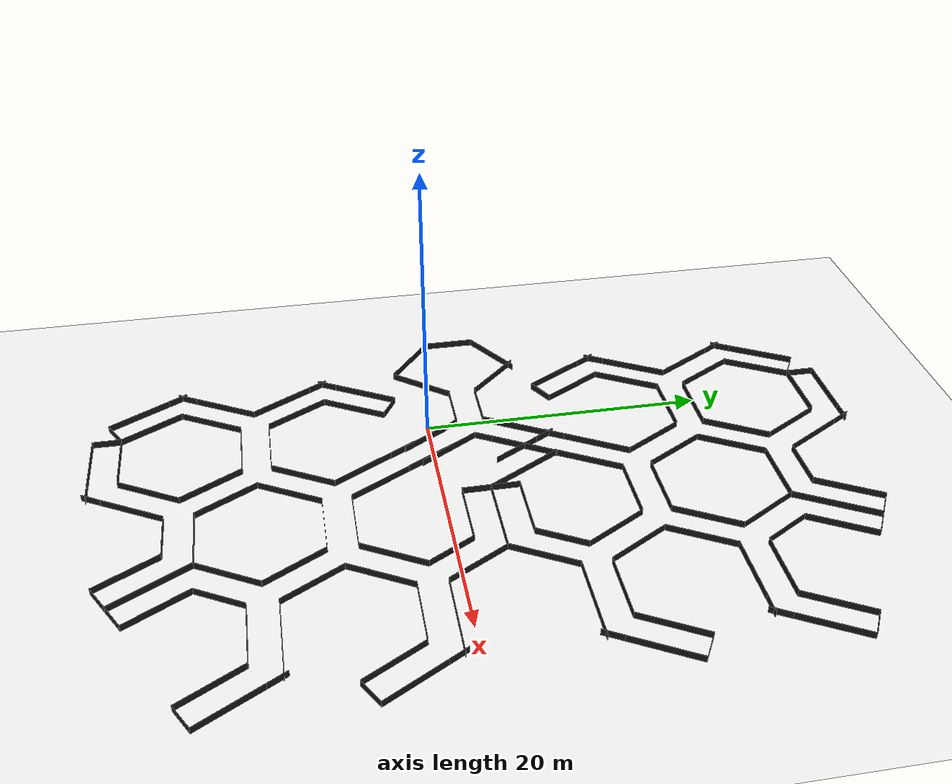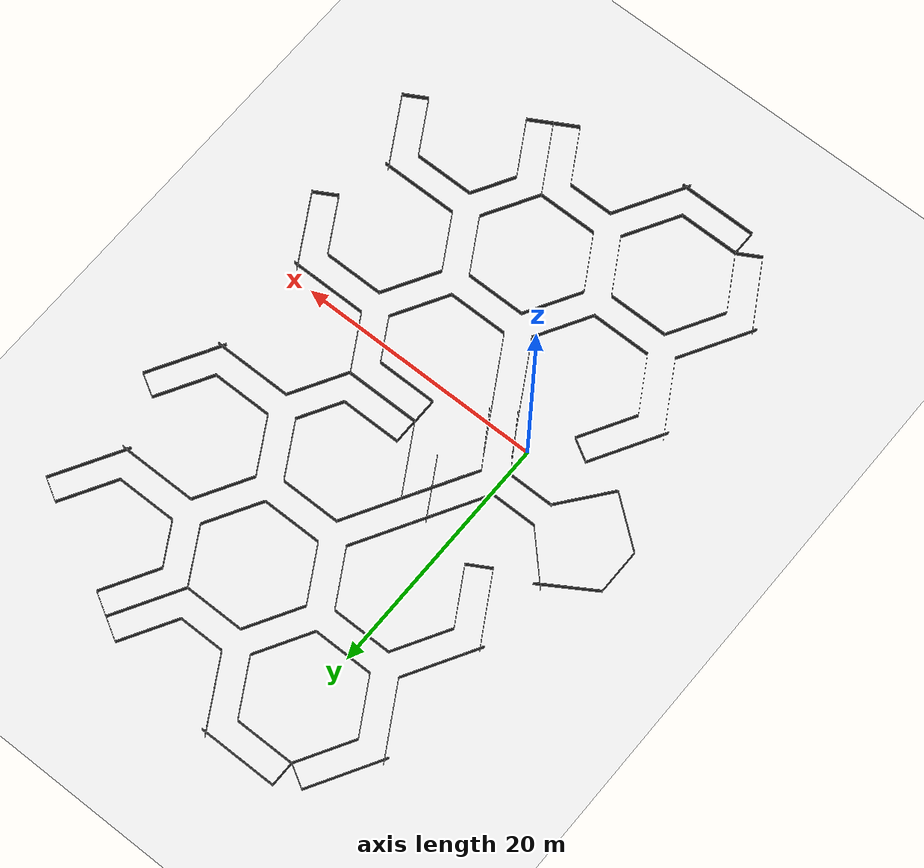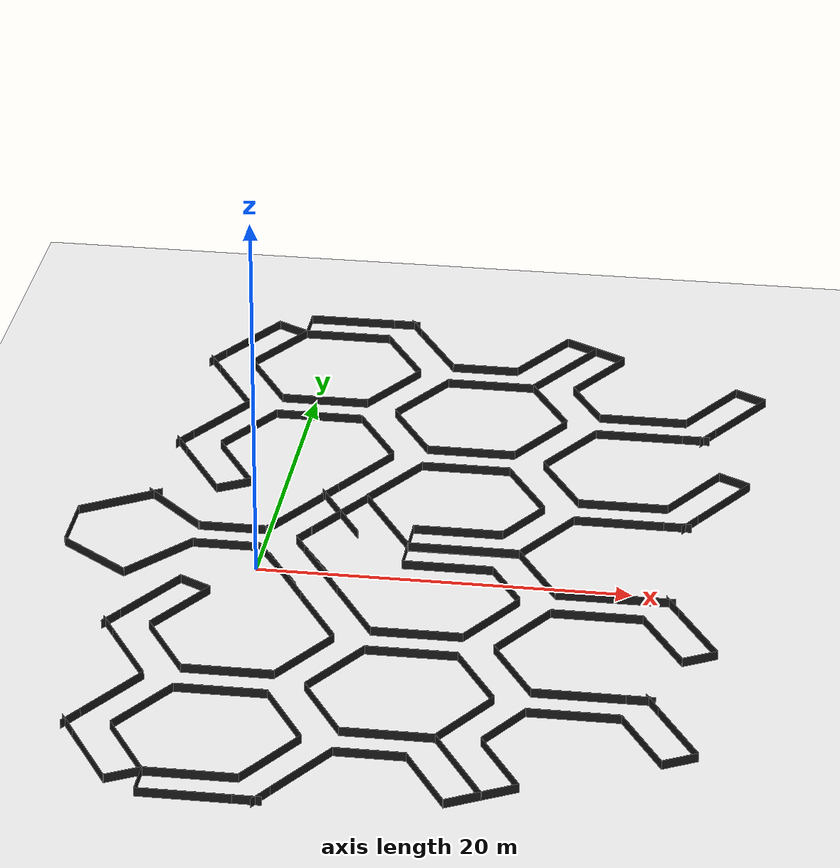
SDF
<sdf version="1.6">
 <world name="default">
  <light name="sun" type="directional">
   <pose>0 0 10 0 -0 0</pose>
   <diffuse>0.8 0.8 0.8 1</diffuse>
   <specular>0.2 0.2 0.2 1</specular>
   <attenuation>
    <range>1000</range>
    <constant>0.9</constant>
    <linear>0.01</linear>
    <quadratic>0.001</quadratic>
   </attenuation>
   <direction>-0.5 0.1 -0.9</direction>
  </light>
  <model name="ground_plane">
   <static>1</static>
   <link name="link">
    <collision name="collision">
     <geometry><plane><normal>0 0 1</normal><size>100 100</size></plane></geometry>
     <surface><friction><ode><mu>100</mu><mu2>50</mu2></ode></friction></surface>
    </collision>
    <visual name="visual">
     <cast_shadows>0</cast_shadows>
     <geometry><plane><normal>0 0 1</normal><size>100 100</size></plane></geometry>
     <material>
      <script><uri>file://media/materials/scripts/gazebo.material</uri><name>Gazebo/White</name></script>
     </material>
    </visual>
   </link>
  </model>
  <gravity>0 0 -9.8</gravity>
  <magnetic_field>6e-06 2.3e-05 -4.2e-05</magnetic_field>
  <atmosphere type="adiabatic"/>
  <physics name="default_physics" default="0" type="ode">
   <max_step_size>0.001</max_step_size>
   <real_time_factor>1</real_time_factor>
   <real_time_update_rate>1000</real_time_update_rate>
  </physics>
  <scene><ambient>0.4 0.4 0.4 1</ambient><background>0.7 0.7 0.7 1</background><shadows>1</shadows></scene>
  <spherical_coordinates>
   <surface_model>EARTH_WGS84</surface_model>
   <latitude_deg>0</latitude_deg>
   <longitude_deg>0</longitude_deg>
   <elevation>0</elevation>
   <heading_deg>0</heading_deg>
  </spherical_coordinates>
  <model name="T_maze_0">
   <link name="link">
    <inertial>
     <mass>1</mass>
     <inertia>
      <ixx>0.166667</ixx>
      <ixy>0</ixy>
      <ixz>0</ixz>
      <iyy>0.166667</iyy>
      <iyz>0</iyz>
      <izz>0.166667</izz>
     </inertia>
    </inertial>
    <pose>8.67982 0.164587 -0 0 -0 0</pose>
    <visual name="ModelPreview_1::link::visual_2">
     <geometry><box><size>0.015 4.8453 0.5</size></box></geometry>
     <material>
      <script><name>Gazebo/FlatBlack</name><uri>file://media/materials/scripts/gazebo.material</uri></script>
      <shader type="pixel"><normal_map>__default__</normal_map></shader>
      <ambient>0.1 0.1 0.1 1</ambient>
      <diffuse>0.1 0.1 0.1 1</diffuse>
      <specular>0.01 0.01 0.01 1</specular>
      <emissive>0 0 0 1</emissive>
     </material>
     <pose>2 0 0 0 -0 0</pose>
    </visual>
    <visual name="visual">
     <geometry><box><size>0.015 4.8453 0.5</size></box></geometry>
     <material>
      <script><name>Gazebo/FlatBlack</name><uri>file://media/materials/scripts/gazebo.material</uri></script>
      <shader type="pixel"><normal_map>__default__</normal_map></shader>
      <ambient>0.1 0.1 0.1 1</ambient>
      <diffuse>0.1 0.1 0.1 1</diffuse>
      <specular>0.01 0.01 0.01 1</specular>
      <emissive>0 0 0 1</emissive>
     </material>
    </visual>
    <collision name="collision_1">
     <pose>2 0 0 0 -0 0</pose>
     <geometry><box><size>0.015 4.8453 0.5</size></box></geometry>
     <surface>
      <friction>
       <ode><mu>1</mu><mu2>1</mu2><fdir1>0 0 0</fdir1><slip1>0</slip1><slip2>0</slip2></ode>
       <torsional>
        <coefficient>1</coefficient>
        <patch_radius>0</patch_radius>
        <surface_radius>0</surface_radius>
        <use_patch_radius>1</use_patch_radius>
        <ode><slip>0</slip></ode>
       </torsional>
      </friction>
      <bounce><restitution_coefficient>0</restitution_coefficient><threshold>1e+06</threshold></bounce>
      <contact>
       <collide_without_contact>0</collide_without_contact>
       <collide_without_contact_bitmask>1</collide_without_contact_bitmask>
       <collide_bitmask>1</collide_bitmask>
       <ode>
        <soft_cfm>0</soft_cfm>
        <soft_erp>0.2</soft_erp>
        <kp>1e+13</kp>
        <kd>1</kd>
        <max_vel>0.01</max_vel>
        <min_depth>0</min_depth>
       </ode>
       <bullet>
        <split_impulse>1</split_impulse>
        <split_impulse_penetration_threshold>-0.01</split_impulse_penetration_threshold>
        <soft_cfm>0</soft_cfm>
        <soft_erp>0.2</soft_erp>
        <kp>1e+13</kp>
        <kd>1</kd>
       </bullet>
      </contact>
     </surface>
    </collision>
    <collision name="collision">
     <geometry><box><size>0.015 4.8453 0.5</size></box></geometry>
     <surface>
      <friction>
       <ode><mu>1</mu><mu2>1</mu2><fdir1>0 0 0</fdir1><slip1>0</slip1><slip2>0</slip2></ode>
       <torsional>
        <coefficient>1</coefficient>
        <patch_radius>0</patch_radius>
        <surface_radius>0</surface_radius>
        <use_patch_radius>1</use_patch_radius>
        <ode><slip>0</slip></ode>
       </torsional>
      </friction>
      <bounce><restitution_coefficient>0</restitution_coefficient><threshold>1e+06</threshold></bounce>
      <contact>
       <collide_without_contact>0</collide_without_contact>
       <collide_without_contact_bitmask>1</collide_without_contact_bitmask>
       <collide_bitmask>1</collide_bitmask>
       <ode>
        <soft_cfm>0</soft_cfm>
        <soft_erp>0.2</soft_erp>
        <kp>1e+13</kp>
        <kd>1</kd>
        <max_vel>0.01</max_vel>
        <min_depth>0</min_depth>
       </ode>
       <bullet>
        <split_impulse>1</split_impulse>
        <split_impulse_penetration_threshold>-0.01</split_impulse_penetration_threshold>
        <soft_cfm>0</soft_cfm>
        <soft_erp>0.2</soft_erp>
        <kp>1e+13</kp>
        <kd>1</kd>
       </bullet>
      </contact>
     </surface>
    </collision>
   </link>
   <link name="link_clone">
    <inertial>
     <mass>1</mass>
     <inertia>
      <ixx>0.166667</ixx>
      <ixy>0</ixy>
      <ixz>0</ixz>
      <iyy>0.166667</iyy>
      <iyz>0</iyz>
      <izz>0.166667</izz>
     </inertia>
    </inertial>
    <pose>12.7749 3.79089 -0 5e-06 -0 2.0944</pose>
    <visual name="visual_2">
     <geometry><box><size>0.015 4.8453 0.5</size></box></geometry>
     <material>
      <script><name>Gazebo/FlatBlack</name><uri>file://media/materials/scripts/gazebo.material</uri></script>
      <shader type="pixel"><normal_map>__default__</normal_map></shader>
      <ambient>0.1 0.1 0.1 1</ambient>
      <diffuse>0.1 0.1 0.1 1</diffuse>
      <specular>0.01 0.01 0.01 1</specular>
      <emissive>0 0 0 1</emissive>
     </material>
     <pose>2 0 0 0 -0 0</pose>
    </visual>
    <visual name="visual">
     <geometry><box><size>0.015 4.8453 0.5</size></box></geometry>
     <material>
      <script><name>Gazebo/FlatBlack</name><uri>file://media/materials/scripts/gazebo.material</uri></script>
      <shader type="pixel"><normal_map>__default__</normal_map></shader>
      <ambient>0.1 0.1 0.1 1</ambient>
      <diffuse>0.1 0.1 0.1 1</diffuse>
      <specular>0.01 0.01 0.01 1</specular>
      <emissive>0 0 0 1</emissive>
     </material>
    </visual>
    <collision name="collision">
     <geometry><box><size>0.015 4.8453 0.5</size></box></geometry>
     <surface>
      <friction>
       <ode><mu>1</mu><mu2>1</mu2><fdir1>0 0 0</fdir1><slip1>0</slip1><slip2>0</slip2></ode>
       <torsional>
        <coefficient>1</coefficient>
        <patch_radius>0</patch_radius>
        <surface_radius>0</surface_radius>
        <use_patch_radius>1</use_patch_radius>
        <ode><slip>0</slip></ode>
       </torsional>
      </friction>
      <bounce><restitution_coefficient>0</restitution_coefficient><threshold>1e+06</threshold></bounce>
      <contact>
       <collide_without_contact>0</collide_without_contact>
       <collide_without_contact_bitmask>1</collide_without_contact_bitmask>
       <collide_bitmask>1</collide_bitmask>
       <ode>
        <soft_cfm>0</soft_cfm>
        <soft_erp>0.2</soft_erp>
        <kp>1e+13</kp>
        <kd>1</kd>
        <max_vel>0.01</max_vel>
        <min_depth>0</min_depth>
       </ode>
       <bullet>
        <split_impulse>1</split_impulse>
        <split_impulse_penetration_threshold>-0.01</split_impulse_penetration_threshold>
        <soft_cfm>0</soft_cfm>
        <soft_erp>0.2</soft_erp>
        <kp>1e+13</kp>
        <kd>1</kd>
       </bullet>
      </contact>
     </surface>
    </collision>
    <collision name="collision_1">
     <pose>2 0 0 0 -0 0</pose>
     <geometry><box><size>0.015 4.8453 0.5</size></box></geometry>
     <surface>
      <friction>
       <ode><mu>1</mu><mu2>1</mu2><fdir1>0 0 0</fdir1><slip1>0</slip1><slip2>0</slip2></ode>
       <torsional>
        <coefficient>1</coefficient>
        <patch_radius>0</patch_radius>
        <surface_radius>0</surface_radius>
        <use_patch_radius>1</use_patch_radius>
        <ode><slip>0</slip></ode>
       </torsional>
      </friction>
      <bounce><restitution_coefficient>0</restitution_coefficient><threshold>1e+06</threshold></bounce>
      <contact>
       <collide_without_contact>0</collide_without_contact>
       <collide_without_contact_bitmask>1</collide_without_contact_bitmask>
       <collide_bitmask>1</collide_bitmask>
       <ode>
        <soft_cfm>0</soft_cfm>
        <soft_erp>0.2</soft_erp>
        <kp>1e+13</kp>
        <kd>1</kd>
        <max_vel>0.01</max_vel>
        <min_depth>0</min_depth>
       </ode>
       <bullet>
        <split_impulse>1</split_impulse>
        <split_impulse_penetration_threshold>-0.01</split_impulse_penetration_threshold>
        <soft_cfm>0</soft_cfm>
        <soft_erp>0.2</soft_erp>
        <kp>1e+13</kp>
        <kd>1</kd>
       </bullet>
      </contact>
     </surface>
    </collision>
   </link>
   <link name="link_clone_0">
    <inertial>
     <mass>1</mass>
     <inertia>
      <ixx>0.166667</ixx>
      <ixy>0</ixy>
      <ixz>0</ixz>
      <iyy>0.166667</iyy>
      <iyz>0</iyz>
      <izz>0.166667</izz>
     </inertia>
    </inertial>
    <pose>7.58433 5.52401 0 5e-06 -0 -2.0944</pose>
    <visual name="visual_2">
     <geometry><box><size>0.015 4.8453 0.5</size></box></geometry>
     <material>
      <script><name>Gazebo/FlatBlack</name><uri>file://media/materials/scripts/gazebo.material</uri></script>
      <shader type="pixel"><normal_map>__default__</normal_map></shader>
      <ambient>0.1 0.1 0.1 1</ambient>
      <diffuse>0.1 0.1 0.1 1</diffuse>
      <specular>0.01 0.01 0.01 1</specular>
      <emissive>0 0 0 1</emissive>
     </material>
     <pose>2 0 0 0 -0 0</pose>
    </visual>
    <visual name="visual">
     <geometry><box><size>0.015 4.8453 0.5</size></box></geometry>
     <material>
      <script><name>Gazebo/FlatBlack</name><uri>file://media/materials/scripts/gazebo.material</uri></script>
      <shader type="pixel"><normal_map>__default__</normal_map></shader>
      <ambient>0.1 0.1 0.1 1</ambient>
      <diffuse>0.1 0.1 0.1 1</diffuse>
      <specular>0.01 0.01 0.01 1</specular>
      <emissive>0 0 0 1</emissive>
     </material>
    </visual>
    <collision name="collision_1">
     <pose>2 0 0 0 -0 0</pose>
     <geometry><box><size>0.015 4.8453 0.5</size></box></geometry>
     <surface>
      <friction>
       <ode><mu>1</mu><mu2>1</mu2><fdir1>0 0 0</fdir1><slip1>0</slip1><slip2>0</slip2></ode>
       <torsional>
        <coefficient>1</coefficient>
        <patch_radius>0</patch_radius>
        <surface_radius>0</surface_radius>
        <use_patch_radius>1</use_patch_radius>
        <ode><slip>0</slip></ode>
       </torsional>
      </friction>
      <bounce><restitution_coefficient>0</restitution_coefficient><threshold>1e+06</threshold></bounce>
      <contact>
       <collide_without_contact>0</collide_without_contact>
       <collide_without_contact_bitmask>1</collide_without_contact_bitmask>
       <collide_bitmask>1</collide_bitmask>
       <ode>
        <soft_cfm>0</soft_cfm>
        <soft_erp>0.2</soft_erp>
        <kp>1e+13</kp>
        <kd>1</kd>
        <max_vel>0.01</max_vel>
        <min_depth>0</min_depth>
       </ode>
       <bullet>
        <split_impulse>1</split_impulse>
        <split_impulse_penetration_threshold>-0.01</split_impulse_penetration_threshold>
        <soft_cfm>0</soft_cfm>
        <soft_erp>0.2</soft_erp>
        <kp>1e+13</kp>
        <kd>1</kd>
       </bullet>
      </contact>
     </surface>
    </collision>
    <collision name="collision">
     <geometry><box><size>0.015 4.8453 0.5</size></box></geometry>
     <surface>
      <friction>
       <ode><mu>1</mu><mu2>1</mu2><fdir1>0 0 0</fdir1><slip1>0</slip1><slip2>0</slip2></ode>
       <torsional>
        <coefficient>1</coefficient>
        <patch_radius>0</patch_radius>
        <surface_radius>0</surface_radius>
        <use_patch_radius>1</use_patch_radius>
        <ode><slip>0</slip></ode>
       </torsional>
      </friction>
      <bounce><restitution_coefficient>0</restitution_coefficient><threshold>1e+06</threshold></bounce>
      <contact>
       <collide_without_contact>0</collide_without_contact>
       <collide_without_contact_bitmask>1</collide_without_contact_bitmask>
       <collide_bitmask>1</collide_bitmask>
       <ode>
        <soft_cfm>0</soft_cfm>
        <soft_erp>0.2</soft_erp>
        <kp>1e+13</kp>
        <kd>1</kd>
        <max_vel>0.01</max_vel>
        <min_depth>0</min_depth>
       </ode>
       <bullet>
        <split_impulse>1</split_impulse>
        <split_impulse_penetration_threshold>-0.01</split_impulse_penetration_threshold>
        <soft_cfm>0</soft_cfm>
        <soft_erp>0.2</soft_erp>
        <kp>1e+13</kp>
        <kd>1</kd>
       </bullet>
      </contact>
     </surface>
    </collision>
   </link>
   <link name="link_clone_0_clone">
    <inertial>
     <mass>1</mass>
     <inertia>
      <ixx>0.166667</ixx>
      <ixy>0</ixy>
      <ixz>0</ixz>
      <iyy>0.166667</iyy>
      <iyz>0</iyz>
      <izz>0.166667</izz>
     </inertia>
    </inertial>
    <pose>12.7746 -3.46264 -0 5e-06 -0 -2.0944</pose>
    <visual name="visual_2">
     <geometry><box><size>0.015 4.8453 0.5</size></box></geometry>
     <material>
      <script><name>Gazebo/FlatBlack</name><uri>file://media/materials/scripts/gazebo.material</uri></script>
      <shader type="pixel"><normal_map>__default__</normal_map></shader>
      <ambient>0.1 0.1 0.1 1</ambient>
      <diffuse>0.1 0.1 0.1 1</diffuse>
      <specular>0.01 0.01 0.01 1</specular>
      <emissive>0 0 0 1</emissive>
     </material>
     <pose>2 0 0 0 -0 0</pose>
    </visual>
    <visual name="visual">
     <geometry><box><size>0.015 4.8453 0.5</size></box></geometry>
     <material>
      <script><name>Gazebo/FlatBlack</name><uri>file://media/materials/scripts/gazebo.material</uri></script>
      <shader type="pixel"><normal_map>__default__</normal_map></shader>
      <ambient>0.1 0.1 0.1 1</ambient>
      <diffuse>0.1 0.1 0.1 1</diffuse>
      <specular>0.01 0.01 0.01 1</specular>
      <emissive>0 0 0 1</emissive>
     </material>
    </visual>
    <collision name="collision_1">
     <pose>2 0 0 0 -0 0</pose>
     <geometry><box><size>0.015 4.8453 0.5</size></box></geometry>
     <surface>
      <friction>
       <ode><mu>1</mu><mu2>1</mu2><fdir1>0 0 0</fdir1><slip1>0</slip1><slip2>0</slip2></ode>
       <torsional>
        <coefficient>1</coefficient>
        <patch_radius>0</patch_radius>
        <surface_radius>0</surface_radius>
        <use_patch_radius>1</use_patch_radius>
        <ode><slip>0</slip></ode>
       </torsional>
      </friction>
      <bounce><restitution_coefficient>0</restitution_coefficient><threshold>1e+06</threshold></bounce>
      <contact>
       <collide_without_contact>0</collide_without_contact>
       <collide_without_contact_bitmask>1</collide_without_contact_bitmask>
       <collide_bitmask>1</collide_bitmask>
       <ode>
        <soft_cfm>0</soft_cfm>
        <soft_erp>0.2</soft_erp>
        <kp>1e+13</kp>
        <kd>1</kd>
        <max_vel>0.01</max_vel>
        <min_depth>0</min_depth>
       </ode>
       <bullet>
        <split_impulse>1</split_impulse>
        <split_impulse_penetration_threshold>-0.01</split_impulse_penetration_threshold>
        <soft_cfm>0</soft_cfm>
        <soft_erp>0.2</soft_erp>
        <kp>1e+13</kp>
        <kd>1</kd>
       </bullet>
      </contact>
     </surface>
    </collision>
    <collision name="collision">
     <geometry><box><size>0.015 4.8453 0.5</size></box></geometry>
     <surface>
      <friction>
       <ode><mu>1</mu><mu2>1</mu2><fdir1>0 0 0</fdir1><slip1>0</slip1><slip2>0</slip2></ode>
       <torsional>
        <coefficient>1</coefficient>
        <patch_radius>0</patch_radius>
        <surface_radius>0</surface_radius>
        <use_patch_radius>1</use_patch_radius>
        <ode><slip>0</slip></ode>
       </torsional>
      </friction>
      <bounce><restitution_coefficient>0</restitution_coefficient><threshold>1e+06</threshold></bounce>
      <contact>
       <collide_without_contact>0</collide_without_contact>
       <collide_without_contact_bitmask>1</collide_without_contact_bitmask>
       <collide_bitmask>1</collide_bitmask>
       <ode>
        <soft_cfm>0</soft_cfm>
        <soft_erp>0.2</soft_erp>
        <kp>1e+13</kp>
        <kd>1</kd>
        <max_vel>0.01</max_vel>
        <min_depth>0</min_depth>
       </ode>
       <bullet>
        <split_impulse>1</split_impulse>
        <split_impulse_penetration_threshold>-0.01</split_impulse_penetration_threshold>
        <soft_cfm>0</soft_cfm>
        <soft_erp>0.2</soft_erp>
        <kp>1e+13</kp>
        <kd>1</kd>
       </bullet>
      </contact>
     </surface>
    </collision>
   </link>
   <link name="link_clone_0_clone_clone">
    <inertial>
     <mass>1</mass>
     <inertia>
      <ixx>0.166667</ixx>
      <ixy>0</ixy>
      <ixz>0</ixz>
      <iyy>0.166667</iyy>
      <iyz>0</iyz>
      <izz>0.166667</izz>
     </inertia>
    </inertial>
    <pose>17.958 -12.4374 -0 5e-06 -0 -2.0944</pose>
    <visual name="visual">
     <geometry><box><size>0.015 4.8453 0.5</size></box></geometry>
     <material>
      <script><name>Gazebo/FlatBlack</name><uri>file://media/materials/scripts/gazebo.material</uri></script>
      <shader type="pixel"><normal_map>__default__</normal_map></shader>
      <ambient>0.1 0.1 0.1 1</ambient>
      <diffuse>0.1 0.1 0.1 1</diffuse>
      <specular>0.01 0.01 0.01 1</specular>
      <emissive>0 0 0 1</emissive>
     </material>
    </visual>
    <visual name="visual_2">
     <geometry><box><size>0.015 4.8453 0.5</size></box></geometry>
     <material>
      <script><name>Gazebo/FlatBlack</name><uri>file://media/materials/scripts/gazebo.material</uri></script>
      <shader type="pixel"><normal_map>__default__</normal_map></shader>
      <ambient>0.1 0.1 0.1 1</ambient>
      <diffuse>0.1 0.1 0.1 1</diffuse>
      <specular>0.01 0.01 0.01 1</specular>
      <emissive>0 0 0 1</emissive>
     </material>
     <pose>2 0 0 0 -0 0</pose>
    </visual>
    <collision name="collision_1">
     <pose>2 0 0 0 -0 0</pose>
     <geometry><box><size>0.015 4.8453 0.5</size></box></geometry>
     <surface>
      <friction>
       <ode><mu>1</mu><mu2>1</mu2><fdir1>0 0 0</fdir1><slip1>0</slip1><slip2>0</slip2></ode>
       <torsional>
        <coefficient>1</coefficient>
        <patch_radius>0</patch_radius>
        <surface_radius>0</surface_radius>
        <use_patch_radius>1</use_patch_radius>
        <ode><slip>0</slip></ode>
       </torsional>
      </friction>
      <bounce><restitution_coefficient>0</restitution_coefficient><threshold>1e+06</threshold></bounce>
      <contact>
       <collide_without_contact>0</collide_without_contact>
       <collide_without_contact_bitmask>1</collide_without_contact_bitmask>
       <collide_bitmask>1</collide_bitmask>
       <ode>
        <soft_cfm>0</soft_cfm>
        <soft_erp>0.2</soft_erp>
        <kp>1e+13</kp>
        <kd>1</kd>
        <max_vel>0.01</max_vel>
        <min_depth>0</min_depth>
       </ode>
       <bullet>
        <split_impulse>1</split_impulse>
        <split_impulse_penetration_threshold>-0.01</split_impulse_penetration_threshold>
        <soft_cfm>0</soft_cfm>
        <soft_erp>0.2</soft_erp>
        <kp>1e+13</kp>
        <kd>1</kd>
       </bullet>
      </contact>
     </surface>
    </collision>
    <collision name="collision">
     <geometry><box><size>0.015 4.8453 0.5</size></box></geometry>
     <surface>
      <friction>
       <ode><mu>1</mu><mu2>1</mu2><fdir1>0 0 0</fdir1><slip1>0</slip1><slip2>0</slip2></ode>
       <torsional>
        <coefficient>1</coefficient>
        <patch_radius>0</patch_radius>
        <surface_radius>0</surface_radius>
        <use_patch_radius>1</use_patch_radius>
        <ode><slip>0</slip></ode>
       </torsional>
      </friction>
      <bounce><restitution_coefficient>0</restitution_coefficient><threshold>1e+06</threshold></bounce>
      <contact>
       <collide_without_contact>0</collide_without_contact>
       <collide_without_contact_bitmask>1</collide_without_contact_bitmask>
       <collide_bitmask>1</collide_bitmask>
       <ode>
        <soft_cfm>0</soft_cfm>
        <soft_erp>0.2</soft_erp>
        <kp>1e+13</kp>
        <kd>1</kd>
        <max_vel>0.01</max_vel>
        <min_depth>0</min_depth>
       </ode>
       <bullet>
        <split_impulse>1</split_impulse>
        <split_impulse_penetration_threshold>-0.01</split_impulse_penetration_threshold>
        <soft_cfm>0</soft_cfm>
        <soft_erp>0.2</soft_erp>
        <kp>1e+13</kp>
        <kd>1</kd>
       </bullet>
      </contact>
     </surface>
    </collision>
   </link>
   <link name="link_clone_0_clone_clone_0">
    <inertial>
     <mass>1</mass>
     <inertia>
      <ixx>0.166667</ixx>
      <ixy>0</ixy>
      <ixz>0</ixz>
      <iyy>0.166667</iyy>
      <iyz>0</iyz>
      <izz>0.166667</izz>
     </inertia>
    </inertial>
    <pose>7.58617 -12.4482 -0 5e-06 -0 -2.0944</pose>
    <visual name="visual_2">
     <geometry><box><size>0.015 4.8453 0.5</size></box></geometry>
     <material>
      <script><name>Gazebo/FlatBlack</name><uri>file://media/materials/scripts/gazebo.material</uri></script>
      <shader type="pixel"><normal_map>__default__</normal_map></shader>
      <ambient>0.1 0.1 0.1 1</ambient>
      <diffuse>0.1 0.1 0.1 1</diffuse>
      <specular>0.01 0.01 0.01 1</specular>
      <emissive>0 0 0 1</emissive>
     </material>
     <pose>2 0 0 0 -0 0</pose>
    </visual>
    <visual name="visual">
     <geometry><box><size>0.015 4.8453 0.5</size></box></geometry>
     <material>
      <script><name>Gazebo/FlatBlack</name><uri>file://media/materials/scripts/gazebo.material</uri></script>
      <shader type="pixel"><normal_map>__default__</normal_map></shader>
      <ambient>0.1 0.1 0.1 1</ambient>
      <diffuse>0.1 0.1 0.1 1</diffuse>
      <specular>0.01 0.01 0.01 1</specular>
      <emissive>0 0 0 1</emissive>
     </material>
    </visual>
    <collision name="collision">
     <geometry><box><size>0.015 4.8453 0.5</size></box></geometry>
     <surface>
      <friction>
       <ode><mu>1</mu><mu2>1</mu2><fdir1>0 0 0</fdir1><slip1>0</slip1><slip2>0</slip2></ode>
       <torsional>
        <coefficient>1</coefficient>
        <patch_radius>0</patch_radius>
        <surface_radius>0</surface_radius>
        <use_patch_radius>1</use_patch_radius>
        <ode><slip>0</slip></ode>
       </torsional>
      </friction>
      <bounce><restitution_coefficient>0</restitution_coefficient><threshold>1e+06</threshold></bounce>
      <contact>
       <collide_without_contact>0</collide_without_contact>
       <collide_without_contact_bitmask>1</collide_without_contact_bitmask>
       <collide_bitmask>1</collide_bitmask>
       <ode>
        <soft_cfm>0</soft_cfm>
        <soft_erp>0.2</soft_erp>
        <kp>1e+13</kp>
        <kd>1</kd>
        <max_vel>0.01</max_vel>
        <min_depth>0</min_depth>
       </ode>
       <bullet>
        <split_impulse>1</split_impulse>
        <split_impulse_penetration_threshold>-0.01</split_impulse_penetration_threshold>
        <soft_cfm>0</soft_cfm>
        <soft_erp>0.2</soft_erp>
        <kp>1e+13</kp>
        <kd>1</kd>
       </bullet>
      </contact>
     </surface>
    </collision>
    <collision name="collision_1">
     <pose>2 0 0 0 -0 0</pose>
     <geometry><box><size>0.015 4.8453 0.5</size></box></geometry>
     <surface>
      <friction>
       <ode><mu>1</mu><mu2>1</mu2><fdir1>0 0 0</fdir1><slip1>0</slip1><slip2>0</slip2></ode>
       <torsional>
        <coefficient>1</coefficient>
        <patch_radius>0</patch_radius>
        <surface_radius>0</surface_radius>
        <use_patch_radius>1</use_patch_radius>
        <ode><slip>0</slip></ode>
       </torsional>
      </friction>
      <bounce><restitution_coefficient>0</restitution_coefficient><threshold>1e+06</threshold></bounce>
      <contact>
       <collide_without_contact>0</collide_without_contact>
       <collide_without_contact_bitmask>1</collide_without_contact_bitmask>
       <collide_bitmask>1</collide_bitmask>
       <ode>
        <soft_cfm>0</soft_cfm>
        <soft_erp>0.2</soft_erp>
        <kp>1e+13</kp>
        <kd>1</kd>
        <max_vel>0.01</max_vel>
        <min_depth>0</min_depth>
       </ode>
       <bullet>
        <split_impulse>1</split_impulse>
        <split_impulse_penetration_threshold>-0.01</split_impulse_penetration_threshold>
        <soft_cfm>0</soft_cfm>
        <soft_erp>0.2</soft_erp>
        <kp>1e+13</kp>
        <kd>1</kd>
       </bullet>
      </contact>
     </surface>
    </collision>
   </link>
   <link name="link_clone_0_clone_clone_1">
    <inertial>
     <mass>1</mass>
     <inertia>
      <ixx>0.166667</ixx>
      <ixy>0</ixy>
      <ixz>0</ixz>
      <iyy>0.166667</iyy>
      <iyz>0</iyz>
      <izz>0.166667</izz>
     </inertia>
    </inertial>
    <pose>17.9599 5.5227 1e-06 5e-06 -0 -2.0944</pose>
    <visual name="visual_2">
     <geometry><box><size>0.015 4.8453 0.5</size></box></geometry>
     <material>
      <script><name>Gazebo/FlatBlack</name><uri>file://media/materials/scripts/gazebo.material</uri></script>
      <shader type="pixel"><normal_map>__default__</normal_map></shader>
      <ambient>0.1 0.1 0.1 1</ambient>
      <diffuse>0.1 0.1 0.1 1</diffuse>
      <specular>0.01 0.01 0.01 1</specular>
      <emissive>0 0 0 1</emissive>
     </material>
     <pose>2 0 0 0 -0 0</pose>
    </visual>
    <visual name="visual">
     <geometry><box><size>0.015 3.7053 0.5</size></box></geometry>
     <material>
      <script><name>Gazebo/FlatBlack</name><uri>file://media/materials/scripts/gazebo.material</uri></script>
      <shader type="pixel"><normal_map>__default__</normal_map></shader>
      <ambient>0.1 0.1 0.1 1</ambient>
      <diffuse>0.1 0.1 0.1 1</diffuse>
      <specular>0.01 0.01 0.01 1</specular>
      <emissive>0 0 0 1</emissive>
     </material>
     <pose>0 -0.57 0 0 -0 0</pose>
    </visual>
    <collision name="collision_1">
     <pose>2 0 0 0 -0 0</pose>
     <geometry><box><size>0.015 4.8453 0.5</size></box></geometry>
     <surface>
      <friction>
       <ode><mu>1</mu><mu2>1</mu2><fdir1>0 0 0</fdir1><slip1>0</slip1><slip2>0</slip2></ode>
       <torsional>
        <coefficient>1</coefficient>
        <patch_radius>0</patch_radius>
        <surface_radius>0</surface_radius>
        <use_patch_radius>1</use_patch_radius>
        <ode><slip>0</slip></ode>
       </torsional>
      </friction>
      <bounce><restitution_coefficient>0</restitution_coefficient><threshold>1e+06</threshold></bounce>
      <contact>
       <collide_without_contact>0</collide_without_contact>
       <collide_without_contact_bitmask>1</collide_without_contact_bitmask>
       <collide_bitmask>1</collide_bitmask>
       <ode>
        <soft_cfm>0</soft_cfm>
        <soft_erp>0.2</soft_erp>
        <kp>1e+13</kp>
        <kd>1</kd>
        <max_vel>0.01</max_vel>
        <min_depth>0</min_depth>
       </ode>
       <bullet>
        <split_impulse>1</split_impulse>
        <split_impulse_penetration_threshold>-0.01</split_impulse_penetration_threshold>
        <soft_cfm>0</soft_cfm>
        <soft_erp>0.2</soft_erp>
        <kp>1e+13</kp>
        <kd>1</kd>
       </bullet>
      </contact>
     </surface>
    </collision>
    <collision name="collision">
     <pose>0 -0.57 0 0 -0 0</pose>
     <geometry><box><size>0.015 3.7053 0.5</size></box></geometry>
     <surface>
      <friction>
       <ode><mu>1</mu><mu2>1</mu2><fdir1>0 0 0</fdir1><slip1>0</slip1><slip2>0</slip2></ode>
       <torsional>
        <coefficient>1</coefficient>
        <patch_radius>0</patch_radius>
        <surface_radius>0</surface_radius>
        <use_patch_radius>1</use_patch_radius>
        <ode><slip>0</slip></ode>
       </torsional>
      </friction>
      <bounce><restitution_coefficient>0</restitution_coefficient><threshold>1e+06</threshold></bounce>
      <contact>
       <collide_without_contact>0</collide_without_contact>
       <collide_without_contact_bitmask>1</collide_without_contact_bitmask>
       <collide_bitmask>1</collide_bitmask>
       <ode>
        <soft_cfm>0</soft_cfm>
        <soft_erp>0.2</soft_erp>
        <kp>1e+13</kp>
        <kd>1</kd>
        <max_vel>0.01</max_vel>
        <min_depth>0</min_depth>
       </ode>
       <bullet>
        <split_impulse>1</split_impulse>
        <split_impulse_penetration_threshold>-0.01</split_impulse_penetration_threshold>
        <soft_cfm>0</soft_cfm>
        <soft_erp>0.2</soft_erp>
        <kp>1e+13</kp>
        <kd>1</kd>
       </bullet>
      </contact>
     </surface>
    </collision>
   </link>
   <link name="link_clone_0_clone_clone_1_clone">
    <inertial>
     <mass>1</mass>
     <inertia>
      <ixx>0.166667</ixx>
      <ixy>0</ixy>
      <ixz>0</ixz>
      <iyy>0.166667</iyy>
      <iyz>0</iyz>
      <izz>0.166667</izz>
     </inertia>
    </inertial>
    <pose>19.0569 0.16687 -6e-06 5e-06 -0 0</pose>
    <visual name="visual_2">
     <geometry><box><size>0.015 3.7053 0.5</size></box></geometry>
     <material>
      <script><name>Gazebo/FlatBlack</name><uri>file://media/materials/scripts/gazebo.material</uri></script>
      <shader type="pixel"><normal_map>__default__</normal_map></shader>
      <ambient>0.1 0.1 0.1 1</ambient>
      <diffuse>0.1 0.1 0.1 1</diffuse>
      <specular>0.01 0.01 0.01 1</specular>
      <emissive>0 0 0 1</emissive>
     </material>
     <pose>2 -0.57 0 0 -0 0</pose>
    </visual>
    <visual name="visual">
     <geometry><box><size>0.015 4.8453 0.5</size></box></geometry>
     <material>
      <script><name>Gazebo/FlatBlack</name><uri>file://media/materials/scripts/gazebo.material</uri></script>
      <shader type="pixel"><normal_map>__default__</normal_map></shader>
      <ambient>0.1 0.1 0.1 1</ambient>
      <diffuse>0.1 0.1 0.1 1</diffuse>
      <specular>0.01 0.01 0.01 1</specular>
      <emissive>0 0 0 1</emissive>
     </material>
    </visual>
    <collision name="collision_1">
     <pose>2 -0.57 0 0 -0 0</pose>
     <geometry><box><size>0.015 3.7053 0.5</size></box></geometry>
     <surface>
      <friction>
       <ode><mu>1</mu><mu2>1</mu2><fdir1>0 0 0</fdir1><slip1>0</slip1><slip2>0</slip2></ode>
       <torsional>
        <coefficient>1</coefficient>
        <patch_radius>0</patch_radius>
        <surface_radius>0</surface_radius>
        <use_patch_radius>1</use_patch_radius>
        <ode><slip>0</slip></ode>
       </torsional>
      </friction>
      <bounce><restitution_coefficient>0</restitution_coefficient><threshold>1e+06</threshold></bounce>
      <contact>
       <collide_without_contact>0</collide_without_contact>
       <collide_without_contact_bitmask>1</collide_without_contact_bitmask>
       <collide_bitmask>1</collide_bitmask>
       <ode>
        <soft_cfm>0</soft_cfm>
        <soft_erp>0.2</soft_erp>
        <kp>1e+13</kp>
        <kd>1</kd>
        <max_vel>0.01</max_vel>
        <min_depth>0</min_depth>
       </ode>
       <bullet>
        <split_impulse>1</split_impulse>
        <split_impulse_penetration_threshold>-0.01</split_impulse_penetration_threshold>
        <soft_cfm>0</soft_cfm>
        <soft_erp>0.2</soft_erp>
        <kp>1e+13</kp>
        <kd>1</kd>
       </bullet>
      </contact>
     </surface>
    </collision>
    <collision name="collision">
     <geometry><box><size>0.015 4.8453 0.5</size></box></geometry>
     <surface>
      <friction>
       <ode><mu>1</mu><mu2>1</mu2><fdir1>0 0 0</fdir1><slip1>0</slip1><slip2>0</slip2></ode>
       <torsional>
        <coefficient>1</coefficient>
        <patch_radius>0</patch_radius>
        <surface_radius>0</surface_radius>
        <use_patch_radius>1</use_patch_radius>
        <ode><slip>0</slip></ode>
       </torsional>
      </friction>
      <bounce><restitution_coefficient>0</restitution_coefficient><threshold>1e+06</threshold></bounce>
      <contact>
       <collide_without_contact>0</collide_without_contact>
       <collide_without_contact_bitmask>1</collide_without_contact_bitmask>
       <collide_bitmask>1</collide_bitmask>
       <ode>
        <soft_cfm>0</soft_cfm>
        <soft_erp>0.2</soft_erp>
        <kp>1e+13</kp>
        <kd>1</kd>
        <max_vel>0.01</max_vel>
        <min_depth>0</min_depth>
       </ode>
       <bullet>
        <split_impulse>1</split_impulse>
        <split_impulse_penetration_threshold>-0.01</split_impulse_penetration_threshold>
        <soft_cfm>0</soft_cfm>
        <soft_erp>0.2</soft_erp>
        <kp>1e+13</kp>
        <kd>1</kd>
       </bullet>
      </contact>
     </surface>
    </collision>
   </link>
   <link name="link_clone_0_clone_clone_1_clone_0">
    <inertial>
     <mass>1</mass>
     <inertia>
      <ixx>0.166667</ixx>
      <ixy>0</ixy>
      <ixz>0</ixz>
      <iyy>0.166667</iyy>
      <iyz>0</iyz>
      <izz>0.166667</izz>
     </inertia>
    </inertial>
    <pose>2.39592 3.79036 1e-06 5e-06 -0 2.0944</pose>
    <visual name="visual">
     <geometry><box><size>0.015 3.7053 0.5</size></box></geometry>
     <material>
      <script><name>Gazebo/FlatBlack</name><uri>file://media/materials/scripts/gazebo.material</uri></script>
      <shader type="pixel"><normal_map>__default__</normal_map></shader>
      <ambient>0.1 0.1 0.1 1</ambient>
      <diffuse>0.1 0.1 0.1 1</diffuse>
      <specular>0.01 0.01 0.01 1</specular>
      <emissive>0 0 0 1</emissive>
     </material>
     <pose>0 -0.57 0 0 -0 0</pose>
    </visual>
    <visual name="visual_2">
     <geometry><box><size>0.015 4.8453 0.5</size></box></geometry>
     <material>
      <script><name>Gazebo/FlatBlack</name><uri>file://media/materials/scripts/gazebo.material</uri></script>
      <shader type="pixel"><normal_map>__default__</normal_map></shader>
      <ambient>0.1 0.1 0.1 1</ambient>
      <diffuse>0.1 0.1 0.1 1</diffuse>
      <specular>0.01 0.01 0.01 1</specular>
      <emissive>0 0 0 1</emissive>
     </material>
     <pose>2 0 0 0 -0 0</pose>
    </visual>
    <collision name="collision_1">
     <pose>2 0 0 0 -0 0</pose>
     <geometry><box><size>0.015 4.8453 0.5</size></box></geometry>
     <surface>
      <friction>
       <ode><mu>1</mu><mu2>1</mu2><fdir1>0 0 0</fdir1><slip1>0</slip1><slip2>0</slip2></ode>
       <torsional>
        <coefficient>1</coefficient>
        <patch_radius>0</patch_radius>
        <surface_radius>0</surface_radius>
        <use_patch_radius>1</use_patch_radius>
        <ode><slip>0</slip></ode>
       </torsional>
      </friction>
      <bounce><restitution_coefficient>0</restitution_coefficient><threshold>1e+06</threshold></bounce>
      <contact>
       <collide_without_contact>0</collide_without_contact>
       <collide_without_contact_bitmask>1</collide_without_contact_bitmask>
       <collide_bitmask>1</collide_bitmask>
       <ode>
        <soft_cfm>0</soft_cfm>
        <soft_erp>0.2</soft_erp>
        <kp>1e+13</kp>
        <kd>1</kd>
        <max_vel>0.01</max_vel>
        <min_depth>0</min_depth>
       </ode>
       <bullet>
        <split_impulse>1</split_impulse>
        <split_impulse_penetration_threshold>-0.01</split_impulse_penetration_threshold>
        <soft_cfm>0</soft_cfm>
        <soft_erp>0.2</soft_erp>
        <kp>1e+13</kp>
        <kd>1</kd>
       </bullet>
      </contact>
     </surface>
    </collision>
    <collision name="collision">
     <pose>0 -0.57 0 0 -0 0</pose>
     <geometry><box><size>0.015 3.7053 0.5</size></box></geometry>
     <surface>
      <friction>
       <ode><mu>1</mu><mu2>1</mu2><fdir1>0 0 0</fdir1><slip1>0</slip1><slip2>0</slip2></ode>
       <torsional>
        <coefficient>1</coefficient>
        <patch_radius>0</patch_radius>
        <surface_radius>0</surface_radius>
        <use_patch_radius>1</use_patch_radius>
        <ode><slip>0</slip></ode>
       </torsional>
      </friction>
      <bounce><restitution_coefficient>0</restitution_coefficient><threshold>1e+06</threshold></bounce>
      <contact>
       <collide_without_contact>0</collide_without_contact>
       <collide_without_contact_bitmask>1</collide_without_contact_bitmask>
       <collide_bitmask>1</collide_bitmask>
       <ode>
        <soft_cfm>0</soft_cfm>
        <soft_erp>0.2</soft_erp>
        <kp>1e+13</kp>
        <kd>1</kd>
        <max_vel>0.01</max_vel>
        <min_depth>0</min_depth>
       </ode>
       <bullet>
        <split_impulse>1</split_impulse>
        <split_impulse_penetration_threshold>-0.01</split_impulse_penetration_threshold>
        <soft_cfm>0</soft_cfm>
        <soft_erp>0.2</soft_erp>
        <kp>1e+13</kp>
        <kd>1</kd>
       </bullet>
      </contact>
     </surface>
    </collision>
   </link>
   <link name="link_clone_0_clone_clone_clone">
    <inertial>
     <mass>1</mass>
     <inertia>
      <ixx>0.166667</ixx>
      <ixy>0</ixy>
      <ixz>0</ixz>
      <iyy>0.166667</iyy>
      <iyz>0</iyz>
      <izz>0.166667</izz>
     </inertia>
    </inertial>
    <pose>23.1519 -3.46238 -0 5e-06 -0 -2.0944</pose>
    <visual name="visual">
     <geometry><box><size>0.015 4.8453 0.5</size></box></geometry>
     <material>
      <script><name>Gazebo/FlatBlack</name><uri>file://media/materials/scripts/gazebo.material</uri></script>
      <shader type="pixel"><normal_map>__default__</normal_map></shader>
      <ambient>0.1 0.1 0.1 1</ambient>
      <diffuse>0.1 0.1 0.1 1</diffuse>
      <specular>0.01 0.01 0.01 1</specular>
      <emissive>0 0 0 1</emissive>
     </material>
    </visual>
    <visual name="visual_2">
     <geometry><box><size>0.015 4.8453 0.5</size></box></geometry>
     <material>
      <script><name>Gazebo/FlatBlack</name><uri>file://media/materials/scripts/gazebo.material</uri></script>
      <shader type="pixel"><normal_map>__default__</normal_map></shader>
      <ambient>0.1 0.1 0.1 1</ambient>
      <diffuse>0.1 0.1 0.1 1</diffuse>
      <specular>0.01 0.01 0.01 1</specular>
      <emissive>0 0 0 1</emissive>
     </material>
     <pose>2 0 0 0 -0 0</pose>
    </visual>
    <collision name="collision_1">
     <pose>2 0 0 0 -0 0</pose>
     <geometry><box><size>0.015 4.8453 0.5</size></box></geometry>
     <surface>
      <friction>
       <ode><mu>1</mu><mu2>1</mu2><fdir1>0 0 0</fdir1><slip1>0</slip1><slip2>0</slip2></ode>
       <torsional>
        <coefficient>1</coefficient>
        <patch_radius>0</patch_radius>
        <surface_radius>0</surface_radius>
        <use_patch_radius>1</use_patch_radius>
        <ode><slip>0</slip></ode>
       </torsional>
      </friction>
      <bounce><restitution_coefficient>0</restitution_coefficient><threshold>1e+06</threshold></bounce>
      <contact>
       <collide_without_contact>0</collide_without_contact>
       <collide_without_contact_bitmask>1</collide_without_contact_bitmask>
       <collide_bitmask>1</collide_bitmask>
       <ode>
        <soft_cfm>0</soft_cfm>
        <soft_erp>0.2</soft_erp>
        <kp>1e+13</kp>
        <kd>1</kd>
        <max_vel>0.01</max_vel>
        <min_depth>0</min_depth>
       </ode>
       <bullet>
        <split_impulse>1</split_impulse>
        <split_impulse_penetration_threshold>-0.01</split_impulse_penetration_threshold>
        <soft_cfm>0</soft_cfm>
        <soft_erp>0.2</soft_erp>
        <kp>1e+13</kp>
        <kd>1</kd>
       </bullet>
      </contact>
     </surface>
    </collision>
    <collision name="collision">
     <geometry><box><size>0.015 4.8453 0.5</size></box></geometry>
     <surface>
      <friction>
       <ode><mu>1</mu><mu2>1</mu2><fdir1>0 0 0</fdir1><slip1>0</slip1><slip2>0</slip2></ode>
       <torsional>
        <coefficient>1</coefficient>
        <patch_radius>0</patch_radius>
        <surface_radius>0</surface_radius>
        <use_patch_radius>1</use_patch_radius>
        <ode><slip>0</slip></ode>
       </torsional>
      </friction>
      <bounce><restitution_coefficient>0</restitution_coefficient><threshold>1e+06</threshold></bounce>
      <contact>
       <collide_without_contact>0</collide_without_contact>
       <collide_without_contact_bitmask>1</collide_without_contact_bitmask>
       <collide_bitmask>1</collide_bitmask>
       <ode>
        <soft_cfm>0</soft_cfm>
        <soft_erp>0.2</soft_erp>
        <kp>1e+13</kp>
        <kd>1</kd>
        <max_vel>0.01</max_vel>
        <min_depth>0</min_depth>
       </ode>
       <bullet>
        <split_impulse>1</split_impulse>
        <split_impulse_penetration_threshold>-0.01</split_impulse_penetration_threshold>
        <soft_cfm>0</soft_cfm>
        <soft_erp>0.2</soft_erp>
        <kp>1e+13</kp>
        <kd>1</kd>
       </bullet>
      </contact>
     </surface>
    </collision>
   </link>
   <link name="link_clone_1">
    <inertial>
     <mass>1</mass>
     <inertia>
      <ixx>0.166667</ixx>
      <ixy>0</ixy>
      <ixz>0</ixz>
      <iyy>0.166667</iyy>
      <iyz>0</iyz>
      <izz>0.166667</izz>
     </inertia>
    </inertial>
    <pose>13.8686 9.15 0 0 -0 0</pose>
    <visual name="visual_2">
     <geometry><box><size>0.015 4.8453 0.5</size></box></geometry>
     <material>
      <script><name>Gazebo/FlatBlack</name><uri>file://media/materials/scripts/gazebo.material</uri></script>
      <shader type="pixel"><normal_map>__default__</normal_map></shader>
      <ambient>0.1 0.1 0.1 1</ambient>
      <diffuse>0.1 0.1 0.1 1</diffuse>
      <specular>0.01 0.01 0.01 1</specular>
      <emissive>0 0 0 1</emissive>
     </material>
     <pose>2 0 0 0 -0 0</pose>
    </visual>
    <visual name="visual">
     <geometry><box><size>0.015 4.8453 0.5</size></box></geometry>
     <material>
      <script><name>Gazebo/FlatBlack</name><uri>file://media/materials/scripts/gazebo.material</uri></script>
      <shader type="pixel"><normal_map>__default__</normal_map></shader>
      <ambient>0.1 0.1 0.1 1</ambient>
      <diffuse>0.1 0.1 0.1 1</diffuse>
      <specular>0.01 0.01 0.01 1</specular>
      <emissive>0 0 0 1</emissive>
     </material>
    </visual>
    <collision name="collision_1">
     <pose>2 0 0 0 -0 0</pose>
     <geometry><box><size>0.015 4.8453 0.5</size></box></geometry>
     <surface>
      <friction>
       <ode><mu>1</mu><mu2>1</mu2><fdir1>0 0 0</fdir1><slip1>0</slip1><slip2>0</slip2></ode>
       <torsional>
        <coefficient>1</coefficient>
        <patch_radius>0</patch_radius>
        <surface_radius>0</surface_radius>
        <use_patch_radius>1</use_patch_radius>
        <ode><slip>0</slip></ode>
       </torsional>
      </friction>
      <bounce><restitution_coefficient>0</restitution_coefficient><threshold>1e+06</threshold></bounce>
      <contact>
       <collide_without_contact>0</collide_without_contact>
       <collide_without_contact_bitmask>1</collide_without_contact_bitmask>
       <collide_bitmask>1</collide_bitmask>
       <ode>
        <soft_cfm>0</soft_cfm>
        <soft_erp>0.2</soft_erp>
        <kp>1e+13</kp>
        <kd>1</kd>
        <max_vel>0.01</max_vel>
        <min_depth>0</min_depth>
       </ode>
       <bullet>
        <split_impulse>1</split_impulse>
        <split_impulse_penetration_threshold>-0.01</split_impulse_penetration_threshold>
        <soft_cfm>0</soft_cfm>
        <soft_erp>0.2</soft_erp>
        <kp>1e+13</kp>
        <kd>1</kd>
       </bullet>
      </contact>
     </surface>
    </collision>
    <collision name="collision">
     <geometry><box><size>0.015 4.8453 0.5</size></box></geometry>
     <surface>
      <friction>
       <ode><mu>1</mu><mu2>1</mu2><fdir1>0 0 0</fdir1><slip1>0</slip1><slip2>0</slip2></ode>
       <torsional>
        <coefficient>1</coefficient>
        <patch_radius>0</patch_radius>
        <surface_radius>0</surface_radius>
        <use_patch_radius>1</use_patch_radius>
        <ode><slip>0</slip></ode>
       </torsional>
      </friction>
      <bounce><restitution_coefficient>0</restitution_coefficient><threshold>1e+06</threshold></bounce>
      <contact>
       <collide_without_contact>0</collide_without_contact>
       <collide_without_contact_bitmask>1</collide_without_contact_bitmask>
       <collide_bitmask>1</collide_bitmask>
       <ode>
        <soft_cfm>0</soft_cfm>
        <soft_erp>0.2</soft_erp>
        <kp>1e+13</kp>
        <kd>1</kd>
        <max_vel>0.01</max_vel>
        <min_depth>0</min_depth>
       </ode>
       <bullet>
        <split_impulse>1</split_impulse>
        <split_impulse_penetration_threshold>-0.01</split_impulse_penetration_threshold>
        <soft_cfm>0</soft_cfm>
        <soft_erp>0.2</soft_erp>
        <kp>1e+13</kp>
        <kd>1</kd>
       </bullet>
      </contact>
     </surface>
    </collision>
   </link>
   <link name="link_clone_1_clone">
    <inertial>
     <mass>1</mass>
     <inertia>
      <ixx>0.166667</ixx>
      <ixy>0</ixy>
      <ixz>0</ixz>
      <iyy>0.166667</iyy>
      <iyz>0</iyz>
      <izz>0.166667</izz>
     </inertia>
    </inertial>
    <pose>3.49174 9.15144 -0 0 -0 0</pose>
    <visual name="visual">
     <geometry><box><size>0.015 4.8453 0.5</size></box></geometry>
     <material>
      <script><name>Gazebo/FlatBlack</name><uri>file://media/materials/scripts/gazebo.material</uri></script>
      <shader type="pixel"><normal_map>__default__</normal_map></shader>
      <ambient>0.1 0.1 0.1 1</ambient>
      <diffuse>0.1 0.1 0.1 1</diffuse>
      <specular>0.01 0.01 0.01 1</specular>
      <emissive>0 0 0 1</emissive>
     </material>
    </visual>
    <visual name="visual_2">
     <geometry><box><size>0.015 4.8453 0.5</size></box></geometry>
     <material>
      <script><name>Gazebo/FlatBlack</name><uri>file://media/materials/scripts/gazebo.material</uri></script>
      <shader type="pixel"><normal_map>__default__</normal_map></shader>
      <ambient>0.1 0.1 0.1 1</ambient>
      <diffuse>0.1 0.1 0.1 1</diffuse>
      <specular>0.01 0.01 0.01 1</specular>
      <emissive>0 0 0 1</emissive>
     </material>
     <pose>2 0 0 0 -0 0</pose>
    </visual>
    <collision name="collision">
     <geometry><box><size>0.015 4.8453 0.5</size></box></geometry>
     <surface>
      <friction>
       <ode><mu>1</mu><mu2>1</mu2><fdir1>0 0 0</fdir1><slip1>0</slip1><slip2>0</slip2></ode>
       <torsional>
        <coefficient>1</coefficient>
        <patch_radius>0</patch_radius>
        <surface_radius>0</surface_radius>
        <use_patch_radius>1</use_patch_radius>
        <ode><slip>0</slip></ode>
       </torsional>
      </friction>
      <bounce><restitution_coefficient>0</restitution_coefficient><threshold>1e+06</threshold></bounce>
      <contact>
       <collide_without_contact>0</collide_without_contact>
       <collide_without_contact_bitmask>1</collide_without_contact_bitmask>
       <collide_bitmask>1</collide_bitmask>
       <ode>
        <soft_cfm>0</soft_cfm>
        <soft_erp>0.2</soft_erp>
        <kp>1e+13</kp>
        <kd>1</kd>
        <max_vel>0.01</max_vel>
        <min_depth>0</min_depth>
       </ode>
       <bullet>
        <split_impulse>1</split_impulse>
        <split_impulse_penetration_threshold>-0.01</split_impulse_penetration_threshold>
        <soft_cfm>0</soft_cfm>
        <soft_erp>0.2</soft_erp>
        <kp>1e+13</kp>
        <kd>1</kd>
       </bullet>
      </contact>
     </surface>
    </collision>
    <collision name="collision_1">
     <pose>2 0 0 0 -0 0</pose>
     <geometry><box><size>0.015 4.8453 0.5</size></box></geometry>
     <surface>
      <friction>
       <ode><mu>1</mu><mu2>1</mu2><fdir1>0 0 0</fdir1><slip1>0</slip1><slip2>0</slip2></ode>
       <torsional>
        <coefficient>1</coefficient>
        <patch_radius>0</patch_radius>
        <surface_radius>0</surface_radius>
        <use_patch_radius>1</use_patch_radius>
        <ode><slip>0</slip></ode>
       </torsional>
      </friction>
      <bounce><restitution_coefficient>0</restitution_coefficient><threshold>1e+06</threshold></bounce>
      <contact>
       <collide_without_contact>0</collide_without_contact>
       <collide_without_contact_bitmask>1</collide_without_contact_bitmask>
       <collide_bitmask>1</collide_bitmask>
       <ode>
        <soft_cfm>0</soft_cfm>
        <soft_erp>0.2</soft_erp>
        <kp>1e+13</kp>
        <kd>1</kd>
        <max_vel>0.01</max_vel>
        <min_depth>0</min_depth>
       </ode>
       <bullet>
        <split_impulse>1</split_impulse>
        <split_impulse_penetration_threshold>-0.01</split_impulse_penetration_threshold>
        <soft_cfm>0</soft_cfm>
        <soft_erp>0.2</soft_erp>
        <kp>1e+13</kp>
        <kd>1</kd>
       </bullet>
      </contact>
     </surface>
    </collision>
   </link>
   <link name="link_clone_2">
    <inertial>
     <mass>1</mass>
     <inertia>
      <ixx>0.166667</ixx>
      <ixy>0</ixy>
      <ixz>0</ixz>
      <iyy>0.166667</iyy>
      <iyz>0</iyz>
      <izz>0.166667</izz>
     </inertia>
    </inertial>
    <pose>13.8692 -8.82128 0 0 -0 0</pose>
    <visual name="visual">
     <geometry><box><size>0.015 4.8453 0.5</size></box></geometry>
     <material>
      <script><name>Gazebo/FlatBlack</name><uri>file://media/materials/scripts/gazebo.material</uri></script>
      <shader type="pixel"><normal_map>__default__</normal_map></shader>
      <ambient>0.1 0.1 0.1 1</ambient>
      <diffuse>0.1 0.1 0.1 1</diffuse>
      <specular>0.01 0.01 0.01 1</specular>
      <emissive>0 0 0 1</emissive>
     </material>
    </visual>
    <visual name="visual_2">
     <geometry><box><size>0.015 4.8453 0.5</size></box></geometry>
     <material>
      <script><name>Gazebo/FlatBlack</name><uri>file://media/materials/scripts/gazebo.material</uri></script>
      <shader type="pixel"><normal_map>__default__</normal_map></shader>
      <ambient>0.1 0.1 0.1 1</ambient>
      <diffuse>0.1 0.1 0.1 1</diffuse>
      <specular>0.01 0.01 0.01 1</specular>
      <emissive>0 0 0 1</emissive>
     </material>
     <pose>2 0 0 0 -0 0</pose>
    </visual>
    <collision name="collision">
     <geometry><box><size>0.015 4.8453 0.5</size></box></geometry>
     <surface>
      <friction>
       <ode><mu>1</mu><mu2>1</mu2><fdir1>0 0 0</fdir1><slip1>0</slip1><slip2>0</slip2></ode>
       <torsional>
        <coefficient>1</coefficient>
        <patch_radius>0</patch_radius>
        <surface_radius>0</surface_radius>
        <use_patch_radius>1</use_patch_radius>
        <ode><slip>0</slip></ode>
       </torsional>
      </friction>
      <bounce><restitution_coefficient>0</restitution_coefficient><threshold>1e+06</threshold></bounce>
      <contact>
       <collide_without_contact>0</collide_without_contact>
       <collide_without_contact_bitmask>1</collide_without_contact_bitmask>
       <collide_bitmask>1</collide_bitmask>
       <ode>
        <soft_cfm>0</soft_cfm>
        <soft_erp>0.2</soft_erp>
        <kp>1e+13</kp>
        <kd>1</kd>
        <max_vel>0.01</max_vel>
        <min_depth>0</min_depth>
       </ode>
       <bullet>
        <split_impulse>1</split_impulse>
        <split_impulse_penetration_threshold>-0.01</split_impulse_penetration_threshold>
        <soft_cfm>0</soft_cfm>
        <soft_erp>0.2</soft_erp>
        <kp>1e+13</kp>
        <kd>1</kd>
       </bullet>
      </contact>
     </surface>
    </collision>
    <collision name="collision_1">
     <pose>2 0 0 0 -0 0</pose>
     <geometry><box><size>0.015 4.8453 0.5</size></box></geometry>
     <surface>
      <friction>
       <ode><mu>1</mu><mu2>1</mu2><fdir1>0 0 0</fdir1><slip1>0</slip1><slip2>0</slip2></ode>
       <torsional>
        <coefficient>1</coefficient>
        <patch_radius>0</patch_radius>
        <surface_radius>0</surface_radius>
        <use_patch_radius>1</use_patch_radius>
        <ode><slip>0</slip></ode>
       </torsional>
      </friction>
      <bounce><restitution_coefficient>0</restitution_coefficient><threshold>1e+06</threshold></bounce>
      <contact>
       <collide_without_contact>0</collide_without_contact>
       <collide_without_contact_bitmask>1</collide_without_contact_bitmask>
       <collide_bitmask>1</collide_bitmask>
       <ode>
        <soft_cfm>0</soft_cfm>
        <soft_erp>0.2</soft_erp>
        <kp>1e+13</kp>
        <kd>1</kd>
        <max_vel>0.01</max_vel>
        <min_depth>0</min_depth>
       </ode>
       <bullet>
        <split_impulse>1</split_impulse>
        <split_impulse_penetration_threshold>-0.01</split_impulse_penetration_threshold>
        <soft_cfm>0</soft_cfm>
        <soft_erp>0.2</soft_erp>
        <kp>1e+13</kp>
        <kd>1</kd>
       </bullet>
      </contact>
     </surface>
    </collision>
   </link>
   <link name="link_clone_2_clone">
    <inertial>
     <mass>1</mass>
     <inertia>
      <ixx>0.166667</ixx>
      <ixy>0</ixy>
      <ixz>0</ixz>
      <iyy>0.166667</iyy>
      <iyz>0</iyz>
      <izz>0.166667</izz>
     </inertia>
    </inertial>
    <pose>24.2456 -8.82145 -0 0 -0 0</pose>
    <visual name="visual_2">
     <geometry><box><size>0.015 4.8453 0.5</size></box></geometry>
     <material>
      <script><name>Gazebo/FlatBlack</name><uri>file://media/materials/scripts/gazebo.material</uri></script>
      <shader type="pixel"><normal_map>__default__</normal_map></shader>
      <ambient>0.1 0.1 0.1 1</ambient>
      <diffuse>0.1 0.1 0.1 1</diffuse>
      <specular>0.01 0.01 0.01 1</specular>
      <emissive>0 0 0 1</emissive>
     </material>
     <pose>2 0 0 0 -0 0</pose>
    </visual>
    <visual name="visual">
     <geometry><box><size>0.015 4.8453 0.5</size></box></geometry>
     <material>
      <script><name>Gazebo/FlatBlack</name><uri>file://media/materials/scripts/gazebo.material</uri></script>
      <shader type="pixel"><normal_map>__default__</normal_map></shader>
      <ambient>0.1 0.1 0.1 1</ambient>
      <diffuse>0.1 0.1 0.1 1</diffuse>
      <specular>0.01 0.01 0.01 1</specular>
      <emissive>0 0 0 1</emissive>
     </material>
    </visual>
    <collision name="collision">
     <geometry><box><size>0.015 4.8453 0.5</size></box></geometry>
     <surface>
      <friction>
       <ode><mu>1</mu><mu2>1</mu2><fdir1>0 0 0</fdir1><slip1>0</slip1><slip2>0</slip2></ode>
       <torsional>
        <coefficient>1</coefficient>
        <patch_radius>0</patch_radius>
        <surface_radius>0</surface_radius>
        <use_patch_radius>1</use_patch_radius>
        <ode><slip>0</slip></ode>
       </torsional>
      </friction>
      <bounce><restitution_coefficient>0</restitution_coefficient><threshold>1e+06</threshold></bounce>
      <contact>
       <collide_without_contact>0</collide_without_contact>
       <collide_without_contact_bitmask>1</collide_without_contact_bitmask>
       <collide_bitmask>1</collide_bitmask>
       <ode>
        <soft_cfm>0</soft_cfm>
        <soft_erp>0.2</soft_erp>
        <kp>1e+13</kp>
        <kd>1</kd>
        <max_vel>0.01</max_vel>
        <min_depth>0</min_depth>
       </ode>
       <bullet>
        <split_impulse>1</split_impulse>
        <split_impulse_penetration_threshold>-0.01</split_impulse_penetration_threshold>
        <soft_cfm>0</soft_cfm>
        <soft_erp>0.2</soft_erp>
        <kp>1e+13</kp>
        <kd>1</kd>
       </bullet>
      </contact>
     </surface>
    </collision>
    <collision name="collision_1">
     <pose>2 0 0 0 -0 0</pose>
     <geometry><box><size>0.015 4.8453 0.5</size></box></geometry>
     <surface>
      <friction>
       <ode><mu>1</mu><mu2>1</mu2><fdir1>0 0 0</fdir1><slip1>0</slip1><slip2>0</slip2></ode>
       <torsional>
        <coefficient>1</coefficient>
        <patch_radius>0</patch_radius>
        <surface_radius>0</surface_radius>
        <use_patch_radius>1</use_patch_radius>
        <ode><slip>0</slip></ode>
       </torsional>
      </friction>
      <bounce><restitution_coefficient>0</restitution_coefficient><threshold>1e+06</threshold></bounce>
      <contact>
       <collide_without_contact>0</collide_without_contact>
       <collide_without_contact_bitmask>1</collide_without_contact_bitmask>
       <collide_bitmask>1</collide_bitmask>
       <ode>
        <soft_cfm>0</soft_cfm>
        <soft_erp>0.2</soft_erp>
        <kp>1e+13</kp>
        <kd>1</kd>
        <max_vel>0.01</max_vel>
        <min_depth>0</min_depth>
       </ode>
       <bullet>
        <split_impulse>1</split_impulse>
        <split_impulse_penetration_threshold>-0.01</split_impulse_penetration_threshold>
        <soft_cfm>0</soft_cfm>
        <soft_erp>0.2</soft_erp>
        <kp>1e+13</kp>
        <kd>1</kd>
       </bullet>
      </contact>
     </surface>
    </collision>
   </link>
   <link name="link_clone_clone">
    <inertial>
     <mass>1</mass>
     <inertia>
      <ixx>0.166667</ixx>
      <ixy>0</ixy>
      <ixz>0</ixz>
      <iyy>0.166667</iyy>
      <iyz>0</iyz>
      <izz>0.166667</izz>
     </inertia>
    </inertial>
    <pose>7.58495 -5.19374 -0 5e-06 -0 2.0944</pose>
    <visual name="visual_2">
     <geometry><box><size>0.015 4.8453 0.5</size></box></geometry>
     <material>
      <script><name>Gazebo/FlatBlack</name><uri>file://media/materials/scripts/gazebo.material</uri></script>
      <shader type="pixel"><normal_map>__default__</normal_map></shader>
      <ambient>0.1 0.1 0.1 1</ambient>
      <diffuse>0.1 0.1 0.1 1</diffuse>
      <specular>0.01 0.01 0.01 1</specular>
      <emissive>0 0 0 1</emissive>
     </material>
     <pose>2 0 0 0 -0 0</pose>
    </visual>
    <visual name="visual">
     <geometry><box><size>0.015 4.8453 0.5</size></box></geometry>
     <material>
      <script><name>Gazebo/FlatBlack</name><uri>file://media/materials/scripts/gazebo.material</uri></script>
      <shader type="pixel"><normal_map>__default__</normal_map></shader>
      <ambient>0.1 0.1 0.1 1</ambient>
      <diffuse>0.1 0.1 0.1 1</diffuse>
      <specular>0.01 0.01 0.01 1</specular>
      <emissive>0 0 0 1</emissive>
     </material>
    </visual>
    <collision name="collision">
     <geometry><box><size>0.015 4.8453 0.5</size></box></geometry>
     <surface>
      <friction>
       <ode><mu>1</mu><mu2>1</mu2><fdir1>0 0 0</fdir1><slip1>0</slip1><slip2>0</slip2></ode>
       <torsional>
        <coefficient>1</coefficient>
        <patch_radius>0</patch_radius>
        <surface_radius>0</surface_radius>
        <use_patch_radius>1</use_patch_radius>
        <ode><slip>0</slip></ode>
       </torsional>
      </friction>
      <bounce><restitution_coefficient>0</restitution_coefficient><threshold>1e+06</threshold></bounce>
      <contact>
       <collide_without_contact>0</collide_without_contact>
       <collide_without_contact_bitmask>1</collide_without_contact_bitmask>
       <collide_bitmask>1</collide_bitmask>
       <ode>
        <soft_cfm>0</soft_cfm>
        <soft_erp>0.2</soft_erp>
        <kp>1e+13</kp>
        <kd>1</kd>
        <max_vel>0.01</max_vel>
        <min_depth>0</min_depth>
       </ode>
       <bullet>
        <split_impulse>1</split_impulse>
        <split_impulse_penetration_threshold>-0.01</split_impulse_penetration_threshold>
        <soft_cfm>0</soft_cfm>
        <soft_erp>0.2</soft_erp>
        <kp>1e+13</kp>
        <kd>1</kd>
       </bullet>
      </contact>
     </surface>
    </collision>
    <collision name="collision_1">
     <pose>2 0 0 0 -0 0</pose>
     <geometry><box><size>0.015 4.8453 0.5</size></box></geometry>
     <surface>
      <friction>
       <ode><mu>1</mu><mu2>1</mu2><fdir1>0 0 0</fdir1><slip1>0</slip1><slip2>0</slip2></ode>
       <torsional>
        <coefficient>1</coefficient>
        <patch_radius>0</patch_radius>
        <surface_radius>0</surface_radius>
        <use_patch_radius>1</use_patch_radius>
        <ode><slip>0</slip></ode>
       </torsional>
      </friction>
      <bounce><restitution_coefficient>0</restitution_coefficient><threshold>1e+06</threshold></bounce>
      <contact>
       <collide_without_contact>0</collide_without_contact>
       <collide_without_contact_bitmask>1</collide_without_contact_bitmask>
       <collide_bitmask>1</collide_bitmask>
       <ode>
        <soft_cfm>0</soft_cfm>
        <soft_erp>0.2</soft_erp>
        <kp>1e+13</kp>
        <kd>1</kd>
        <max_vel>0.01</max_vel>
        <min_depth>0</min_depth>
       </ode>
       <bullet>
        <split_impulse>1</split_impulse>
        <split_impulse_penetration_threshold>-0.01</split_impulse_penetration_threshold>
        <soft_cfm>0</soft_cfm>
        <soft_erp>0.2</soft_erp>
        <kp>1e+13</kp>
        <kd>1</kd>
       </bullet>
      </contact>
     </surface>
    </collision>
   </link>
   <link name="link_clone_clone_1">
    <inertial>
     <mass>1</mass>
     <inertia>
      <ixx>0.166667</ixx>
      <ixy>0</ixy>
      <ixz>0</ixz>
      <iyy>0.166667</iyy>
      <iyz>0</iyz>
      <izz>0.166667</izz>
     </inertia>
    </inertial>
    <pose>17.9632 -5.19404 0 5e-06 -0 2.0944</pose>
    <visual name="visual">
     <geometry><box><size>0.015 4.8453 0.5</size></box></geometry>
     <material>
      <script><name>Gazebo/FlatBlack</name><uri>file://media/materials/scripts/gazebo.material</uri></script>
      <shader type="pixel"><normal_map>__default__</normal_map></shader>
      <ambient>0.1 0.1 0.1 1</ambient>
      <diffuse>0.1 0.1 0.1 1</diffuse>
      <specular>0.01 0.01 0.01 1</specular>
      <emissive>0 0 0 1</emissive>
     </material>
    </visual>
    <visual name="visual_2">
     <geometry><box><size>0.015 4.8453 0.5</size></box></geometry>
     <material>
      <script><name>Gazebo/FlatBlack</name><uri>file://media/materials/scripts/gazebo.material</uri></script>
      <shader type="pixel"><normal_map>__default__</normal_map></shader>
      <ambient>0.1 0.1 0.1 1</ambient>
      <diffuse>0.1 0.1 0.1 1</diffuse>
      <specular>0.01 0.01 0.01 1</specular>
      <emissive>0 0 0 1</emissive>
     </material>
     <pose>2 0 0 0 -0 0</pose>
    </visual>
    <collision name="collision">
     <geometry><box><size>0.015 4.8453 0.5</size></box></geometry>
     <surface>
      <friction>
       <ode><mu>1</mu><mu2>1</mu2><fdir1>0 0 0</fdir1><slip1>0</slip1><slip2>0</slip2></ode>
       <torsional>
        <coefficient>1</coefficient>
        <patch_radius>0</patch_radius>
        <surface_radius>0</surface_radius>
        <use_patch_radius>1</use_patch_radius>
        <ode><slip>0</slip></ode>
       </torsional>
      </friction>
      <bounce><restitution_coefficient>0</restitution_coefficient><threshold>1e+06</threshold></bounce>
      <contact>
       <collide_without_contact>0</collide_without_contact>
       <collide_without_contact_bitmask>1</collide_without_contact_bitmask>
       <collide_bitmask>1</collide_bitmask>
       <ode>
        <soft_cfm>0</soft_cfm>
        <soft_erp>0.2</soft_erp>
        <kp>1e+13</kp>
        <kd>1</kd>
        <max_vel>0.01</max_vel>
        <min_depth>0</min_depth>
       </ode>
       <bullet>
        <split_impulse>1</split_impulse>
        <split_impulse_penetration_threshold>-0.01</split_impulse_penetration_threshold>
        <soft_cfm>0</soft_cfm>
        <soft_erp>0.2</soft_erp>
        <kp>1e+13</kp>
        <kd>1</kd>
       </bullet>
      </contact>
     </surface>
    </collision>
    <collision name="collision_1">
     <pose>2 0 0 0 -0 0</pose>
     <geometry><box><size>0.015 4.8453 0.5</size></box></geometry>
     <surface>
      <friction>
       <ode><mu>1</mu><mu2>1</mu2><fdir1>0 0 0</fdir1><slip1>0</slip1><slip2>0</slip2></ode>
       <torsional>
        <coefficient>1</coefficient>
        <patch_radius>0</patch_radius>
        <surface_radius>0</surface_radius>
        <use_patch_radius>1</use_patch_radius>
        <ode><slip>0</slip></ode>
       </torsional>
      </friction>
      <bounce><restitution_coefficient>0</restitution_coefficient><threshold>1e+06</threshold></bounce>
      <contact>
       <collide_without_contact>0</collide_without_contact>
       <collide_without_contact_bitmask>1</collide_without_contact_bitmask>
       <collide_bitmask>1</collide_bitmask>
       <ode>
        <soft_cfm>0</soft_cfm>
        <soft_erp>0.2</soft_erp>
        <kp>1e+13</kp>
        <kd>1</kd>
        <max_vel>0.01</max_vel>
        <min_depth>0</min_depth>
       </ode>
       <bullet>
        <split_impulse>1</split_impulse>
        <split_impulse_penetration_threshold>-0.01</split_impulse_penetration_threshold>
        <soft_cfm>0</soft_cfm>
        <soft_erp>0.2</soft_erp>
        <kp>1e+13</kp>
        <kd>1</kd>
       </bullet>
      </contact>
     </surface>
    </collision>
   </link>
   <link name="link_clone_clone_1_clone">
    <inertial>
     <mass>1</mass>
     <inertia>
      <ixx>0.166667</ixx>
      <ixy>0</ixy>
      <ixz>0</ixz>
      <iyy>0.166667</iyy>
      <iyz>0</iyz>
      <izz>0.166667</izz>
     </inertia>
    </inertial>
    <pose>17.9632 12.7767 0 5e-06 -0 2.0944</pose>
    <visual name="visual">
     <geometry><box><size>0.015 4.8453 0.5</size></box></geometry>
     <material>
      <script><name>Gazebo/FlatBlack</name><uri>file://media/materials/scripts/gazebo.material</uri></script>
      <shader type="pixel"><normal_map>__default__</normal_map></shader>
      <ambient>0.1 0.1 0.1 1</ambient>
      <diffuse>0.1 0.1 0.1 1</diffuse>
      <specular>0.01 0.01 0.01 1</specular>
      <emissive>0 0 0 1</emissive>
     </material>
    </visual>
    <visual name="visual_2">
     <geometry><box><size>0.015 4.8453 0.5</size></box></geometry>
     <material>
      <script><name>Gazebo/FlatBlack</name><uri>file://media/materials/scripts/gazebo.material</uri></script>
      <shader type="pixel"><normal_map>__default__</normal_map></shader>
      <ambient>0.1 0.1 0.1 1</ambient>
      <diffuse>0.1 0.1 0.1 1</diffuse>
      <specular>0.01 0.01 0.01 1</specular>
      <emissive>0 0 0 1</emissive>
     </material>
     <pose>2 0 0 0 -0 0</pose>
    </visual>
    <collision name="collision">
     <geometry><box><size>0.015 4.8453 0.5</size></box></geometry>
     <surface>
      <friction>
       <ode><mu>1</mu><mu2>1</mu2><fdir1>0 0 0</fdir1><slip1>0</slip1><slip2>0</slip2></ode>
       <torsional>
        <coefficient>1</coefficient>
        <patch_radius>0</patch_radius>
        <surface_radius>0</surface_radius>
        <use_patch_radius>1</use_patch_radius>
        <ode><slip>0</slip></ode>
       </torsional>
      </friction>
      <bounce><restitution_coefficient>0</restitution_coefficient><threshold>1e+06</threshold></bounce>
      <contact>
       <collide_without_contact>0</collide_without_contact>
       <collide_without_contact_bitmask>1</collide_without_contact_bitmask>
       <collide_bitmask>1</collide_bitmask>
       <ode>
        <soft_cfm>0</soft_cfm>
        <soft_erp>0.2</soft_erp>
        <kp>1e+13</kp>
        <kd>1</kd>
        <max_vel>0.01</max_vel>
        <min_depth>0</min_depth>
       </ode>
       <bullet>
        <split_impulse>1</split_impulse>
        <split_impulse_penetration_threshold>-0.01</split_impulse_penetration_threshold>
        <soft_cfm>0</soft_cfm>
        <soft_erp>0.2</soft_erp>
        <kp>1e+13</kp>
        <kd>1</kd>
       </bullet>
      </contact>
     </surface>
    </collision>
    <collision name="collision_1">
     <pose>2 0 0 0 -0 0</pose>
     <geometry><box><size>0.015 4.8453 0.5</size></box></geometry>
     <surface>
      <friction>
       <ode><mu>1</mu><mu2>1</mu2><fdir1>0 0 0</fdir1><slip1>0</slip1><slip2>0</slip2></ode>
       <torsional>
        <coefficient>1</coefficient>
        <patch_radius>0</patch_radius>
        <surface_radius>0</surface_radius>
        <use_patch_radius>1</use_patch_radius>
        <ode><slip>0</slip></ode>
       </torsional>
      </friction>
      <bounce><restitution_coefficient>0</restitution_coefficient><threshold>1e+06</threshold></bounce>
      <contact>
       <collide_without_contact>0</collide_without_contact>
       <collide_without_contact_bitmask>1</collide_without_contact_bitmask>
       <collide_bitmask>1</collide_bitmask>
       <ode>
        <soft_cfm>0</soft_cfm>
        <soft_erp>0.2</soft_erp>
        <kp>1e+13</kp>
        <kd>1</kd>
        <max_vel>0.01</max_vel>
        <min_depth>0</min_depth>
       </ode>
       <bullet>
        <split_impulse>1</split_impulse>
        <split_impulse_penetration_threshold>-0.01</split_impulse_penetration_threshold>
        <soft_cfm>0</soft_cfm>
        <soft_erp>0.2</soft_erp>
        <kp>1e+13</kp>
        <kd>1</kd>
       </bullet>
      </contact>
     </surface>
    </collision>
   </link>
   <link name="link_clone_clone_1_clone_clone">
    <inertial>
     <mass>1</mass>
     <inertia>
      <ixx>0.166667</ixx>
      <ixy>0</ixy>
      <ixz>0</ixz>
      <iyy>0.166667</iyy>
      <iyz>0</iyz>
      <izz>0.166667</izz>
     </inertia>
    </inertial>
    <pose>7.58631 12.7787 0 5e-06 -0 2.0944</pose>
    <visual name="visual">
     <geometry><box><size>0.015 4.8453 0.5</size></box></geometry>
     <material>
      <script><name>Gazebo/FlatBlack</name><uri>file://media/materials/scripts/gazebo.material</uri></script>
      <shader type="pixel"><normal_map>__default__</normal_map></shader>
      <ambient>0.1 0.1 0.1 1</ambient>
      <diffuse>0.1 0.1 0.1 1</diffuse>
      <specular>0.01 0.01 0.01 1</specular>
      <emissive>0 0 0 1</emissive>
     </material>
    </visual>
    <visual name="visual_2">
     <geometry><box><size>0.015 4.8453 0.5</size></box></geometry>
     <material>
      <script><name>Gazebo/FlatBlack</name><uri>file://media/materials/scripts/gazebo.material</uri></script>
      <shader type="pixel"><normal_map>__default__</normal_map></shader>
      <ambient>0.1 0.1 0.1 1</ambient>
      <diffuse>0.1 0.1 0.1 1</diffuse>
      <specular>0.01 0.01 0.01 1</specular>
      <emissive>0 0 0 1</emissive>
     </material>
     <pose>2 0 0 0 -0 0</pose>
    </visual>
    <collision name="collision_1">
     <pose>2 0 0 0 -0 0</pose>
     <geometry><box><size>0.015 4.8453 0.5</size></box></geometry>
     <surface>
      <friction>
       <ode><mu>1</mu><mu2>1</mu2><fdir1>0 0 0</fdir1><slip1>0</slip1><slip2>0</slip2></ode>
       <torsional>
        <coefficient>1</coefficient>
        <patch_radius>0</patch_radius>
        <surface_radius>0</surface_radius>
        <use_patch_radius>1</use_patch_radius>
        <ode><slip>0</slip></ode>
       </torsional>
      </friction>
      <bounce><restitution_coefficient>0</restitution_coefficient><threshold>1e+06</threshold></bounce>
      <contact>
       <collide_without_contact>0</collide_without_contact>
       <collide_without_contact_bitmask>1</collide_without_contact_bitmask>
       <collide_bitmask>1</collide_bitmask>
       <ode>
        <soft_cfm>0</soft_cfm>
        <soft_erp>0.2</soft_erp>
        <kp>1e+13</kp>
        <kd>1</kd>
        <max_vel>0.01</max_vel>
        <min_depth>0</min_depth>
       </ode>
       <bullet>
        <split_impulse>1</split_impulse>
        <split_impulse_penetration_threshold>-0.01</split_impulse_penetration_threshold>
        <soft_cfm>0</soft_cfm>
        <soft_erp>0.2</soft_erp>
        <kp>1e+13</kp>
        <kd>1</kd>
       </bullet>
      </contact>
     </surface>
    </collision>
    <collision name="collision">
     <geometry><box><size>0.015 4.8453 0.5</size></box></geometry>
     <surface>
      <friction>
       <ode><mu>1</mu><mu2>1</mu2><fdir1>0 0 0</fdir1><slip1>0</slip1><slip2>0</slip2></ode>
       <torsional>
        <coefficient>1</coefficient>
        <patch_radius>0</patch_radius>
        <surface_radius>0</surface_radius>
        <use_patch_radius>1</use_patch_radius>
        <ode><slip>0</slip></ode>
       </torsional>
      </friction>
      <bounce><restitution_coefficient>0</restitution_coefficient><threshold>1e+06</threshold></bounce>
      <contact>
       <collide_without_contact>0</collide_without_contact>
       <collide_without_contact_bitmask>1</collide_without_contact_bitmask>
       <collide_bitmask>1</collide_bitmask>
       <ode>
        <soft_cfm>0</soft_cfm>
        <soft_erp>0.2</soft_erp>
        <kp>1e+13</kp>
        <kd>1</kd>
        <max_vel>0.01</max_vel>
        <min_depth>0</min_depth>
       </ode>
       <bullet>
        <split_impulse>1</split_impulse>
        <split_impulse_penetration_threshold>-0.01</split_impulse_penetration_threshold>
        <soft_cfm>0</soft_cfm>
        <soft_erp>0.2</soft_erp>
        <kp>1e+13</kp>
        <kd>1</kd>
       </bullet>
      </contact>
     </surface>
    </collision>
   </link>
   <link name="link_clone_clone_1_clone_clone_0">
    <inertial>
     <mass>1</mass>
     <inertia>
      <ixx>0.166667</ixx>
      <ixy>0</ixy>
      <ixz>0</ixz>
      <iyy>0.166667</iyy>
      <iyz>0</iyz>
      <izz>0.166667</izz>
     </inertia>
    </inertial>
    <pose>22.1519 4.37214 -0 5e-06 -0 2.0944</pose>
    <visual name="visual">
     <geometry><box><size>0.015 6 0.5</size></box></geometry>
     <material>
      <script><name>Gazebo/FlatBlack</name><uri>file://media/materials/scripts/gazebo.material</uri></script>
      <shader type="pixel"><normal_map>__default__</normal_map></shader>
      <ambient>0.1 0.1 0.1 1</ambient>
      <diffuse>0.1 0.1 0.1 1</diffuse>
      <specular>0.01 0.01 0.01 1</specular>
      <emissive>0 0 0 1</emissive>
     </material>
     <pose>0 0.58 0 0 -0 0</pose>
    </visual>
    <visual name="visual_2">
     <geometry><box><size>0.015 4.8453 0.5</size></box></geometry>
     <material>
      <script><name>Gazebo/FlatBlack</name><uri>file://media/materials/scripts/gazebo.material</uri></script>
      <shader type="pixel"><normal_map>__default__</normal_map></shader>
      <ambient>0.1 0.1 0.1 1</ambient>
      <diffuse>0.1 0.1 0.1 1</diffuse>
      <specular>0.01 0.01 0.01 1</specular>
      <emissive>0 0 0 1</emissive>
     </material>
     <pose>2 0 0 0 -0 0</pose>
    </visual>
    <collision name="collision">
     <pose>0 0.58 0 0 -0 0</pose>
     <geometry><box><size>0.015 6 0.5</size></box></geometry>
     <surface>
      <friction>
       <ode><mu>1</mu><mu2>1</mu2><fdir1>0 0 0</fdir1><slip1>0</slip1><slip2>0</slip2></ode>
       <torsional>
        <coefficient>1</coefficient>
        <patch_radius>0</patch_radius>
        <surface_radius>0</surface_radius>
        <use_patch_radius>1</use_patch_radius>
        <ode><slip>0</slip></ode>
       </torsional>
      </friction>
      <bounce><restitution_coefficient>0</restitution_coefficient><threshold>1e+06</threshold></bounce>
      <contact>
       <collide_without_contact>0</collide_without_contact>
       <collide_without_contact_bitmask>1</collide_without_contact_bitmask>
       <collide_bitmask>1</collide_bitmask>
       <ode>
        <soft_cfm>0</soft_cfm>
        <soft_erp>0.2</soft_erp>
        <kp>1e+13</kp>
        <kd>1</kd>
        <max_vel>0.01</max_vel>
        <min_depth>0</min_depth>
       </ode>
       <bullet>
        <split_impulse>1</split_impulse>
        <split_impulse_penetration_threshold>-0.01</split_impulse_penetration_threshold>
        <soft_cfm>0</soft_cfm>
        <soft_erp>0.2</soft_erp>
        <kp>1e+13</kp>
        <kd>1</kd>
       </bullet>
      </contact>
     </surface>
    </collision>
    <collision name="collision_1">
     <pose>2 0 0 0 -0 0</pose>
     <geometry><box><size>0.015 4.8453 0.5</size></box></geometry>
     <surface>
      <friction>
       <ode><mu>1</mu><mu2>1</mu2><fdir1>0 0 0</fdir1><slip1>0</slip1><slip2>0</slip2></ode>
       <torsional>
        <coefficient>1</coefficient>
        <patch_radius>0</patch_radius>
        <surface_radius>0</surface_radius>
        <use_patch_radius>1</use_patch_radius>
        <ode><slip>0</slip></ode>
       </torsional>
      </friction>
      <bounce><restitution_coefficient>0</restitution_coefficient><threshold>1e+06</threshold></bounce>
      <contact>
       <collide_without_contact>0</collide_without_contact>
       <collide_without_contact_bitmask>1</collide_without_contact_bitmask>
       <collide_bitmask>1</collide_bitmask>
       <ode>
        <soft_cfm>0</soft_cfm>
        <soft_erp>0.2</soft_erp>
        <kp>1e+13</kp>
        <kd>1</kd>
        <max_vel>0.01</max_vel>
        <min_depth>0</min_depth>
       </ode>
       <bullet>
        <split_impulse>1</split_impulse>
        <split_impulse_penetration_threshold>-0.01</split_impulse_penetration_threshold>
        <soft_cfm>0</soft_cfm>
        <soft_erp>0.2</soft_erp>
        <kp>1e+13</kp>
        <kd>1</kd>
       </bullet>
      </contact>
     </surface>
    </collision>
   </link>
   <link name="link_clone_clone_1_clone_clone_0_clone">
    <inertial>
     <mass>1</mass>
     <inertia>
      <ixx>0.166667</ixx>
      <ixy>0</ixy>
      <ixz>0</ixz>
      <iyy>0.166667</iyy>
      <iyz>0</iyz>
      <izz>0.166667</izz>
     </inertia>
    </inertial>
    <pose>-0.706969 0.731883 3e-06 5e-06 -0 0</pose>
    <visual name="visual">
     <geometry><box><size>0.015 6 0.5</size></box></geometry>
     <material>
      <script><name>Gazebo/FlatBlack</name><uri>file://media/materials/scripts/gazebo.material</uri></script>
      <shader type="pixel"><normal_map>__default__</normal_map></shader>
      <ambient>0.1 0.1 0.1 1</ambient>
      <diffuse>0.1 0.1 0.1 1</diffuse>
      <specular>0.01 0.01 0.01 1</specular>
      <emissive>0 0 0 1</emissive>
     </material>
     <pose>0 0.58 0 0 -0 0</pose>
    </visual>
    <visual name="visual_2">
     <geometry><box><size>0.015 4.8453 0.5</size></box></geometry>
     <material>
      <script><name>Gazebo/FlatBlack</name><uri>file://media/materials/scripts/gazebo.material</uri></script>
      <shader type="pixel"><normal_map>__default__</normal_map></shader>
      <ambient>0.1 0.1 0.1 1</ambient>
      <diffuse>0.1 0.1 0.1 1</diffuse>
      <specular>0.01 0.01 0.01 1</specular>
      <emissive>0 0 0 1</emissive>
     </material>
     <pose>2 0 0 0 -0 0</pose>
    </visual>
    <collision name="collision">
     <pose>0 0.58 0 0 -0 0</pose>
     <geometry><box><size>0.015 6 0.5</size></box></geometry>
     <surface>
      <friction>
       <ode><mu>1</mu><mu2>1</mu2><fdir1>0 0 0</fdir1><slip1>0</slip1><slip2>0</slip2></ode>
       <torsional>
        <coefficient>1</coefficient>
        <patch_radius>0</patch_radius>
        <surface_radius>0</surface_radius>
        <use_patch_radius>1</use_patch_radius>
        <ode><slip>0</slip></ode>
       </torsional>
      </friction>
      <bounce><restitution_coefficient>0</restitution_coefficient><threshold>1e+06</threshold></bounce>
      <contact>
       <collide_without_contact>0</collide_without_contact>
       <collide_without_contact_bitmask>1</collide_without_contact_bitmask>
       <collide_bitmask>1</collide_bitmask>
       <ode>
        <soft_cfm>0</soft_cfm>
        <soft_erp>0.2</soft_erp>
        <kp>1e+13</kp>
        <kd>1</kd>
        <max_vel>0.01</max_vel>
        <min_depth>0</min_depth>
       </ode>
       <bullet>
        <split_impulse>1</split_impulse>
        <split_impulse_penetration_threshold>-0.01</split_impulse_penetration_threshold>
        <soft_cfm>0</soft_cfm>
        <soft_erp>0.2</soft_erp>
        <kp>1e+13</kp>
        <kd>1</kd>
       </bullet>
      </contact>
     </surface>
    </collision>
    <collision name="collision_1">
     <pose>2 0 0 0 -0 0</pose>
     <geometry><box><size>0.015 4.8453 0.5</size></box></geometry>
     <surface>
      <friction>
       <ode><mu>1</mu><mu2>1</mu2><fdir1>0 0 0</fdir1><slip1>0</slip1><slip2>0</slip2></ode>
       <torsional>
        <coefficient>1</coefficient>
        <patch_radius>0</patch_radius>
        <surface_radius>0</surface_radius>
        <use_patch_radius>1</use_patch_radius>
        <ode><slip>0</slip></ode>
       </torsional>
      </friction>
      <bounce><restitution_coefficient>0</restitution_coefficient><threshold>1e+06</threshold></bounce>
      <contact>
       <collide_without_contact>0</collide_without_contact>
       <collide_without_contact_bitmask>1</collide_without_contact_bitmask>
       <collide_bitmask>1</collide_bitmask>
       <ode>
        <soft_cfm>0</soft_cfm>
        <soft_erp>0.2</soft_erp>
        <kp>1e+13</kp>
        <kd>1</kd>
        <max_vel>0.01</max_vel>
        <min_depth>0</min_depth>
       </ode>
       <bullet>
        <split_impulse>1</split_impulse>
        <split_impulse_penetration_threshold>-0.01</split_impulse_penetration_threshold>
        <soft_cfm>0</soft_cfm>
        <soft_erp>0.2</soft_erp>
        <kp>1e+13</kp>
        <kd>1</kd>
       </bullet>
      </contact>
     </surface>
    </collision>
   </link>
   <link name="link_clone_clone_1_clone_clone_0_clone_clone">
    <inertial>
     <mass>1</mass>
     <inertia>
      <ixx>0.166667</ixx>
      <ixy>0</ixy>
      <ixz>0</ixz>
      <iyy>0.166667</iyy>
      <iyz>0</iyz>
      <izz>0.166667</izz>
     </inertia>
    </inertial>
    <pose>2.39971 -3.46147 3.1e-05 5e-06 -0 -2.0944</pose>
    <visual name="visual">
     <geometry><box><size>0.015 6 0.5</size></box></geometry>
     <material>
      <script><name>Gazebo/FlatBlack</name><uri>file://media/materials/scripts/gazebo.material</uri></script>
      <shader type="pixel"><normal_map>__default__</normal_map></shader>
      <ambient>0.1 0.1 0.1 1</ambient>
      <diffuse>0.1 0.1 0.1 1</diffuse>
      <specular>0.01 0.01 0.01 1</specular>
      <emissive>0 0 0 1</emissive>
     </material>
     <pose>0 -0.58 0 0 -0 0</pose>
    </visual>
    <visual name="visual_2">
     <geometry><box><size>0.015 4.8453 0.5</size></box></geometry>
     <material>
      <script><name>Gazebo/FlatBlack</name><uri>file://media/materials/scripts/gazebo.material</uri></script>
      <shader type="pixel"><normal_map>__default__</normal_map></shader>
      <ambient>0.1 0.1 0.1 1</ambient>
      <diffuse>0.1 0.1 0.1 1</diffuse>
      <specular>0.01 0.01 0.01 1</specular>
      <emissive>0 0 0 1</emissive>
     </material>
     <pose>2 1.1 0 0 -0 0</pose>
    </visual>
    <collision name="collision">
     <pose>0 -0.58 0 0 -0 0</pose>
     <geometry><box><size>0.015 6 0.5</size></box></geometry>
     <surface>
      <friction>
       <ode><mu>1</mu><mu2>1</mu2><fdir1>0 0 0</fdir1><slip1>0</slip1><slip2>0</slip2></ode>
       <torsional>
        <coefficient>1</coefficient>
        <patch_radius>0</patch_radius>
        <surface_radius>0</surface_radius>
        <use_patch_radius>1</use_patch_radius>
        <ode><slip>0</slip></ode>
       </torsional>
      </friction>
      <bounce><restitution_coefficient>0</restitution_coefficient><threshold>1e+06</threshold></bounce>
      <contact>
       <collide_without_contact>0</collide_without_contact>
       <collide_without_contact_bitmask>1</collide_without_contact_bitmask>
       <collide_bitmask>1</collide_bitmask>
       <ode>
        <soft_cfm>0</soft_cfm>
        <soft_erp>0.2</soft_erp>
        <kp>1e+13</kp>
        <kd>1</kd>
        <max_vel>0.01</max_vel>
        <min_depth>0</min_depth>
       </ode>
       <bullet>
        <split_impulse>1</split_impulse>
        <split_impulse_penetration_threshold>-0.01</split_impulse_penetration_threshold>
        <soft_cfm>0</soft_cfm>
        <soft_erp>0.2</soft_erp>
        <kp>1e+13</kp>
        <kd>1</kd>
       </bullet>
      </contact>
     </surface>
    </collision>
    <collision name="collision_1">
     <pose>2 1.1 0 0 -0 0</pose>
     <geometry><box><size>0.015 4.8453 0.5</size></box></geometry>
     <surface>
      <friction>
       <ode><mu>1</mu><mu2>1</mu2><fdir1>0 0 0</fdir1><slip1>0</slip1><slip2>0</slip2></ode>
       <torsional>
        <coefficient>1</coefficient>
        <patch_radius>0</patch_radius>
        <surface_radius>0</surface_radius>
        <use_patch_radius>1</use_patch_radius>
        <ode><slip>0</slip></ode>
       </torsional>
      </friction>
      <bounce><restitution_coefficient>0</restitution_coefficient><threshold>1e+06</threshold></bounce>
      <contact>
       <collide_without_contact>0</collide_without_contact>
       <collide_without_contact_bitmask>1</collide_without_contact_bitmask>
       <collide_bitmask>1</collide_bitmask>
       <ode>
        <soft_cfm>0</soft_cfm>
        <soft_erp>0.2</soft_erp>
        <kp>1e+13</kp>
        <kd>1</kd>
        <max_vel>0.01</max_vel>
        <min_depth>0</min_depth>
       </ode>
       <bullet>
        <split_impulse>1</split_impulse>
        <split_impulse_penetration_threshold>-0.01</split_impulse_penetration_threshold>
        <soft_cfm>0</soft_cfm>
        <soft_erp>0.2</soft_erp>
        <kp>1e+13</kp>
        <kd>1</kd>
       </bullet>
      </contact>
     </surface>
    </collision>
   </link>
   <link name="link_clone_clone_1_clone_clone_1">
    <inertial>
     <mass>1</mass>
     <inertia>
      <ixx>0.166667</ixx>
      <ixy>0</ixy>
      <ixz>0</ixz>
      <iyy>0.166667</iyy>
      <iyz>0</iyz>
      <izz>0.166667</izz>
     </inertia>
    </inertial>
    <pose>23.1539 2.6413 0 5e-06 -0 2.0944</pose>
    <visual name="visual">
     <geometry><box><size>0.015 4.8453 0.5</size></box></geometry>
     <material>
      <script><name>Gazebo/FlatBlack</name><uri>file://media/materials/scripts/gazebo.material</uri></script>
      <shader type="pixel"><normal_map>__default__</normal_map></shader>
      <ambient>0.1 0.1 0.1 1</ambient>
      <diffuse>0.1 0.1 0.1 1</diffuse>
      <specular>0.01 0.01 0.01 1</specular>
      <emissive>0 0 0 1</emissive>
     </material>
    </visual>
    <visual name="visual_2">
     <geometry><box><size>0.015 6 0.5</size></box></geometry>
     <material>
      <script><name>Gazebo/FlatBlack</name><uri>file://media/materials/scripts/gazebo.material</uri></script>
      <shader type="pixel"><normal_map>__default__</normal_map></shader>
      <ambient>0.1 0.1 0.1 1</ambient>
      <diffuse>0.1 0.1 0.1 1</diffuse>
      <specular>0.01 0.01 0.01 1</specular>
      <emissive>0 0 0 1</emissive>
     </material>
     <pose>2 0.58 0 0 -0 0</pose>
    </visual>
    <collision name="collision_1">
     <pose>2 0.58 0 0 -0 0</pose>
     <geometry><box><size>0.015 6 0.5</size></box></geometry>
     <surface>
      <friction>
       <ode><mu>1</mu><mu2>1</mu2><fdir1>0 0 0</fdir1><slip1>0</slip1><slip2>0</slip2></ode>
       <torsional>
        <coefficient>1</coefficient>
        <patch_radius>0</patch_radius>
        <surface_radius>0</surface_radius>
        <use_patch_radius>1</use_patch_radius>
        <ode><slip>0</slip></ode>
       </torsional>
      </friction>
      <bounce><restitution_coefficient>0</restitution_coefficient><threshold>1e+06</threshold></bounce>
      <contact>
       <collide_without_contact>0</collide_without_contact>
       <collide_without_contact_bitmask>1</collide_without_contact_bitmask>
       <collide_bitmask>1</collide_bitmask>
       <ode>
        <soft_cfm>0</soft_cfm>
        <soft_erp>0.2</soft_erp>
        <kp>1e+13</kp>
        <kd>1</kd>
        <max_vel>0.01</max_vel>
        <min_depth>0</min_depth>
       </ode>
       <bullet>
        <split_impulse>1</split_impulse>
        <split_impulse_penetration_threshold>-0.01</split_impulse_penetration_threshold>
        <soft_cfm>0</soft_cfm>
        <soft_erp>0.2</soft_erp>
        <kp>1e+13</kp>
        <kd>1</kd>
       </bullet>
      </contact>
     </surface>
    </collision>
    <collision name="collision">
     <geometry><box><size>0.015 4.8453 0.5</size></box></geometry>
     <surface>
      <friction>
       <ode><mu>1</mu><mu2>1</mu2><fdir1>0 0 0</fdir1><slip1>0</slip1><slip2>0</slip2></ode>
       <torsional>
        <coefficient>1</coefficient>
        <patch_radius>0</patch_radius>
        <surface_radius>0</surface_radius>
        <use_patch_radius>1</use_patch_radius>
        <ode><slip>0</slip></ode>
       </torsional>
      </friction>
      <bounce><restitution_coefficient>0</restitution_coefficient><threshold>1e+06</threshold></bounce>
      <contact>
       <collide_without_contact>0</collide_without_contact>
       <collide_without_contact_bitmask>1</collide_without_contact_bitmask>
       <collide_bitmask>1</collide_bitmask>
       <ode>
        <soft_cfm>0</soft_cfm>
        <soft_erp>0.2</soft_erp>
        <kp>1e+13</kp>
        <kd>1</kd>
        <max_vel>0.01</max_vel>
        <min_depth>0</min_depth>
       </ode>
       <bullet>
        <split_impulse>1</split_impulse>
        <split_impulse_penetration_threshold>-0.01</split_impulse_penetration_threshold>
        <soft_cfm>0</soft_cfm>
        <soft_erp>0.2</soft_erp>
        <kp>1e+13</kp>
        <kd>1</kd>
       </bullet>
      </contact>
     </surface>
    </collision>
   </link>
   <link name="link_clone_clone_clone">
    <inertial>
     <mass>1</mass>
     <inertia>
      <ixx>0.166667</ixx>
      <ixy>0</ixy>
      <ixz>0</ixz>
      <iyy>0.166667</iyy>
      <iyz>0</iyz>
      <izz>0.166667</izz>
     </inertia>
    </inertial>
    <pose>12.7749 -14.1805 0 5e-06 -0 2.0944</pose>
    <visual name="visual_2">
     <geometry><box><size>0.015 4.8453 0.5</size></box></geometry>
     <material>
      <script><name>Gazebo/FlatBlack</name><uri>file://media/materials/scripts/gazebo.material</uri></script>
      <shader type="pixel"><normal_map>__default__</normal_map></shader>
      <ambient>0.1 0.1 0.1 1</ambient>
      <diffuse>0.1 0.1 0.1 1</diffuse>
      <specular>0.01 0.01 0.01 1</specular>
      <emissive>0 0 0 1</emissive>
     </material>
     <pose>2 0 0 0 -0 0</pose>
    </visual>
    <visual name="visual">
     <geometry><box><size>0.015 4.8453 0.5</size></box></geometry>
     <material>
      <script><name>Gazebo/FlatBlack</name><uri>file://media/materials/scripts/gazebo.material</uri></script>
      <shader type="pixel"><normal_map>__default__</normal_map></shader>
      <ambient>0.1 0.1 0.1 1</ambient>
      <diffuse>0.1 0.1 0.1 1</diffuse>
      <specular>0.01 0.01 0.01 1</specular>
      <emissive>0 0 0 1</emissive>
     </material>
    </visual>
    <collision name="collision_1">
     <pose>2 0 0 0 -0 0</pose>
     <geometry><box><size>0.015 4.8453 0.5</size></box></geometry>
     <surface>
      <friction>
       <ode><mu>1</mu><mu2>1</mu2><fdir1>0 0 0</fdir1><slip1>0</slip1><slip2>0</slip2></ode>
       <torsional>
        <coefficient>1</coefficient>
        <patch_radius>0</patch_radius>
        <surface_radius>0</surface_radius>
        <use_patch_radius>1</use_patch_radius>
        <ode><slip>0</slip></ode>
       </torsional>
      </friction>
      <bounce><restitution_coefficient>0</restitution_coefficient><threshold>1e+06</threshold></bounce>
      <contact>
       <collide_without_contact>0</collide_without_contact>
       <collide_without_contact_bitmask>1</collide_without_contact_bitmask>
       <collide_bitmask>1</collide_bitmask>
       <ode>
        <soft_cfm>0</soft_cfm>
        <soft_erp>0.2</soft_erp>
        <kp>1e+13</kp>
        <kd>1</kd>
        <max_vel>0.01</max_vel>
        <min_depth>0</min_depth>
       </ode>
       <bullet>
        <split_impulse>1</split_impulse>
        <split_impulse_penetration_threshold>-0.01</split_impulse_penetration_threshold>
        <soft_cfm>0</soft_cfm>
        <soft_erp>0.2</soft_erp>
        <kp>1e+13</kp>
        <kd>1</kd>
       </bullet>
      </contact>
     </surface>
    </collision>
    <collision name="collision">
     <geometry><box><size>0.015 4.8453 0.5</size></box></geometry>
     <surface>
      <friction>
       <ode><mu>1</mu><mu2>1</mu2><fdir1>0 0 0</fdir1><slip1>0</slip1><slip2>0</slip2></ode>
       <torsional>
        <coefficient>1</coefficient>
        <patch_radius>0</patch_radius>
        <surface_radius>0</surface_radius>
        <use_patch_radius>1</use_patch_radius>
        <ode><slip>0</slip></ode>
       </torsional>
      </friction>
      <bounce><restitution_coefficient>0</restitution_coefficient><threshold>1e+06</threshold></bounce>
      <contact>
       <collide_without_contact>0</collide_without_contact>
       <collide_without_contact_bitmask>1</collide_without_contact_bitmask>
       <collide_bitmask>1</collide_bitmask>
       <ode>
        <soft_cfm>0</soft_cfm>
        <soft_erp>0.2</soft_erp>
        <kp>1e+13</kp>
        <kd>1</kd>
        <max_vel>0.01</max_vel>
        <min_depth>0</min_depth>
       </ode>
       <bullet>
        <split_impulse>1</split_impulse>
        <split_impulse_penetration_threshold>-0.01</split_impulse_penetration_threshold>
        <soft_cfm>0</soft_cfm>
        <soft_erp>0.2</soft_erp>
        <kp>1e+13</kp>
        <kd>1</kd>
       </bullet>
      </contact>
     </surface>
    </collision>
   </link>
   <link name="link_clone_clone_clone_clone">
    <inertial>
     <mass>1</mass>
     <inertia>
      <ixx>0.166667</ixx>
      <ixy>0</ixy>
      <ixz>0</ixz>
      <iyy>0.166667</iyy>
      <iyz>0</iyz>
      <izz>0.166667</izz>
     </inertia>
    </inertial>
    <pose>4.99102 -12.1127 -1e-06 4e-06 -2e-06 -0.5236</pose>
    <visual name="visual">
     <geometry><box><size>0.015 2 0.5</size></box></geometry>
     <material>
      <script><name>Gazebo/FlatBlack</name><uri>file://media/materials/scripts/gazebo.material</uri></script>
      <shader type="pixel"><normal_map>__default__</normal_map></shader>
      <ambient>0.1 0.1 0.1 1</ambient>
      <diffuse>0.1 0.1 0.1 1</diffuse>
      <specular>0.01 0.01 0.01 1</specular>
      <emissive>0 0 0 1</emissive>
     </material>
    </visual>
    <collision name="collision">
     <geometry><box><size>0.015 2 0.5</size></box></geometry>
     <surface>
      <friction>
       <ode><mu>1</mu><mu2>1</mu2><fdir1>0 0 0</fdir1><slip1>0</slip1><slip2>0</slip2></ode>
       <torsional>
        <coefficient>1</coefficient>
        <patch_radius>0</patch_radius>
        <surface_radius>0</surface_radius>
        <use_patch_radius>1</use_patch_radius>
        <ode><slip>0</slip></ode>
       </torsional>
      </friction>
      <bounce><restitution_coefficient>0</restitution_coefficient><threshold>1e+06</threshold></bounce>
      <contact>
       <collide_without_contact>0</collide_without_contact>
       <collide_without_contact_bitmask>1</collide_without_contact_bitmask>
       <collide_bitmask>1</collide_bitmask>
       <ode>
        <soft_cfm>0</soft_cfm>
        <soft_erp>0.2</soft_erp>
        <kp>1e+13</kp>
        <kd>1</kd>
        <max_vel>0.01</max_vel>
        <min_depth>0</min_depth>
       </ode>
       <bullet>
        <split_impulse>1</split_impulse>
        <split_impulse_penetration_threshold>-0.01</split_impulse_penetration_threshold>
        <soft_cfm>0</soft_cfm>
        <soft_erp>0.2</soft_erp>
        <kp>1e+13</kp>
        <kd>1</kd>
       </bullet>
      </contact>
     </surface>
    </collision>
   </link>
   <link name="link_clone_clone_clone_clone_0">
    <inertial>
     <mass>1</mass>
     <inertia>
      <ixx>0.166667</ixx>
      <ixy>0</ixy>
      <ixz>0</ixz>
      <iyy>0.166667</iyy>
      <iyz>0</iyz>
      <izz>0.166667</izz>
     </inertia>
    </inertial>
    <pose>10.0368 -15.7612 -9e-06 5e-06 -0 2.0944</pose>
    <visual name="ModelPreview_9::link_clone_clone_clone_clone_0::visual_2">
     <geometry><box><size>0.015 1.5 0.5</size></box></geometry>
     <material>
      <script><name>Gazebo/FlatBlack</name><uri>file://media/materials/scripts/gazebo.material</uri></script>
      <shader type="pixel"><normal_map>__default__</normal_map></shader>
      <ambient>0.1 0.1 0.1 1</ambient>
      <diffuse>0.1 0.1 0.1 1</diffuse>
      <specular>0.01 0.01 0.01 1</specular>
      <emissive>0 0 0 1</emissive>
     </material>
     <pose>0.3525 0.615 0 0 -0 2.0944</pose>
    </visual>
    <visual name="visual">
     <geometry><box><size>0.015 1.5 0.5</size></box></geometry>
     <material>
      <script><name>Gazebo/FlatBlack</name><uri>file://media/materials/scripts/gazebo.material</uri></script>
      <shader type="pixel"><normal_map>__default__</normal_map></shader>
      <ambient>0.1 0.1 0.1 1</ambient>
      <diffuse>0.1 0.1 0.1 1</diffuse>
      <specular>0.01 0.01 0.01 1</specular>
      <emissive>0 0 0 1</emissive>
     </material>
    </visual>
    <collision name="collision">
     <geometry><box><size>0.015 1.5 0.5</size></box></geometry>
     <surface>
      <friction>
       <ode><mu>1</mu><mu2>1</mu2><fdir1>0 0 0</fdir1><slip1>0</slip1><slip2>0</slip2></ode>
       <torsional>
        <coefficient>1</coefficient>
        <patch_radius>0</patch_radius>
        <surface_radius>0</surface_radius>
        <use_patch_radius>1</use_patch_radius>
        <ode><slip>0</slip></ode>
       </torsional>
      </friction>
      <bounce><restitution_coefficient>0</restitution_coefficient><threshold>1e+06</threshold></bounce>
      <contact>
       <collide_without_contact>0</collide_without_contact>
       <collide_without_contact_bitmask>1</collide_without_contact_bitmask>
       <collide_bitmask>1</collide_bitmask>
       <ode>
        <soft_cfm>0</soft_cfm>
        <soft_erp>0.2</soft_erp>
        <kp>1e+13</kp>
        <kd>1</kd>
        <max_vel>0.01</max_vel>
        <min_depth>0</min_depth>
       </ode>
       <bullet>
        <split_impulse>1</split_impulse>
        <split_impulse_penetration_threshold>-0.01</split_impulse_penetration_threshold>
        <soft_cfm>0</soft_cfm>
        <soft_erp>0.2</soft_erp>
        <kp>1e+13</kp>
        <kd>1</kd>
       </bullet>
      </contact>
     </surface>
    </collision>
    <collision name="collision_2">
     <pose>0.3525 0.615 0 0 -0 2.0944</pose>
     <geometry><box><size>0.015 1.5 0.5</size></box></geometry>
     <surface>
      <friction>
       <ode><mu>1</mu><mu2>1</mu2><fdir1>0 0 0</fdir1><slip1>0</slip1><slip2>0</slip2></ode>
       <torsional>
        <coefficient>1</coefficient>
        <patch_radius>0</patch_radius>
        <surface_radius>0</surface_radius>
        <use_patch_radius>1</use_patch_radius>
        <ode><slip>0</slip></ode>
       </torsional>
      </friction>
      <bounce><restitution_coefficient>0</restitution_coefficient><threshold>1e+06</threshold></bounce>
      <contact>
       <collide_without_contact>0</collide_without_contact>
       <collide_without_contact_bitmask>1</collide_without_contact_bitmask>
       <collide_bitmask>1</collide_bitmask>
       <ode>
        <soft_cfm>0</soft_cfm>
        <soft_erp>0.2</soft_erp>
        <kp>1e+13</kp>
        <kd>1</kd>
        <max_vel>0.01</max_vel>
        <min_depth>0</min_depth>
       </ode>
       <bullet>
        <split_impulse>1</split_impulse>
        <split_impulse_penetration_threshold>-0.01</split_impulse_penetration_threshold>
        <soft_cfm>0</soft_cfm>
        <soft_erp>0.2</soft_erp>
        <kp>1e+13</kp>
        <kd>1</kd>
       </bullet>
      </contact>
     </surface>
    </collision>
   </link>
   <link name="link_clone_clone_clone_clone_0_clone">
    <inertial>
     <mass>1</mass>
     <inertia>
      <ixx>0.166667</ixx>
      <ixy>0</ixy>
      <ixz>0</ixz>
      <iyy>0.166667</iyy>
      <iyz>0</iyz>
      <izz>0.166667</izz>
     </inertia>
    </inertial>
    <pose>20.4096 -15.7503 -9e-06 5e-06 -0 2.0944</pose>
    <visual name="visual_2">
     <geometry><box><size>0.015 1.5 0.5</size></box></geometry>
     <material>
      <script><name>Gazebo/FlatBlack</name><uri>file://media/materials/scripts/gazebo.material</uri></script>
      <shader type="pixel"><normal_map>__default__</normal_map></shader>
      <ambient>0.1 0.1 0.1 1</ambient>
      <diffuse>0.1 0.1 0.1 1</diffuse>
      <specular>0.01 0.01 0.01 1</specular>
      <emissive>0 0 0 1</emissive>
     </material>
     <pose>0.3525 0.615 0 0 -0 2.0944</pose>
    </visual>
    <visual name="visual">
     <geometry><box><size>0.015 1.5 0.5</size></box></geometry>
     <material>
      <script><name>Gazebo/FlatBlack</name><uri>file://media/materials/scripts/gazebo.material</uri></script>
      <shader type="pixel"><normal_map>__default__</normal_map></shader>
      <ambient>0.1 0.1 0.1 1</ambient>
      <diffuse>0.1 0.1 0.1 1</diffuse>
      <specular>0.01 0.01 0.01 1</specular>
      <emissive>0 0 0 1</emissive>
     </material>
    </visual>
    <collision name="collision_2">
     <pose>0.3525 0.615 0 0 -0 2.0944</pose>
     <geometry><box><size>0.015 1.5 0.5</size></box></geometry>
     <surface>
      <friction>
       <ode><mu>1</mu><mu2>1</mu2><fdir1>0 0 0</fdir1><slip1>0</slip1><slip2>0</slip2></ode>
       <torsional>
        <coefficient>1</coefficient>
        <patch_radius>0</patch_radius>
        <surface_radius>0</surface_radius>
        <use_patch_radius>1</use_patch_radius>
        <ode><slip>0</slip></ode>
       </torsional>
      </friction>
      <bounce><restitution_coefficient>0</restitution_coefficient><threshold>1e+06</threshold></bounce>
      <contact>
       <collide_without_contact>0</collide_without_contact>
       <collide_without_contact_bitmask>1</collide_without_contact_bitmask>
       <collide_bitmask>1</collide_bitmask>
       <ode>
        <soft_cfm>0</soft_cfm>
        <soft_erp>0.2</soft_erp>
        <kp>1e+13</kp>
        <kd>1</kd>
        <max_vel>0.01</max_vel>
        <min_depth>0</min_depth>
       </ode>
       <bullet>
        <split_impulse>1</split_impulse>
        <split_impulse_penetration_threshold>-0.01</split_impulse_penetration_threshold>
        <soft_cfm>0</soft_cfm>
        <soft_erp>0.2</soft_erp>
        <kp>1e+13</kp>
        <kd>1</kd>
       </bullet>
      </contact>
     </surface>
    </collision>
    <collision name="collision">
     <geometry><box><size>0.015 1.5 0.5</size></box></geometry>
     <surface>
      <friction>
       <ode><mu>1</mu><mu2>1</mu2><fdir1>0 0 0</fdir1><slip1>0</slip1><slip2>0</slip2></ode>
       <torsional>
        <coefficient>1</coefficient>
        <patch_radius>0</patch_radius>
        <surface_radius>0</surface_radius>
        <use_patch_radius>1</use_patch_radius>
        <ode><slip>0</slip></ode>
       </torsional>
      </friction>
      <bounce><restitution_coefficient>0</restitution_coefficient><threshold>1e+06</threshold></bounce>
      <contact>
       <collide_without_contact>0</collide_without_contact>
       <collide_without_contact_bitmask>1</collide_without_contact_bitmask>
       <collide_bitmask>1</collide_bitmask>
       <ode>
        <soft_cfm>0</soft_cfm>
        <soft_erp>0.2</soft_erp>
        <kp>1e+13</kp>
        <kd>1</kd>
        <max_vel>0.01</max_vel>
        <min_depth>0</min_depth>
       </ode>
       <bullet>
        <split_impulse>1</split_impulse>
        <split_impulse_penetration_threshold>-0.01</split_impulse_penetration_threshold>
        <soft_cfm>0</soft_cfm>
        <soft_erp>0.2</soft_erp>
        <kp>1e+13</kp>
        <kd>1</kd>
       </bullet>
      </contact>
     </surface>
    </collision>
   </link>
   <link name="link_clone_clone_clone_clone_0_clone_0">
    <inertial>
     <mass>1</mass>
     <inertia>
      <ixx>0.166667</ixx>
      <ixy>0</ixy>
      <ixz>0</ixz>
      <iyy>0.166667</iyy>
      <iyz>0</iyz>
      <izz>0.166667</izz>
     </inertia>
    </inertial>
    <pose>13.8673 12.3104 -9e-06 5e-06 -0 0</pose>
    <visual name="visual">
     <geometry><box><size>0.015 1.5 0.5</size></box></geometry>
     <material>
      <script><name>Gazebo/FlatBlack</name><uri>file://media/materials/scripts/gazebo.material</uri></script>
      <shader type="pixel"><normal_map>__default__</normal_map></shader>
      <ambient>0.1 0.1 0.1 1</ambient>
      <diffuse>0.1 0.1 0.1 1</diffuse>
      <specular>0.01 0.01 0.01 1</specular>
      <emissive>0 0 0 1</emissive>
     </material>
    </visual>
    <visual name="visual_2">
     <geometry><box><size>0.015 1.5 0.5</size></box></geometry>
     <material>
      <script><name>Gazebo/FlatBlack</name><uri>file://media/materials/scripts/gazebo.material</uri></script>
      <shader type="pixel"><normal_map>__default__</normal_map></shader>
      <ambient>0.1 0.1 0.1 1</ambient>
      <diffuse>0.1 0.1 0.1 1</diffuse>
      <specular>0.01 0.01 0.01 1</specular>
      <emissive>0 0 0 1</emissive>
     </material>
     <pose>0.3525 0.615 0 0 -0 2.0944</pose>
    </visual>
    <collision name="collision_2">
     <pose>0.3525 0.615 0 0 -0 2.0944</pose>
     <geometry><box><size>0.015 1.5 0.5</size></box></geometry>
     <surface>
      <friction>
       <ode><mu>1</mu><mu2>1</mu2><fdir1>0 0 0</fdir1><slip1>0</slip1><slip2>0</slip2></ode>
       <torsional>
        <coefficient>1</coefficient>
        <patch_radius>0</patch_radius>
        <surface_radius>0</surface_radius>
        <use_patch_radius>1</use_patch_radius>
        <ode><slip>0</slip></ode>
       </torsional>
      </friction>
      <bounce><restitution_coefficient>0</restitution_coefficient><threshold>1e+06</threshold></bounce>
      <contact>
       <collide_without_contact>0</collide_without_contact>
       <collide_without_contact_bitmask>1</collide_without_contact_bitmask>
       <collide_bitmask>1</collide_bitmask>
       <ode>
        <soft_cfm>0</soft_cfm>
        <soft_erp>0.2</soft_erp>
        <kp>1e+13</kp>
        <kd>1</kd>
        <max_vel>0.01</max_vel>
        <min_depth>0</min_depth>
       </ode>
       <bullet>
        <split_impulse>1</split_impulse>
        <split_impulse_penetration_threshold>-0.01</split_impulse_penetration_threshold>
        <soft_cfm>0</soft_cfm>
        <soft_erp>0.2</soft_erp>
        <kp>1e+13</kp>
        <kd>1</kd>
       </bullet>
      </contact>
     </surface>
    </collision>
    <collision name="collision">
     <geometry><box><size>0.015 1.5 0.5</size></box></geometry>
     <surface>
      <friction>
       <ode><mu>1</mu><mu2>1</mu2><fdir1>0 0 0</fdir1><slip1>0</slip1><slip2>0</slip2></ode>
       <torsional>
        <coefficient>1</coefficient>
        <patch_radius>0</patch_radius>
        <surface_radius>0</surface_radius>
        <use_patch_radius>1</use_patch_radius>
        <ode><slip>0</slip></ode>
       </torsional>
      </friction>
      <bounce><restitution_coefficient>0</restitution_coefficient><threshold>1e+06</threshold></bounce>
      <contact>
       <collide_without_contact>0</collide_without_contact>
       <collide_without_contact_bitmask>1</collide_without_contact_bitmask>
       <collide_bitmask>1</collide_bitmask>
       <ode>
        <soft_cfm>0</soft_cfm>
        <soft_erp>0.2</soft_erp>
        <kp>1e+13</kp>
        <kd>1</kd>
        <max_vel>0.01</max_vel>
        <min_depth>0</min_depth>
       </ode>
       <bullet>
        <split_impulse>1</split_impulse>
        <split_impulse_penetration_threshold>-0.01</split_impulse_penetration_threshold>
        <soft_cfm>0</soft_cfm>
        <soft_erp>0.2</soft_erp>
        <kp>1e+13</kp>
        <kd>1</kd>
       </bullet>
      </contact>
     </surface>
    </collision>
   </link>
   <link name="link_clone_clone_clone_clone_0_clone_0_clone">
    <inertial>
     <mass>1</mass>
     <inertia>
      <ixx>0.166667</ixx>
      <ixy>0</ixy>
      <ixz>0</ixz>
      <iyy>0.166667</iyy>
      <iyz>0</iyz>
      <izz>0.166667</izz>
     </inertia>
    </inertial>
    <pose>3.49175 12.3123 -9e-06 5e-06 -0 0</pose>
    <visual name="visual_2">
     <geometry><box><size>0.015 1.5 0.5</size></box></geometry>
     <material>
      <script><name>Gazebo/FlatBlack</name><uri>file://media/materials/scripts/gazebo.material</uri></script>
      <shader type="pixel"><normal_map>__default__</normal_map></shader>
      <ambient>0.1 0.1 0.1 1</ambient>
      <diffuse>0.1 0.1 0.1 1</diffuse>
      <specular>0.01 0.01 0.01 1</specular>
      <emissive>0 0 0 1</emissive>
     </material>
     <pose>0.3525 0.615 0 0 -0 2.0944</pose>
    </visual>
    <visual name="visual">
     <geometry><box><size>0.015 1.5 0.5</size></box></geometry>
     <material>
      <script><name>Gazebo/FlatBlack</name><uri>file://media/materials/scripts/gazebo.material</uri></script>
      <shader type="pixel"><normal_map>__default__</normal_map></shader>
      <ambient>0.1 0.1 0.1 1</ambient>
      <diffuse>0.1 0.1 0.1 1</diffuse>
      <specular>0.01 0.01 0.01 1</specular>
      <emissive>0 0 0 1</emissive>
     </material>
    </visual>
    <collision name="collision">
     <geometry><box><size>0.015 1.5 0.5</size></box></geometry>
     <surface>
      <friction>
       <ode><mu>1</mu><mu2>1</mu2><fdir1>0 0 0</fdir1><slip1>0</slip1><slip2>0</slip2></ode>
       <torsional>
        <coefficient>1</coefficient>
        <patch_radius>0</patch_radius>
        <surface_radius>0</surface_radius>
        <use_patch_radius>1</use_patch_radius>
        <ode><slip>0</slip></ode>
       </torsional>
      </friction>
      <bounce><restitution_coefficient>0</restitution_coefficient><threshold>1e+06</threshold></bounce>
      <contact>
       <collide_without_contact>0</collide_without_contact>
       <collide_without_contact_bitmask>1</collide_without_contact_bitmask>
       <collide_bitmask>1</collide_bitmask>
       <ode>
        <soft_cfm>0</soft_cfm>
        <soft_erp>0.2</soft_erp>
        <kp>1e+13</kp>
        <kd>1</kd>
        <max_vel>0.01</max_vel>
        <min_depth>0</min_depth>
       </ode>
       <bullet>
        <split_impulse>1</split_impulse>
        <split_impulse_penetration_threshold>-0.01</split_impulse_penetration_threshold>
        <soft_cfm>0</soft_cfm>
        <soft_erp>0.2</soft_erp>
        <kp>1e+13</kp>
        <kd>1</kd>
       </bullet>
      </contact>
     </surface>
    </collision>
    <collision name="collision_2">
     <pose>0.3525 0.615 0 0 -0 2.0944</pose>
     <geometry><box><size>0.015 1.5 0.5</size></box></geometry>
     <surface>
      <friction>
       <ode><mu>1</mu><mu2>1</mu2><fdir1>0 0 0</fdir1><slip1>0</slip1><slip2>0</slip2></ode>
       <torsional>
        <coefficient>1</coefficient>
        <patch_radius>0</patch_radius>
        <surface_radius>0</surface_radius>
        <use_patch_radius>1</use_patch_radius>
        <ode><slip>0</slip></ode>
       </torsional>
      </friction>
      <bounce><restitution_coefficient>0</restitution_coefficient><threshold>1e+06</threshold></bounce>
      <contact>
       <collide_without_contact>0</collide_without_contact>
       <collide_without_contact_bitmask>1</collide_without_contact_bitmask>
       <collide_bitmask>1</collide_bitmask>
       <ode>
        <soft_cfm>0</soft_cfm>
        <soft_erp>0.2</soft_erp>
        <kp>1e+13</kp>
        <kd>1</kd>
        <max_vel>0.01</max_vel>
        <min_depth>0</min_depth>
       </ode>
       <bullet>
        <split_impulse>1</split_impulse>
        <split_impulse_penetration_threshold>-0.01</split_impulse_penetration_threshold>
        <soft_cfm>0</soft_cfm>
        <soft_erp>0.2</soft_erp>
        <kp>1e+13</kp>
        <kd>1</kd>
       </bullet>
      </contact>
     </surface>
    </collision>
   </link>
   <link name="link_clone_clone_clone_clone_0_clone_1">
    <inertial>
     <mass>1</mass>
     <inertia>
      <ixx>0.166667</ixx>
      <ixy>0</ixy>
      <ixz>0</ixz>
      <iyy>0.166667</iyy>
      <iyz>0</iyz>
      <izz>0.166667</izz>
     </inertia>
    </inertial>
    <pose>4.85175 -6.77188 -9e-06 5e-06 -0 2.0944</pose>
    <visual name="visual">
     <geometry><box><size>0.015 1.5 0.5</size></box></geometry>
     <material>
      <script><name>Gazebo/FlatBlack</name><uri>file://media/materials/scripts/gazebo.material</uri></script>
      <shader type="pixel"><normal_map>__default__</normal_map></shader>
      <ambient>0.1 0.1 0.1 1</ambient>
      <diffuse>0.1 0.1 0.1 1</diffuse>
      <specular>0.01 0.01 0.01 1</specular>
      <emissive>0 0 0 1</emissive>
     </material>
    </visual>
    <visual name="visual_2">
     <geometry><box><size>0.015 1.5 0.5</size></box></geometry>
     <material>
      <script><name>Gazebo/FlatBlack</name><uri>file://media/materials/scripts/gazebo.material</uri></script>
      <shader type="pixel"><normal_map>__default__</normal_map></shader>
      <ambient>0.1 0.1 0.1 1</ambient>
      <diffuse>0.1 0.1 0.1 1</diffuse>
      <specular>0.01 0.01 0.01 1</specular>
      <emissive>0 0 0 1</emissive>
     </material>
     <pose>0.3525 0.615 0 0 -0 2.0944</pose>
    </visual>
    <collision name="collision">
     <geometry><box><size>0.015 1.5 0.5</size></box></geometry>
     <surface>
      <friction>
       <ode><mu>1</mu><mu2>1</mu2><fdir1>0 0 0</fdir1><slip1>0</slip1><slip2>0</slip2></ode>
       <torsional>
        <coefficient>1</coefficient>
        <patch_radius>0</patch_radius>
        <surface_radius>0</surface_radius>
        <use_patch_radius>1</use_patch_radius>
        <ode><slip>0</slip></ode>
       </torsional>
      </friction>
      <bounce><restitution_coefficient>0</restitution_coefficient><threshold>1e+06</threshold></bounce>
      <contact>
       <collide_without_contact>0</collide_without_contact>
       <collide_without_contact_bitmask>1</collide_without_contact_bitmask>
       <collide_bitmask>1</collide_bitmask>
       <ode>
        <soft_cfm>0</soft_cfm>
        <soft_erp>0.2</soft_erp>
        <kp>1e+13</kp>
        <kd>1</kd>
        <max_vel>0.01</max_vel>
        <min_depth>0</min_depth>
       </ode>
       <bullet>
        <split_impulse>1</split_impulse>
        <split_impulse_penetration_threshold>-0.01</split_impulse_penetration_threshold>
        <soft_cfm>0</soft_cfm>
        <soft_erp>0.2</soft_erp>
        <kp>1e+13</kp>
        <kd>1</kd>
       </bullet>
      </contact>
     </surface>
    </collision>
    <collision name="collision_2">
     <pose>0.3525 0.615 0 0 -0 2.0944</pose>
     <geometry><box><size>0.015 1.5 0.5</size></box></geometry>
     <surface>
      <friction>
       <ode><mu>1</mu><mu2>1</mu2><fdir1>0 0 0</fdir1><slip1>0</slip1><slip2>0</slip2></ode>
       <torsional>
        <coefficient>1</coefficient>
        <patch_radius>0</patch_radius>
        <surface_radius>0</surface_radius>
        <use_patch_radius>1</use_patch_radius>
        <ode><slip>0</slip></ode>
       </torsional>
      </friction>
      <bounce><restitution_coefficient>0</restitution_coefficient><threshold>1e+06</threshold></bounce>
      <contact>
       <collide_without_contact>0</collide_without_contact>
       <collide_without_contact_bitmask>1</collide_without_contact_bitmask>
       <collide_bitmask>1</collide_bitmask>
       <ode>
        <soft_cfm>0</soft_cfm>
        <soft_erp>0.2</soft_erp>
        <kp>1e+13</kp>
        <kd>1</kd>
        <max_vel>0.01</max_vel>
        <min_depth>0</min_depth>
       </ode>
       <bullet>
        <split_impulse>1</split_impulse>
        <split_impulse_penetration_threshold>-0.01</split_impulse_penetration_threshold>
        <soft_cfm>0</soft_cfm>
        <soft_erp>0.2</soft_erp>
        <kp>1e+13</kp>
        <kd>1</kd>
       </bullet>
      </contact>
     </surface>
    </collision>
   </link>
   <link name="link_clone_clone_clone_clone_0_clone_clone">
    <inertial>
     <mass>1</mass>
     <inertia>
      <ixx>0.166667</ixx>
      <ixy>0</ixy>
      <ixz>0</ixz>
      <iyy>0.166667</iyy>
      <iyz>0</iyz>
      <izz>0.166667</izz>
     </inertia>
    </inertial>
    <pose>25.8891 -5.04165 -9e-06 5e-06 -0 -2.0944</pose>
    <visual name="visual">
     <geometry><box><size>0.015 1.5 0.5</size></box></geometry>
     <material>
      <script><name>Gazebo/FlatBlack</name><uri>file://media/materials/scripts/gazebo.material</uri></script>
      <shader type="pixel"><normal_map>__default__</normal_map></shader>
      <ambient>0.1 0.1 0.1 1</ambient>
      <diffuse>0.1 0.1 0.1 1</diffuse>
      <specular>0.01 0.01 0.01 1</specular>
      <emissive>0 0 0 1</emissive>
     </material>
    </visual>
    <visual name="visual_2">
     <geometry><box><size>0.015 1.5 0.5</size></box></geometry>
     <material>
      <script><name>Gazebo/FlatBlack</name><uri>file://media/materials/scripts/gazebo.material</uri></script>
      <shader type="pixel"><normal_map>__default__</normal_map></shader>
      <ambient>0.1 0.1 0.1 1</ambient>
      <diffuse>0.1 0.1 0.1 1</diffuse>
      <specular>0.01 0.01 0.01 1</specular>
      <emissive>0 0 0 1</emissive>
     </material>
     <pose>0.3525 0.615 0 0 -0 2.0944</pose>
    </visual>
    <collision name="collision">
     <geometry><box><size>0.015 1.5 0.5</size></box></geometry>
     <surface>
      <friction>
       <ode><mu>1</mu><mu2>1</mu2><fdir1>0 0 0</fdir1><slip1>0</slip1><slip2>0</slip2></ode>
       <torsional>
        <coefficient>1</coefficient>
        <patch_radius>0</patch_radius>
        <surface_radius>0</surface_radius>
        <use_patch_radius>1</use_patch_radius>
        <ode><slip>0</slip></ode>
       </torsional>
      </friction>
      <bounce><restitution_coefficient>0</restitution_coefficient><threshold>1e+06</threshold></bounce>
      <contact>
       <collide_without_contact>0</collide_without_contact>
       <collide_without_contact_bitmask>1</collide_without_contact_bitmask>
       <collide_bitmask>1</collide_bitmask>
       <ode>
        <soft_cfm>0</soft_cfm>
        <soft_erp>0.2</soft_erp>
        <kp>1e+13</kp>
        <kd>1</kd>
        <max_vel>0.01</max_vel>
        <min_depth>0</min_depth>
       </ode>
       <bullet>
        <split_impulse>1</split_impulse>
        <split_impulse_penetration_threshold>-0.01</split_impulse_penetration_threshold>
        <soft_cfm>0</soft_cfm>
        <soft_erp>0.2</soft_erp>
        <kp>1e+13</kp>
        <kd>1</kd>
       </bullet>
      </contact>
     </surface>
    </collision>
    <collision name="collision_2">
     <pose>0.3525 0.615 0 0 -0 2.0944</pose>
     <geometry><box><size>0.015 1.5 0.5</size></box></geometry>
     <surface>
      <friction>
       <ode><mu>1</mu><mu2>1</mu2><fdir1>0 0 0</fdir1><slip1>0</slip1><slip2>0</slip2></ode>
       <torsional>
        <coefficient>1</coefficient>
        <patch_radius>0</patch_radius>
        <surface_radius>0</surface_radius>
        <use_patch_radius>1</use_patch_radius>
        <ode><slip>0</slip></ode>
       </torsional>
      </friction>
      <bounce><restitution_coefficient>0</restitution_coefficient><threshold>1e+06</threshold></bounce>
      <contact>
       <collide_without_contact>0</collide_without_contact>
       <collide_without_contact_bitmask>1</collide_without_contact_bitmask>
       <collide_bitmask>1</collide_bitmask>
       <ode>
        <soft_cfm>0</soft_cfm>
        <soft_erp>0.2</soft_erp>
        <kp>1e+13</kp>
        <kd>1</kd>
        <max_vel>0.01</max_vel>
        <min_depth>0</min_depth>
       </ode>
       <bullet>
        <split_impulse>1</split_impulse>
        <split_impulse_penetration_threshold>-0.01</split_impulse_penetration_threshold>
        <soft_cfm>0</soft_cfm>
        <soft_erp>0.2</soft_erp>
        <kp>1e+13</kp>
        <kd>1</kd>
       </bullet>
      </contact>
     </surface>
    </collision>
   </link>
   <link name="link_clone_clone_clone_clone_1">
    <inertial>
     <mass>1</mass>
     <inertia>
      <ixx>0.166667</ixx>
      <ixy>0</ixy>
      <ixz>0</ixz>
      <iyy>0.166667</iyy>
      <iyz>0</iyz>
      <izz>0.166667</izz>
     </inertia>
    </inertial>
    <pose>23.1465 -14.1698 -0 5e-06 -0 2.0944</pose>
    <visual name="visual_2">
     <geometry><box><size>0.015 4.8453 0.5</size></box></geometry>
     <material>
      <script><name>Gazebo/FlatBlack</name><uri>file://media/materials/scripts/gazebo.material</uri></script>
      <shader type="pixel"><normal_map>__default__</normal_map></shader>
      <ambient>0.1 0.1 0.1 1</ambient>
      <diffuse>0.1 0.1 0.1 1</diffuse>
      <specular>0.01 0.01 0.01 1</specular>
      <emissive>0 0 0 1</emissive>
     </material>
     <pose>2 0 0 0 -0 0</pose>
    </visual>
    <visual name="visual">
     <geometry><box><size>0.015 4.8453 0.5</size></box></geometry>
     <material>
      <script><name>Gazebo/FlatBlack</name><uri>file://media/materials/scripts/gazebo.material</uri></script>
      <shader type="pixel"><normal_map>__default__</normal_map></shader>
      <ambient>0.1 0.1 0.1 1</ambient>
      <diffuse>0.1 0.1 0.1 1</diffuse>
      <specular>0.01 0.01 0.01 1</specular>
      <emissive>0 0 0 1</emissive>
     </material>
    </visual>
    <collision name="collision_1">
     <pose>2 0 0 0 -0 0</pose>
     <geometry><box><size>0.015 4.8453 0.5</size></box></geometry>
     <surface>
      <friction>
       <ode><mu>1</mu><mu2>1</mu2><fdir1>0 0 0</fdir1><slip1>0</slip1><slip2>0</slip2></ode>
       <torsional>
        <coefficient>1</coefficient>
        <patch_radius>0</patch_radius>
        <surface_radius>0</surface_radius>
        <use_patch_radius>1</use_patch_radius>
        <ode><slip>0</slip></ode>
       </torsional>
      </friction>
      <bounce><restitution_coefficient>0</restitution_coefficient><threshold>1e+06</threshold></bounce>
      <contact>
       <collide_without_contact>0</collide_without_contact>
       <collide_without_contact_bitmask>1</collide_without_contact_bitmask>
       <collide_bitmask>1</collide_bitmask>
       <ode>
        <soft_cfm>0</soft_cfm>
        <soft_erp>0.2</soft_erp>
        <kp>1e+13</kp>
        <kd>1</kd>
        <max_vel>0.01</max_vel>
        <min_depth>0</min_depth>
       </ode>
       <bullet>
        <split_impulse>1</split_impulse>
        <split_impulse_penetration_threshold>-0.01</split_impulse_penetration_threshold>
        <soft_cfm>0</soft_cfm>
        <soft_erp>0.2</soft_erp>
        <kp>1e+13</kp>
        <kd>1</kd>
       </bullet>
      </contact>
     </surface>
    </collision>
    <collision name="collision">
     <geometry><box><size>0.015 4.8453 0.5</size></box></geometry>
     <surface>
      <friction>
       <ode><mu>1</mu><mu2>1</mu2><fdir1>0 0 0</fdir1><slip1>0</slip1><slip2>0</slip2></ode>
       <torsional>
        <coefficient>1</coefficient>
        <patch_radius>0</patch_radius>
        <surface_radius>0</surface_radius>
        <use_patch_radius>1</use_patch_radius>
        <ode><slip>0</slip></ode>
       </torsional>
      </friction>
      <bounce><restitution_coefficient>0</restitution_coefficient><threshold>1e+06</threshold></bounce>
      <contact>
       <collide_without_contact>0</collide_without_contact>
       <collide_without_contact_bitmask>1</collide_without_contact_bitmask>
       <collide_bitmask>1</collide_bitmask>
       <ode>
        <soft_cfm>0</soft_cfm>
        <soft_erp>0.2</soft_erp>
        <kp>1e+13</kp>
        <kd>1</kd>
        <max_vel>0.01</max_vel>
        <min_depth>0</min_depth>
       </ode>
       <bullet>
        <split_impulse>1</split_impulse>
        <split_impulse_penetration_threshold>-0.01</split_impulse_penetration_threshold>
        <soft_cfm>0</soft_cfm>
        <soft_erp>0.2</soft_erp>
        <kp>1e+13</kp>
        <kd>1</kd>
       </bullet>
      </contact>
     </surface>
    </collision>
   </link>
   <link name="link_clone_clone_clone_clone_clone">
    <inertial>
     <mass>1</mass>
     <inertia>
      <ixx>0.166667</ixx>
      <ixy>0</ixy>
      <ixz>0</ixz>
      <iyy>0.166667</iyy>
      <iyz>0</iyz>
      <izz>0.166667</izz>
     </inertia>
    </inertial>
    <pose>24.7374 -12.098 -1e-06 0 -4e-06 0.5236</pose>
    <visual name="visual">
     <geometry><box><size>0.015 2 0.5</size></box></geometry>
     <material>
      <script><name>Gazebo/FlatBlack</name><uri>file://media/materials/scripts/gazebo.material</uri></script>
      <shader type="pixel"><normal_map>__default__</normal_map></shader>
      <ambient>0.1 0.1 0.1 1</ambient>
      <diffuse>0.1 0.1 0.1 1</diffuse>
      <specular>0.01 0.01 0.01 1</specular>
      <emissive>0 0 0 1</emissive>
     </material>
    </visual>
    <collision name="collision">
     <geometry><box><size>0.015 2 0.5</size></box></geometry>
     <surface>
      <friction>
       <ode><mu>1</mu><mu2>1</mu2><fdir1>0 0 0</fdir1><slip1>0</slip1><slip2>0</slip2></ode>
       <torsional>
        <coefficient>1</coefficient>
        <patch_radius>0</patch_radius>
        <surface_radius>0</surface_radius>
        <use_patch_radius>1</use_patch_radius>
        <ode><slip>0</slip></ode>
       </torsional>
      </friction>
      <bounce><restitution_coefficient>0</restitution_coefficient><threshold>1e+06</threshold></bounce>
      <contact>
       <collide_without_contact>0</collide_without_contact>
       <collide_without_contact_bitmask>1</collide_without_contact_bitmask>
       <collide_bitmask>1</collide_bitmask>
       <ode>
        <soft_cfm>0</soft_cfm>
        <soft_erp>0.2</soft_erp>
        <kp>1e+13</kp>
        <kd>1</kd>
        <max_vel>0.01</max_vel>
        <min_depth>0</min_depth>
       </ode>
       <bullet>
        <split_impulse>1</split_impulse>
        <split_impulse_penetration_threshold>-0.01</split_impulse_penetration_threshold>
        <soft_cfm>0</soft_cfm>
        <soft_erp>0.2</soft_erp>
        <kp>1e+13</kp>
        <kd>1</kd>
       </bullet>
      </contact>
     </surface>
    </collision>
   </link>
   <link name="link_clone_clone_clone_clone_clone_0">
    <inertial>
     <mass>1</mass>
     <inertia>
      <ixx>0.166667</ixx>
      <ixy>0</ixy>
      <ixz>0</ixz>
      <iyy>0.166667</iyy>
      <iyz>0</iyz>
      <izz>0.166667</izz>
     </inertia>
    </inertial>
    <pose>19.5548 14.8497 -1e-06 4e-06 -2e-06 0.5236</pose>
    <visual name="visual">
     <geometry><box><size>0.015 2 0.5</size></box></geometry>
     <material>
      <script><name>Gazebo/FlatBlack</name><uri>file://media/materials/scripts/gazebo.material</uri></script>
      <shader type="pixel"><normal_map>__default__</normal_map></shader>
      <ambient>0.1 0.1 0.1 1</ambient>
      <diffuse>0.1 0.1 0.1 1</diffuse>
      <specular>0.01 0.01 0.01 1</specular>
      <emissive>0 0 0 1</emissive>
     </material>
    </visual>
    <collision name="collision">
     <geometry><box><size>0.015 2 0.5</size></box></geometry>
     <surface>
      <friction>
       <ode><mu>1</mu><mu2>1</mu2><fdir1>0 0 0</fdir1><slip1>0</slip1><slip2>0</slip2></ode>
       <torsional>
        <coefficient>1</coefficient>
        <patch_radius>0</patch_radius>
        <surface_radius>0</surface_radius>
        <use_patch_radius>1</use_patch_radius>
        <ode><slip>0</slip></ode>
       </torsional>
      </friction>
      <bounce><restitution_coefficient>0</restitution_coefficient><threshold>1e+06</threshold></bounce>
      <contact>
       <collide_without_contact>0</collide_without_contact>
       <collide_without_contact_bitmask>1</collide_without_contact_bitmask>
       <collide_bitmask>1</collide_bitmask>
       <ode>
        <soft_cfm>0</soft_cfm>
        <soft_erp>0.2</soft_erp>
        <kp>1e+13</kp>
        <kd>1</kd>
        <max_vel>0.01</max_vel>
        <min_depth>0</min_depth>
       </ode>
       <bullet>
        <split_impulse>1</split_impulse>
        <split_impulse_penetration_threshold>-0.01</split_impulse_penetration_threshold>
        <soft_cfm>0</soft_cfm>
        <soft_erp>0.2</soft_erp>
        <kp>1e+13</kp>
        <kd>1</kd>
       </bullet>
      </contact>
     </surface>
    </collision>
   </link>
   <link name="link_clone_clone_clone_clone_clone_0_clone">
    <inertial>
     <mass>1</mass>
     <inertia>
      <ixx>0.166667</ixx>
      <ixy>0</ixy>
      <ixz>0</ixz>
      <iyy>0.166667</iyy>
      <iyz>0</iyz>
      <izz>0.166667</izz>
     </inertia>
    </inertial>
    <pose>9.17812 14.8519 -1e-06 4e-06 -2e-06 0.5236</pose>
    <visual name="visual">
     <geometry><box><size>0.015 2 0.5</size></box></geometry>
     <material>
      <script><name>Gazebo/FlatBlack</name><uri>file://media/materials/scripts/gazebo.material</uri></script>
      <shader type="pixel"><normal_map>__default__</normal_map></shader>
      <ambient>0.1 0.1 0.1 1</ambient>
      <diffuse>0.1 0.1 0.1 1</diffuse>
      <specular>0.01 0.01 0.01 1</specular>
      <emissive>0 0 0 1</emissive>
     </material>
    </visual>
    <collision name="collision">
     <geometry><box><size>0.015 2 0.5</size></box></geometry>
     <surface>
      <friction>
       <ode><mu>1</mu><mu2>1</mu2><fdir1>0 0 0</fdir1><slip1>0</slip1><slip2>0</slip2></ode>
       <torsional>
        <coefficient>1</coefficient>
        <patch_radius>0</patch_radius>
        <surface_radius>0</surface_radius>
        <use_patch_radius>1</use_patch_radius>
        <ode><slip>0</slip></ode>
       </torsional>
      </friction>
      <bounce><restitution_coefficient>0</restitution_coefficient><threshold>1e+06</threshold></bounce>
      <contact>
       <collide_without_contact>0</collide_without_contact>
       <collide_without_contact_bitmask>1</collide_without_contact_bitmask>
       <collide_bitmask>1</collide_bitmask>
       <ode>
        <soft_cfm>0</soft_cfm>
        <soft_erp>0.2</soft_erp>
        <kp>1e+13</kp>
        <kd>1</kd>
        <max_vel>0.01</max_vel>
        <min_depth>0</min_depth>
       </ode>
       <bullet>
        <split_impulse>1</split_impulse>
        <split_impulse_penetration_threshold>-0.01</split_impulse_penetration_threshold>
        <soft_cfm>0</soft_cfm>
        <soft_erp>0.2</soft_erp>
        <kp>1e+13</kp>
        <kd>1</kd>
       </bullet>
      </contact>
     </surface>
    </collision>
   </link>
   <link name="link_clone_clone_clone_clone_clone_0_clone_0">
    <inertial>
     <mass>1</mass>
     <inertia>
      <ixx>0.166667</ixx>
      <ixy>0</ixy>
      <ixz>0</ixz>
      <iyy>0.166667</iyy>
      <iyz>0</iyz>
      <izz>0.166667</izz>
     </inertia>
    </inertial>
    <pose>23.7427 6.45343 -1e-06 4e-06 -2e-06 0.5236</pose>
    <visual name="visual">
     <geometry><box><size>0.015 2 0.5</size></box></geometry>
     <material>
      <script><name>Gazebo/FlatBlack</name><uri>file://media/materials/scripts/gazebo.material</uri></script>
      <shader type="pixel"><normal_map>__default__</normal_map></shader>
      <ambient>0.1 0.1 0.1 1</ambient>
      <diffuse>0.1 0.1 0.1 1</diffuse>
      <specular>0.01 0.01 0.01 1</specular>
      <emissive>0 0 0 1</emissive>
     </material>
    </visual>
    <collision name="collision">
     <geometry><box><size>0.015 2 0.5</size></box></geometry>
     <surface>
      <friction>
       <ode><mu>1</mu><mu2>1</mu2><fdir1>0 0 0</fdir1><slip1>0</slip1><slip2>0</slip2></ode>
       <torsional>
        <coefficient>1</coefficient>
        <patch_radius>0</patch_radius>
        <surface_radius>0</surface_radius>
        <use_patch_radius>1</use_patch_radius>
        <ode><slip>0</slip></ode>
       </torsional>
      </friction>
      <bounce><restitution_coefficient>0</restitution_coefficient><threshold>1e+06</threshold></bounce>
      <contact>
       <collide_without_contact>0</collide_without_contact>
       <collide_without_contact_bitmask>1</collide_without_contact_bitmask>
       <collide_bitmask>1</collide_bitmask>
       <ode>
        <soft_cfm>0</soft_cfm>
        <soft_erp>0.2</soft_erp>
        <kp>1e+13</kp>
        <kd>1</kd>
        <max_vel>0.01</max_vel>
        <min_depth>0</min_depth>
       </ode>
       <bullet>
        <split_impulse>1</split_impulse>
        <split_impulse_penetration_threshold>-0.01</split_impulse_penetration_threshold>
        <soft_cfm>0</soft_cfm>
        <soft_erp>0.2</soft_erp>
        <kp>1e+13</kp>
        <kd>1</kd>
       </bullet>
      </contact>
     </surface>
    </collision>
   </link>
   <link name="link_clone_clone_clone_clone_clone_0_clone_1">
    <inertial>
     <mass>1</mass>
     <inertia>
      <ixx>0.166667</ixx>
      <ixy>0</ixy>
      <ixz>0</ixz>
      <iyy>0.166667</iyy>
      <iyz>0</iyz>
      <izz>0.166667</izz>
     </inertia>
    </inertial>
    <pose>24.7486 4.70763 -1e-06 4e-06 -2e-06 0.5236</pose>
    <visual name="visual">
     <geometry><box><size>0.015 2 0.5</size></box></geometry>
     <material>
      <script><name>Gazebo/FlatBlack</name><uri>file://media/materials/scripts/gazebo.material</uri></script>
      <shader type="pixel"><normal_map>__default__</normal_map></shader>
      <ambient>0.1 0.1 0.1 1</ambient>
      <diffuse>0.1 0.1 0.1 1</diffuse>
      <specular>0.01 0.01 0.01 1</specular>
      <emissive>0 0 0 1</emissive>
     </material>
    </visual>
    <collision name="collision">
     <geometry><box><size>0.015 2 0.5</size></box></geometry>
     <surface>
      <friction>
       <ode><mu>1</mu><mu2>1</mu2><fdir1>0 0 0</fdir1><slip1>0</slip1><slip2>0</slip2></ode>
       <torsional>
        <coefficient>1</coefficient>
        <patch_radius>0</patch_radius>
        <surface_radius>0</surface_radius>
        <use_patch_radius>1</use_patch_radius>
        <ode><slip>0</slip></ode>
       </torsional>
      </friction>
      <bounce><restitution_coefficient>0</restitution_coefficient><threshold>1e+06</threshold></bounce>
      <contact>
       <collide_without_contact>0</collide_without_contact>
       <collide_without_contact_bitmask>1</collide_without_contact_bitmask>
       <collide_bitmask>1</collide_bitmask>
       <ode>
        <soft_cfm>0</soft_cfm>
        <soft_erp>0.2</soft_erp>
        <kp>1e+13</kp>
        <kd>1</kd>
        <max_vel>0.01</max_vel>
        <min_depth>0</min_depth>
       </ode>
       <bullet>
        <split_impulse>1</split_impulse>
        <split_impulse_penetration_threshold>-0.01</split_impulse_penetration_threshold>
        <soft_cfm>0</soft_cfm>
        <soft_erp>0.2</soft_erp>
        <kp>1e+13</kp>
        <kd>1</kd>
       </bullet>
      </contact>
     </surface>
    </collision>
   </link>
   <link name="link_clone_clone_clone_clone_clone_clone">
    <inertial>
     <mass>1</mass>
     <inertia>
      <ixx>0.166667</ixx>
      <ixy>0</ixy>
      <ixz>0</ixz>
      <iyy>0.166667</iyy>
      <iyz>0</iyz>
      <izz>0.166667</izz>
     </inertia>
    </inertial>
    <pose>25.2493 -11.2357 -1e-06 -0 -4e-06 1.5708</pose>
    <visual name="visual">
     <geometry><box><size>0.015 2 0.5</size></box></geometry>
     <material>
      <script><name>Gazebo/FlatBlack</name><uri>file://media/materials/scripts/gazebo.material</uri></script>
      <shader type="pixel"><normal_map>__default__</normal_map></shader>
      <ambient>0.1 0.1 0.1 1</ambient>
      <diffuse>0.1 0.1 0.1 1</diffuse>
      <specular>0.01 0.01 0.01 1</specular>
      <emissive>0 0 0 1</emissive>
     </material>
    </visual>
    <collision name="collision">
     <geometry><box><size>0.015 2 0.5</size></box></geometry>
     <surface>
      <friction>
       <ode><mu>1</mu><mu2>1</mu2><fdir1>0 0 0</fdir1><slip1>0</slip1><slip2>0</slip2></ode>
       <torsional>
        <coefficient>1</coefficient>
        <patch_radius>0</patch_radius>
        <surface_radius>0</surface_radius>
        <use_patch_radius>1</use_patch_radius>
        <ode><slip>0</slip></ode>
       </torsional>
      </friction>
      <bounce><restitution_coefficient>0</restitution_coefficient><threshold>1e+06</threshold></bounce>
      <contact>
       <collide_without_contact>0</collide_without_contact>
       <collide_without_contact_bitmask>1</collide_without_contact_bitmask>
       <collide_bitmask>1</collide_bitmask>
       <ode>
        <soft_cfm>0</soft_cfm>
        <soft_erp>0.2</soft_erp>
        <kp>1e+13</kp>
        <kd>1</kd>
        <max_vel>0.01</max_vel>
        <min_depth>0</min_depth>
       </ode>
       <bullet>
        <split_impulse>1</split_impulse>
        <split_impulse_penetration_threshold>-0.01</split_impulse_penetration_threshold>
        <soft_cfm>0</soft_cfm>
        <soft_erp>0.2</soft_erp>
        <kp>1e+13</kp>
        <kd>1</kd>
       </bullet>
      </contact>
     </surface>
    </collision>
   </link>
   <link name="link_clone_clone_clone_clone_clone_clone_clone">
    <inertial>
     <mass>1</mass>
     <inertia>
      <ixx>0.166667</ixx>
      <ixy>0</ixy>
      <ixz>0</ixz>
      <iyy>0.166667</iyy>
      <iyz>0</iyz>
      <izz>0.166667</izz>
     </inertia>
    </inertial>
    <pose>0.292336 -1.68075 -1e-06 -0 -4e-06 1.5708</pose>
    <visual name="visual">
     <geometry><box><size>0.015 2 0.5</size></box></geometry>
     <material>
      <script><name>Gazebo/FlatBlack</name><uri>file://media/materials/scripts/gazebo.material</uri></script>
      <shader type="pixel"><normal_map>__default__</normal_map></shader>
      <ambient>0.1 0.1 0.1 1</ambient>
      <diffuse>0.1 0.1 0.1 1</diffuse>
      <specular>0.01 0.01 0.01 1</specular>
      <emissive>0 0 0 1</emissive>
     </material>
    </visual>
    <collision name="collision">
     <geometry><box><size>0.015 2 0.5</size></box></geometry>
     <surface>
      <friction>
       <ode><mu>1</mu><mu2>1</mu2><fdir1>0 0 0</fdir1><slip1>0</slip1><slip2>0</slip2></ode>
       <torsional>
        <coefficient>1</coefficient>
        <patch_radius>0</patch_radius>
        <surface_radius>0</surface_radius>
        <use_patch_radius>1</use_patch_radius>
        <ode><slip>0</slip></ode>
       </torsional>
      </friction>
      <bounce><restitution_coefficient>0</restitution_coefficient><threshold>1e+06</threshold></bounce>
      <contact>
       <collide_without_contact>0</collide_without_contact>
       <collide_without_contact_bitmask>1</collide_without_contact_bitmask>
       <collide_bitmask>1</collide_bitmask>
       <ode>
        <soft_cfm>0</soft_cfm>
        <soft_erp>0.2</soft_erp>
        <kp>1e+13</kp>
        <kd>1</kd>
        <max_vel>0.01</max_vel>
        <min_depth>0</min_depth>
       </ode>
       <bullet>
        <split_impulse>1</split_impulse>
        <split_impulse_penetration_threshold>-0.01</split_impulse_penetration_threshold>
        <soft_cfm>0</soft_cfm>
        <soft_erp>0.2</soft_erp>
        <kp>1e+13</kp>
        <kd>1</kd>
       </bullet>
      </contact>
     </surface>
    </collision>
   </link>
   <static>1</static>
   <pose>9.33217 3.95788 0.249997 -3.14159 -3e-06 1.57079</pose>
  </model>
  <model name="T_camber_2_2">
   <link name="link">
    <inertial>
     <mass>1</mass>
     <inertia>
      <ixx>0.166667</ixx>
      <ixy>0</ixy>
      <ixz>0</ixz>
      <iyy>0.166667</iyy>
      <iyz>0</iyz>
      <izz>0.166667</izz>
     </inertia>
    </inertial>
    <pose>8.67982 0.164586 0 0 -0 0</pose>
    <visual name="visual">
     <geometry><box><size>0.015 4.8453 0.5</size></box></geometry>
     <material>
      <script><name>Gazebo/FlatBlack</name><uri>file://media/materials/scripts/gazebo.material</uri></script>
      <shader type="pixel"><normal_map>__default__</normal_map></shader>
      <ambient>0.1 0.1 0.1 1</ambient>
      <diffuse>0.1 0.1 0.1 1</diffuse>
      <specular>0.01 0.01 0.01 1</specular>
      <emissive>0 0 0 1</emissive>
     </material>
    </visual>
    <visual name="ModelPreview_1::link::visual_2">
     <geometry><box><size>0.015 4.8453 0.5</size></box></geometry>
     <material>
      <script><name>Gazebo/FlatBlack</name><uri>file://media/materials/scripts/gazebo.material</uri></script>
      <shader type="pixel"><normal_map>__default__</normal_map></shader>
      <ambient>0.1 0.1 0.1 1</ambient>
      <diffuse>0.1 0.1 0.1 1</diffuse>
      <specular>0.01 0.01 0.01 1</specular>
      <emissive>0 0 0 1</emissive>
     </material>
     <pose>2 0 0 0 -0 0</pose>
    </visual>
    <collision name="collision_1">
     <pose>2 0 0 0 -0 0</pose>
     <geometry><box><size>0.015 4.8453 0.5</size></box></geometry>
     <surface>
      <friction>
       <ode><mu>1</mu><mu2>1</mu2><fdir1>0 0 0</fdir1><slip1>0</slip1><slip2>0</slip2></ode>
       <torsional>
        <coefficient>1</coefficient>
        <patch_radius>0</patch_radius>
        <surface_radius>0</surface_radius>
        <use_patch_radius>1</use_patch_radius>
        <ode><slip>0</slip></ode>
       </torsional>
      </friction>
      <bounce><restitution_coefficient>0</restitution_coefficient><threshold>1e+06</threshold></bounce>
      <contact>
       <collide_without_contact>0</collide_without_contact>
       <collide_without_contact_bitmask>1</collide_without_contact_bitmask>
       <collide_bitmask>1</collide_bitmask>
       <ode>
        <soft_cfm>0</soft_cfm>
        <soft_erp>0.2</soft_erp>
        <kp>1e+13</kp>
        <kd>1</kd>
        <max_vel>0.01</max_vel>
        <min_depth>0</min_depth>
       </ode>
       <bullet>
        <split_impulse>1</split_impulse>
        <split_impulse_penetration_threshold>-0.01</split_impulse_penetration_threshold>
        <soft_cfm>0</soft_cfm>
        <soft_erp>0.2</soft_erp>
        <kp>1e+13</kp>
        <kd>1</kd>
       </bullet>
      </contact>
     </surface>
    </collision>
    <collision name="collision">
     <geometry><box><size>0.015 4.8453 0.5</size></box></geometry>
     <surface>
      <friction>
       <ode><mu>1</mu><mu2>1</mu2><fdir1>0 0 0</fdir1><slip1>0</slip1><slip2>0</slip2></ode>
       <torsional>
        <coefficient>1</coefficient>
        <patch_radius>0</patch_radius>
        <surface_radius>0</surface_radius>
        <use_patch_radius>1</use_patch_radius>
        <ode><slip>0</slip></ode>
       </torsional>
      </friction>
      <bounce><restitution_coefficient>0</restitution_coefficient><threshold>1e+06</threshold></bounce>
      <contact>
       <collide_without_contact>0</collide_without_contact>
       <collide_without_contact_bitmask>1</collide_without_contact_bitmask>
       <collide_bitmask>1</collide_bitmask>
       <ode>
        <soft_cfm>0</soft_cfm>
        <soft_erp>0.2</soft_erp>
        <kp>1e+13</kp>
        <kd>1</kd>
        <max_vel>0.01</max_vel>
        <min_depth>0</min_depth>
       </ode>
       <bullet>
        <split_impulse>1</split_impulse>
        <split_impulse_penetration_threshold>-0.01</split_impulse_penetration_threshold>
        <soft_cfm>0</soft_cfm>
        <soft_erp>0.2</soft_erp>
        <kp>1e+13</kp>
        <kd>1</kd>
       </bullet>
      </contact>
     </surface>
    </collision>
   </link>
   <link name="link_clone">
    <inertial>
     <mass>1</mass>
     <inertia>
      <ixx>0.166667</ixx>
      <ixy>0</ixy>
      <ixz>0</ixz>
      <iyy>0.166667</iyy>
      <iyz>0</iyz>
      <izz>0.166667</izz>
     </inertia>
    </inertial>
    <pose>12.7749 3.79089 0 5e-06 -0 2.0944</pose>
    <visual name="visual_2">
     <geometry><box><size>0.015 4.8453 0.5</size></box></geometry>
     <material>
      <script><name>Gazebo/FlatBlack</name><uri>file://media/materials/scripts/gazebo.material</uri></script>
      <shader type="pixel"><normal_map>__default__</normal_map></shader>
      <ambient>0.1 0.1 0.1 1</ambient>
      <diffuse>0.1 0.1 0.1 1</diffuse>
      <specular>0.01 0.01 0.01 1</specular>
      <emissive>0 0 0 1</emissive>
     </material>
     <pose>2 0 0 0 -0 0</pose>
    </visual>
    <visual name="visual">
     <geometry><box><size>0.015 4.8453 0.5</size></box></geometry>
     <material>
      <script><name>Gazebo/FlatBlack</name><uri>file://media/materials/scripts/gazebo.material</uri></script>
      <shader type="pixel"><normal_map>__default__</normal_map></shader>
      <ambient>0.1 0.1 0.1 1</ambient>
      <diffuse>0.1 0.1 0.1 1</diffuse>
      <specular>0.01 0.01 0.01 1</specular>
      <emissive>0 0 0 1</emissive>
     </material>
    </visual>
    <collision name="collision_1">
     <pose>2 0 0 0 -0 0</pose>
     <geometry><box><size>0.015 4.8453 0.5</size></box></geometry>
     <surface>
      <friction>
       <ode><mu>1</mu><mu2>1</mu2><fdir1>0 0 0</fdir1><slip1>0</slip1><slip2>0</slip2></ode>
       <torsional>
        <coefficient>1</coefficient>
        <patch_radius>0</patch_radius>
        <surface_radius>0</surface_radius>
        <use_patch_radius>1</use_patch_radius>
        <ode><slip>0</slip></ode>
       </torsional>
      </friction>
      <bounce><restitution_coefficient>0</restitution_coefficient><threshold>1e+06</threshold></bounce>
      <contact>
       <collide_without_contact>0</collide_without_contact>
       <collide_without_contact_bitmask>1</collide_without_contact_bitmask>
       <collide_bitmask>1</collide_bitmask>
       <ode>
        <soft_cfm>0</soft_cfm>
        <soft_erp>0.2</soft_erp>
        <kp>1e+13</kp>
        <kd>1</kd>
        <max_vel>0.01</max_vel>
        <min_depth>0</min_depth>
       </ode>
       <bullet>
        <split_impulse>1</split_impulse>
        <split_impulse_penetration_threshold>-0.01</split_impulse_penetration_threshold>
        <soft_cfm>0</soft_cfm>
        <soft_erp>0.2</soft_erp>
        <kp>1e+13</kp>
        <kd>1</kd>
       </bullet>
      </contact>
     </surface>
    </collision>
    <collision name="collision">
     <geometry><box><size>0.015 4.8453 0.5</size></box></geometry>
     <surface>
      <friction>
       <ode><mu>1</mu><mu2>1</mu2><fdir1>0 0 0</fdir1><slip1>0</slip1><slip2>0</slip2></ode>
       <torsional>
        <coefficient>1</coefficient>
        <patch_radius>0</patch_radius>
        <surface_radius>0</surface_radius>
        <use_patch_radius>1</use_patch_radius>
        <ode><slip>0</slip></ode>
       </torsional>
      </friction>
      <bounce><restitution_coefficient>0</restitution_coefficient><threshold>1e+06</threshold></bounce>
      <contact>
       <collide_without_contact>0</collide_without_contact>
       <collide_without_contact_bitmask>1</collide_without_contact_bitmask>
       <collide_bitmask>1</collide_bitmask>
       <ode>
        <soft_cfm>0</soft_cfm>
        <soft_erp>0.2</soft_erp>
        <kp>1e+13</kp>
        <kd>1</kd>
        <max_vel>0.01</max_vel>
        <min_depth>0</min_depth>
       </ode>
       <bullet>
        <split_impulse>1</split_impulse>
        <split_impulse_penetration_threshold>-0.01</split_impulse_penetration_threshold>
        <soft_cfm>0</soft_cfm>
        <soft_erp>0.2</soft_erp>
        <kp>1e+13</kp>
        <kd>1</kd>
       </bullet>
      </contact>
     </surface>
    </collision>
   </link>
   <link name="link_clone_0">
    <inertial>
     <mass>1</mass>
     <inertia>
      <ixx>0.166667</ixx>
      <ixy>0</ixy>
      <ixz>0</ixz>
      <iyy>0.166667</iyy>
      <iyz>0</iyz>
      <izz>0.166667</izz>
     </inertia>
    </inertial>
    <pose>7.58433 5.52401 0 5e-06 -0 -2.0944</pose>
    <visual name="visual_2">
     <geometry><box><size>0.015 4.8453 0.5</size></box></geometry>
     <material>
      <script><name>Gazebo/FlatBlack</name><uri>file://media/materials/scripts/gazebo.material</uri></script>
      <shader type="pixel"><normal_map>__default__</normal_map></shader>
      <ambient>0.1 0.1 0.1 1</ambient>
      <diffuse>0.1 0.1 0.1 1</diffuse>
      <specular>0.01 0.01 0.01 1</specular>
      <emissive>0 0 0 1</emissive>
     </material>
     <pose>2 0 0 0 -0 0</pose>
    </visual>
    <visual name="visual">
     <geometry><box><size>0.015 4.8453 0.5</size></box></geometry>
     <material>
      <script><name>Gazebo/FlatBlack</name><uri>file://media/materials/scripts/gazebo.material</uri></script>
      <shader type="pixel"><normal_map>__default__</normal_map></shader>
      <ambient>0.1 0.1 0.1 1</ambient>
      <diffuse>0.1 0.1 0.1 1</diffuse>
      <specular>0.01 0.01 0.01 1</specular>
      <emissive>0 0 0 1</emissive>
     </material>
    </visual>
    <collision name="collision">
     <geometry><box><size>0.015 4.8453 0.5</size></box></geometry>
     <surface>
      <friction>
       <ode><mu>1</mu><mu2>1</mu2><fdir1>0 0 0</fdir1><slip1>0</slip1><slip2>0</slip2></ode>
       <torsional>
        <coefficient>1</coefficient>
        <patch_radius>0</patch_radius>
        <surface_radius>0</surface_radius>
        <use_patch_radius>1</use_patch_radius>
        <ode><slip>0</slip></ode>
       </torsional>
      </friction>
      <bounce><restitution_coefficient>0</restitution_coefficient><threshold>1e+06</threshold></bounce>
      <contact>
       <collide_without_contact>0</collide_without_contact>
       <collide_without_contact_bitmask>1</collide_without_contact_bitmask>
       <collide_bitmask>1</collide_bitmask>
       <ode>
        <soft_cfm>0</soft_cfm>
        <soft_erp>0.2</soft_erp>
        <kp>1e+13</kp>
        <kd>1</kd>
        <max_vel>0.01</max_vel>
        <min_depth>0</min_depth>
       </ode>
       <bullet>
        <split_impulse>1</split_impulse>
        <split_impulse_penetration_threshold>-0.01</split_impulse_penetration_threshold>
        <soft_cfm>0</soft_cfm>
        <soft_erp>0.2</soft_erp>
        <kp>1e+13</kp>
        <kd>1</kd>
       </bullet>
      </contact>
     </surface>
    </collision>
    <collision name="collision_1">
     <pose>2 0 0 0 -0 0</pose>
     <geometry><box><size>0.015 4.8453 0.5</size></box></geometry>
     <surface>
      <friction>
       <ode><mu>1</mu><mu2>1</mu2><fdir1>0 0 0</fdir1><slip1>0</slip1><slip2>0</slip2></ode>
       <torsional>
        <coefficient>1</coefficient>
        <patch_radius>0</patch_radius>
        <surface_radius>0</surface_radius>
        <use_patch_radius>1</use_patch_radius>
        <ode><slip>0</slip></ode>
       </torsional>
      </friction>
      <bounce><restitution_coefficient>0</restitution_coefficient><threshold>1e+06</threshold></bounce>
      <contact>
       <collide_without_contact>0</collide_without_contact>
       <collide_without_contact_bitmask>1</collide_without_contact_bitmask>
       <collide_bitmask>1</collide_bitmask>
       <ode>
        <soft_cfm>0</soft_cfm>
        <soft_erp>0.2</soft_erp>
        <kp>1e+13</kp>
        <kd>1</kd>
        <max_vel>0.01</max_vel>
        <min_depth>0</min_depth>
       </ode>
       <bullet>
        <split_impulse>1</split_impulse>
        <split_impulse_penetration_threshold>-0.01</split_impulse_penetration_threshold>
        <soft_cfm>0</soft_cfm>
        <soft_erp>0.2</soft_erp>
        <kp>1e+13</kp>
        <kd>1</kd>
       </bullet>
      </contact>
     </surface>
    </collision>
   </link>
   <link name="link_clone_0_clone">
    <inertial>
     <mass>1</mass>
     <inertia>
      <ixx>0.166667</ixx>
      <ixy>0</ixy>
      <ixz>0</ixz>
      <iyy>0.166667</iyy>
      <iyz>0</iyz>
      <izz>0.166667</izz>
     </inertia>
    </inertial>
    <pose>12.7746 -3.46264 0 5e-06 -0 -2.0944</pose>
    <visual name="visual">
     <geometry><box><size>0.015 4.8453 0.5</size></box></geometry>
     <material>
      <script><name>Gazebo/FlatBlack</name><uri>file://media/materials/scripts/gazebo.material</uri></script>
      <shader type="pixel"><normal_map>__default__</normal_map></shader>
      <ambient>0.1 0.1 0.1 1</ambient>
      <diffuse>0.1 0.1 0.1 1</diffuse>
      <specular>0.01 0.01 0.01 1</specular>
      <emissive>0 0 0 1</emissive>
     </material>
    </visual>
    <visual name="visual_2">
     <geometry><box><size>0.015 4.8453 0.5</size></box></geometry>
     <material>
      <script><name>Gazebo/FlatBlack</name><uri>file://media/materials/scripts/gazebo.material</uri></script>
      <shader type="pixel"><normal_map>__default__</normal_map></shader>
      <ambient>0.1 0.1 0.1 1</ambient>
      <diffuse>0.1 0.1 0.1 1</diffuse>
      <specular>0.01 0.01 0.01 1</specular>
      <emissive>0 0 0 1</emissive>
     </material>
     <pose>2 0 0 0 -0 0</pose>
    </visual>
    <collision name="collision">
     <geometry><box><size>0.015 4.8453 0.5</size></box></geometry>
     <surface>
      <friction>
       <ode><mu>1</mu><mu2>1</mu2><fdir1>0 0 0</fdir1><slip1>0</slip1><slip2>0</slip2></ode>
       <torsional>
        <coefficient>1</coefficient>
        <patch_radius>0</patch_radius>
        <surface_radius>0</surface_radius>
        <use_patch_radius>1</use_patch_radius>
        <ode><slip>0</slip></ode>
       </torsional>
      </friction>
      <bounce><restitution_coefficient>0</restitution_coefficient><threshold>1e+06</threshold></bounce>
      <contact>
       <collide_without_contact>0</collide_without_contact>
       <collide_without_contact_bitmask>1</collide_without_contact_bitmask>
       <collide_bitmask>1</collide_bitmask>
       <ode>
        <soft_cfm>0</soft_cfm>
        <soft_erp>0.2</soft_erp>
        <kp>1e+13</kp>
        <kd>1</kd>
        <max_vel>0.01</max_vel>
        <min_depth>0</min_depth>
       </ode>
       <bullet>
        <split_impulse>1</split_impulse>
        <split_impulse_penetration_threshold>-0.01</split_impulse_penetration_threshold>
        <soft_cfm>0</soft_cfm>
        <soft_erp>0.2</soft_erp>
        <kp>1e+13</kp>
        <kd>1</kd>
       </bullet>
      </contact>
     </surface>
    </collision>
    <collision name="collision_1">
     <pose>2 0 0 0 -0 0</pose>
     <geometry><box><size>0.015 4.8453 0.5</size></box></geometry>
     <surface>
      <friction>
       <ode><mu>1</mu><mu2>1</mu2><fdir1>0 0 0</fdir1><slip1>0</slip1><slip2>0</slip2></ode>
       <torsional>
        <coefficient>1</coefficient>
        <patch_radius>0</patch_radius>
        <surface_radius>0</surface_radius>
        <use_patch_radius>1</use_patch_radius>
        <ode><slip>0</slip></ode>
       </torsional>
      </friction>
      <bounce><restitution_coefficient>0</restitution_coefficient><threshold>1e+06</threshold></bounce>
      <contact>
       <collide_without_contact>0</collide_without_contact>
       <collide_without_contact_bitmask>1</collide_without_contact_bitmask>
       <collide_bitmask>1</collide_bitmask>
       <ode>
        <soft_cfm>0</soft_cfm>
        <soft_erp>0.2</soft_erp>
        <kp>1e+13</kp>
        <kd>1</kd>
        <max_vel>0.01</max_vel>
        <min_depth>0</min_depth>
       </ode>
       <bullet>
        <split_impulse>1</split_impulse>
        <split_impulse_penetration_threshold>-0.01</split_impulse_penetration_threshold>
        <soft_cfm>0</soft_cfm>
        <soft_erp>0.2</soft_erp>
        <kp>1e+13</kp>
        <kd>1</kd>
       </bullet>
      </contact>
     </surface>
    </collision>
   </link>
   <link name="link_clone_0_clone_clone">
    <inertial>
     <mass>1</mass>
     <inertia>
      <ixx>0.166667</ixx>
      <ixy>0</ixy>
      <ixz>0</ixz>
      <iyy>0.166667</iyy>
      <iyz>0</iyz>
      <izz>0.166667</izz>
     </inertia>
    </inertial>
    <pose>17.958 -12.4374 0 5e-06 -0 -2.0944</pose>
    <visual name="visual">
     <geometry><box><size>0.015 4.8453 0.5</size></box></geometry>
     <material>
      <script><name>Gazebo/FlatBlack</name><uri>file://media/materials/scripts/gazebo.material</uri></script>
      <shader type="pixel"><normal_map>__default__</normal_map></shader>
      <ambient>0.1 0.1 0.1 1</ambient>
      <diffuse>0.1 0.1 0.1 1</diffuse>
      <specular>0.01 0.01 0.01 1</specular>
      <emissive>0 0 0 1</emissive>
     </material>
    </visual>
    <visual name="visual_2">
     <geometry><box><size>0.015 4.8453 0.5</size></box></geometry>
     <material>
      <script><name>Gazebo/FlatBlack</name><uri>file://media/materials/scripts/gazebo.material</uri></script>
      <shader type="pixel"><normal_map>__default__</normal_map></shader>
      <ambient>0.1 0.1 0.1 1</ambient>
      <diffuse>0.1 0.1 0.1 1</diffuse>
      <specular>0.01 0.01 0.01 1</specular>
      <emissive>0 0 0 1</emissive>
     </material>
     <pose>2 0 0 0 -0 0</pose>
    </visual>
    <collision name="collision">
     <geometry><box><size>0.015 4.8453 0.5</size></box></geometry>
     <surface>
      <friction>
       <ode><mu>1</mu><mu2>1</mu2><fdir1>0 0 0</fdir1><slip1>0</slip1><slip2>0</slip2></ode>
       <torsional>
        <coefficient>1</coefficient>
        <patch_radius>0</patch_radius>
        <surface_radius>0</surface_radius>
        <use_patch_radius>1</use_patch_radius>
        <ode><slip>0</slip></ode>
       </torsional>
      </friction>
      <bounce><restitution_coefficient>0</restitution_coefficient><threshold>1e+06</threshold></bounce>
      <contact>
       <collide_without_contact>0</collide_without_contact>
       <collide_without_contact_bitmask>1</collide_without_contact_bitmask>
       <collide_bitmask>1</collide_bitmask>
       <ode>
        <soft_cfm>0</soft_cfm>
        <soft_erp>0.2</soft_erp>
        <kp>1e+13</kp>
        <kd>1</kd>
        <max_vel>0.01</max_vel>
        <min_depth>0</min_depth>
       </ode>
       <bullet>
        <split_impulse>1</split_impulse>
        <split_impulse_penetration_threshold>-0.01</split_impulse_penetration_threshold>
        <soft_cfm>0</soft_cfm>
        <soft_erp>0.2</soft_erp>
        <kp>1e+13</kp>
        <kd>1</kd>
       </bullet>
      </contact>
     </surface>
    </collision>
    <collision name="collision_1">
     <pose>2 0 0 0 -0 0</pose>
     <geometry><box><size>0.015 4.8453 0.5</size></box></geometry>
     <surface>
      <friction>
       <ode><mu>1</mu><mu2>1</mu2><fdir1>0 0 0</fdir1><slip1>0</slip1><slip2>0</slip2></ode>
       <torsional>
        <coefficient>1</coefficient>
        <patch_radius>0</patch_radius>
        <surface_radius>0</surface_radius>
        <use_patch_radius>1</use_patch_radius>
        <ode><slip>0</slip></ode>
       </torsional>
      </friction>
      <bounce><restitution_coefficient>0</restitution_coefficient><threshold>1e+06</threshold></bounce>
      <contact>
       <collide_without_contact>0</collide_without_contact>
       <collide_without_contact_bitmask>1</collide_without_contact_bitmask>
       <collide_bitmask>1</collide_bitmask>
       <ode>
        <soft_cfm>0</soft_cfm>
        <soft_erp>0.2</soft_erp>
        <kp>1e+13</kp>
        <kd>1</kd>
        <max_vel>0.01</max_vel>
        <min_depth>0</min_depth>
       </ode>
       <bullet>
        <split_impulse>1</split_impulse>
        <split_impulse_penetration_threshold>-0.01</split_impulse_penetration_threshold>
        <soft_cfm>0</soft_cfm>
        <soft_erp>0.2</soft_erp>
        <kp>1e+13</kp>
        <kd>1</kd>
       </bullet>
      </contact>
     </surface>
    </collision>
   </link>
   <link name="link_clone_0_clone_clone_0">
    <inertial>
     <mass>1</mass>
     <inertia>
      <ixx>0.166667</ixx>
      <ixy>0</ixy>
      <ixz>0</ixz>
      <iyy>0.166667</iyy>
      <iyz>0</iyz>
      <izz>0.166667</izz>
     </inertia>
    </inertial>
    <pose>7.58617 -12.4482 0 5e-06 -0 -2.0944</pose>
    <visual name="visual">
     <geometry><box><size>0.015 4.8453 0.5</size></box></geometry>
     <material>
      <script><name>Gazebo/FlatBlack</name><uri>file://media/materials/scripts/gazebo.material</uri></script>
      <shader type="pixel"><normal_map>__default__</normal_map></shader>
      <ambient>0.1 0.1 0.1 1</ambient>
      <diffuse>0.1 0.1 0.1 1</diffuse>
      <specular>0.01 0.01 0.01 1</specular>
      <emissive>0 0 0 1</emissive>
     </material>
    </visual>
    <visual name="visual_2">
     <geometry><box><size>0.015 4.8453 0.5</size></box></geometry>
     <material>
      <script><name>Gazebo/FlatBlack</name><uri>file://media/materials/scripts/gazebo.material</uri></script>
      <shader type="pixel"><normal_map>__default__</normal_map></shader>
      <ambient>0.1 0.1 0.1 1</ambient>
      <diffuse>0.1 0.1 0.1 1</diffuse>
      <specular>0.01 0.01 0.01 1</specular>
      <emissive>0 0 0 1</emissive>
     </material>
     <pose>2 0 0 0 -0 0</pose>
    </visual>
    <collision name="collision">
     <geometry><box><size>0.015 4.8453 0.5</size></box></geometry>
     <surface>
      <friction>
       <ode><mu>1</mu><mu2>1</mu2><fdir1>0 0 0</fdir1><slip1>0</slip1><slip2>0</slip2></ode>
       <torsional>
        <coefficient>1</coefficient>
        <patch_radius>0</patch_radius>
        <surface_radius>0</surface_radius>
        <use_patch_radius>1</use_patch_radius>
        <ode><slip>0</slip></ode>
       </torsional>
      </friction>
      <bounce><restitution_coefficient>0</restitution_coefficient><threshold>1e+06</threshold></bounce>
      <contact>
       <collide_without_contact>0</collide_without_contact>
       <collide_without_contact_bitmask>1</collide_without_contact_bitmask>
       <collide_bitmask>1</collide_bitmask>
       <ode>
        <soft_cfm>0</soft_cfm>
        <soft_erp>0.2</soft_erp>
        <kp>1e+13</kp>
        <kd>1</kd>
        <max_vel>0.01</max_vel>
        <min_depth>0</min_depth>
       </ode>
       <bullet>
        <split_impulse>1</split_impulse>
        <split_impulse_penetration_threshold>-0.01</split_impulse_penetration_threshold>
        <soft_cfm>0</soft_cfm>
        <soft_erp>0.2</soft_erp>
        <kp>1e+13</kp>
        <kd>1</kd>
       </bullet>
      </contact>
     </surface>
    </collision>
    <collision name="collision_1">
     <pose>2 0 0 0 -0 0</pose>
     <geometry><box><size>0.015 4.8453 0.5</size></box></geometry>
     <surface>
      <friction>
       <ode><mu>1</mu><mu2>1</mu2><fdir1>0 0 0</fdir1><slip1>0</slip1><slip2>0</slip2></ode>
       <torsional>
        <coefficient>1</coefficient>
        <patch_radius>0</patch_radius>
        <surface_radius>0</surface_radius>
        <use_patch_radius>1</use_patch_radius>
        <ode><slip>0</slip></ode>
       </torsional>
      </friction>
      <bounce><restitution_coefficient>0</restitution_coefficient><threshold>1e+06</threshold></bounce>
      <contact>
       <collide_without_contact>0</collide_without_contact>
       <collide_without_contact_bitmask>1</collide_without_contact_bitmask>
       <collide_bitmask>1</collide_bitmask>
       <ode>
        <soft_cfm>0</soft_cfm>
        <soft_erp>0.2</soft_erp>
        <kp>1e+13</kp>
        <kd>1</kd>
        <max_vel>0.01</max_vel>
        <min_depth>0</min_depth>
       </ode>
       <bullet>
        <split_impulse>1</split_impulse>
        <split_impulse_penetration_threshold>-0.01</split_impulse_penetration_threshold>
        <soft_cfm>0</soft_cfm>
        <soft_erp>0.2</soft_erp>
        <kp>1e+13</kp>
        <kd>1</kd>
       </bullet>
      </contact>
     </surface>
    </collision>
   </link>
   <link name="link_clone_0_clone_clone_1">
    <inertial>
     <mass>1</mass>
     <inertia>
      <ixx>0.166667</ixx>
      <ixy>0</ixy>
      <ixz>0</ixz>
      <iyy>0.166667</iyy>
      <iyz>0</iyz>
      <izz>0.166667</izz>
     </inertia>
    </inertial>
    <pose>17.9599 5.5227 1e-06 5e-06 -0 -2.0944</pose>
    <visual name="visual">
     <geometry><box><size>0.015 3.7053 0.5</size></box></geometry>
     <material>
      <script><name>Gazebo/FlatBlack</name><uri>file://media/materials/scripts/gazebo.material</uri></script>
      <shader type="pixel"><normal_map>__default__</normal_map></shader>
      <ambient>0.1 0.1 0.1 1</ambient>
      <diffuse>0.1 0.1 0.1 1</diffuse>
      <specular>0.01 0.01 0.01 1</specular>
      <emissive>0 0 0 1</emissive>
     </material>
     <pose>0 -0.57 0 0 -0 0</pose>
    </visual>
    <visual name="visual_2">
     <geometry><box><size>0.015 4.8453 0.5</size></box></geometry>
     <material>
      <script><name>Gazebo/FlatBlack</name><uri>file://media/materials/scripts/gazebo.material</uri></script>
      <shader type="pixel"><normal_map>__default__</normal_map></shader>
      <ambient>0.1 0.1 0.1 1</ambient>
      <diffuse>0.1 0.1 0.1 1</diffuse>
      <specular>0.01 0.01 0.01 1</specular>
      <emissive>0 0 0 1</emissive>
     </material>
     <pose>2 0 0 0 -0 0</pose>
    </visual>
    <collision name="collision">
     <pose>0 -0.57 0 0 -0 0</pose>
     <geometry><box><size>0.015 3.7053 0.5</size></box></geometry>
     <surface>
      <friction>
       <ode><mu>1</mu><mu2>1</mu2><fdir1>0 0 0</fdir1><slip1>0</slip1><slip2>0</slip2></ode>
       <torsional>
        <coefficient>1</coefficient>
        <patch_radius>0</patch_radius>
        <surface_radius>0</surface_radius>
        <use_patch_radius>1</use_patch_radius>
        <ode><slip>0</slip></ode>
       </torsional>
      </friction>
      <bounce><restitution_coefficient>0</restitution_coefficient><threshold>1e+06</threshold></bounce>
      <contact>
       <collide_without_contact>0</collide_without_contact>
       <collide_without_contact_bitmask>1</collide_without_contact_bitmask>
       <collide_bitmask>1</collide_bitmask>
       <ode>
        <soft_cfm>0</soft_cfm>
        <soft_erp>0.2</soft_erp>
        <kp>1e+13</kp>
        <kd>1</kd>
        <max_vel>0.01</max_vel>
        <min_depth>0</min_depth>
       </ode>
       <bullet>
        <split_impulse>1</split_impulse>
        <split_impulse_penetration_threshold>-0.01</split_impulse_penetration_threshold>
        <soft_cfm>0</soft_cfm>
        <soft_erp>0.2</soft_erp>
        <kp>1e+13</kp>
        <kd>1</kd>
       </bullet>
      </contact>
     </surface>
    </collision>
    <collision name="collision_1">
     <pose>2 0 0 0 -0 0</pose>
     <geometry><box><size>0.015 4.8453 0.5</size></box></geometry>
     <surface>
      <friction>
       <ode><mu>1</mu><mu2>1</mu2><fdir1>0 0 0</fdir1><slip1>0</slip1><slip2>0</slip2></ode>
       <torsional>
        <coefficient>1</coefficient>
        <patch_radius>0</patch_radius>
        <surface_radius>0</surface_radius>
        <use_patch_radius>1</use_patch_radius>
        <ode><slip>0</slip></ode>
       </torsional>
      </friction>
      <bounce><restitution_coefficient>0</restitution_coefficient><threshold>1e+06</threshold></bounce>
      <contact>
       <collide_without_contact>0</collide_without_contact>
       <collide_without_contact_bitmask>1</collide_without_contact_bitmask>
       <collide_bitmask>1</collide_bitmask>
       <ode>
        <soft_cfm>0</soft_cfm>
        <soft_erp>0.2</soft_erp>
        <kp>1e+13</kp>
        <kd>1</kd>
        <max_vel>0.01</max_vel>
        <min_depth>0</min_depth>
       </ode>
       <bullet>
        <split_impulse>1</split_impulse>
        <split_impulse_penetration_threshold>-0.01</split_impulse_penetration_threshold>
        <soft_cfm>0</soft_cfm>
        <soft_erp>0.2</soft_erp>
        <kp>1e+13</kp>
        <kd>1</kd>
       </bullet>
      </contact>
     </surface>
    </collision>
   </link>
   <link name="link_clone_0_clone_clone_1_clone">
    <inertial>
     <mass>1</mass>
     <inertia>
      <ixx>0.166667</ixx>
      <ixy>0</ixy>
      <ixz>0</ixz>
      <iyy>0.166667</iyy>
      <iyz>0</iyz>
      <izz>0.166667</izz>
     </inertia>
    </inertial>
    <pose>19.0569 0.166866 -6e-06 5e-06 -0 0</pose>
    <visual name="visual">
     <geometry><box><size>0.015 4.8453 0.5</size></box></geometry>
     <material>
      <script><name>Gazebo/FlatBlack</name><uri>file://media/materials/scripts/gazebo.material</uri></script>
      <shader type="pixel"><normal_map>__default__</normal_map></shader>
      <ambient>0.1 0.1 0.1 1</ambient>
      <diffuse>0.1 0.1 0.1 1</diffuse>
      <specular>0.01 0.01 0.01 1</specular>
      <emissive>0 0 0 1</emissive>
     </material>
    </visual>
    <visual name="visual_2">
     <geometry><box><size>0.015 3.7053 0.5</size></box></geometry>
     <material>
      <script><name>Gazebo/FlatBlack</name><uri>file://media/materials/scripts/gazebo.material</uri></script>
      <shader type="pixel"><normal_map>__default__</normal_map></shader>
      <ambient>0.1 0.1 0.1 1</ambient>
      <diffuse>0.1 0.1 0.1 1</diffuse>
      <specular>0.01 0.01 0.01 1</specular>
      <emissive>0 0 0 1</emissive>
     </material>
     <pose>2 -0.57 0 0 -0 0</pose>
    </visual>
    <collision name="collision">
     <geometry><box><size>0.015 4.8453 0.5</size></box></geometry>
     <surface>
      <friction>
       <ode><mu>1</mu><mu2>1</mu2><fdir1>0 0 0</fdir1><slip1>0</slip1><slip2>0</slip2></ode>
       <torsional>
        <coefficient>1</coefficient>
        <patch_radius>0</patch_radius>
        <surface_radius>0</surface_radius>
        <use_patch_radius>1</use_patch_radius>
        <ode><slip>0</slip></ode>
       </torsional>
      </friction>
      <bounce><restitution_coefficient>0</restitution_coefficient><threshold>1e+06</threshold></bounce>
      <contact>
       <collide_without_contact>0</collide_without_contact>
       <collide_without_contact_bitmask>1</collide_without_contact_bitmask>
       <collide_bitmask>1</collide_bitmask>
       <ode>
        <soft_cfm>0</soft_cfm>
        <soft_erp>0.2</soft_erp>
        <kp>1e+13</kp>
        <kd>1</kd>
        <max_vel>0.01</max_vel>
        <min_depth>0</min_depth>
       </ode>
       <bullet>
        <split_impulse>1</split_impulse>
        <split_impulse_penetration_threshold>-0.01</split_impulse_penetration_threshold>
        <soft_cfm>0</soft_cfm>
        <soft_erp>0.2</soft_erp>
        <kp>1e+13</kp>
        <kd>1</kd>
       </bullet>
      </contact>
     </surface>
    </collision>
    <collision name="collision_1">
     <pose>2 -0.57 0 0 -0 0</pose>
     <geometry><box><size>0.015 3.7053 0.5</size></box></geometry>
     <surface>
      <friction>
       <ode><mu>1</mu><mu2>1</mu2><fdir1>0 0 0</fdir1><slip1>0</slip1><slip2>0</slip2></ode>
       <torsional>
        <coefficient>1</coefficient>
        <patch_radius>0</patch_radius>
        <surface_radius>0</surface_radius>
        <use_patch_radius>1</use_patch_radius>
        <ode><slip>0</slip></ode>
       </torsional>
      </friction>
      <bounce><restitution_coefficient>0</restitution_coefficient><threshold>1e+06</threshold></bounce>
      <contact>
       <collide_without_contact>0</collide_without_contact>
       <collide_without_contact_bitmask>1</collide_without_contact_bitmask>
       <collide_bitmask>1</collide_bitmask>
       <ode>
        <soft_cfm>0</soft_cfm>
        <soft_erp>0.2</soft_erp>
        <kp>1e+13</kp>
        <kd>1</kd>
        <max_vel>0.01</max_vel>
        <min_depth>0</min_depth>
       </ode>
       <bullet>
        <split_impulse>1</split_impulse>
        <split_impulse_penetration_threshold>-0.01</split_impulse_penetration_threshold>
        <soft_cfm>0</soft_cfm>
        <soft_erp>0.2</soft_erp>
        <kp>1e+13</kp>
        <kd>1</kd>
       </bullet>
      </contact>
     </surface>
    </collision>
   </link>
   <link name="link_clone_0_clone_clone_1_clone_0">
    <inertial>
     <mass>1</mass>
     <inertia>
      <ixx>0.166667</ixx>
      <ixy>0</ixy>
      <ixz>0</ixz>
      <iyy>0.166667</iyy>
      <iyz>0</iyz>
      <izz>0.166667</izz>
     </inertia>
    </inertial>
    <pose>2.39592 3.79036 1e-06 5e-06 -0 2.0944</pose>
    <visual name="visual">
     <geometry><box><size>0.015 3.7053 0.5</size></box></geometry>
     <material>
      <script><name>Gazebo/FlatBlack</name><uri>file://media/materials/scripts/gazebo.material</uri></script>
      <shader type="pixel"><normal_map>__default__</normal_map></shader>
      <ambient>0.1 0.1 0.1 1</ambient>
      <diffuse>0.1 0.1 0.1 1</diffuse>
      <specular>0.01 0.01 0.01 1</specular>
      <emissive>0 0 0 1</emissive>
     </material>
     <pose>0 -0.57 0 0 -0 0</pose>
    </visual>
    <visual name="visual_2">
     <geometry><box><size>0.015 4.8453 0.5</size></box></geometry>
     <material>
      <script><name>Gazebo/FlatBlack</name><uri>file://media/materials/scripts/gazebo.material</uri></script>
      <shader type="pixel"><normal_map>__default__</normal_map></shader>
      <ambient>0.1 0.1 0.1 1</ambient>
      <diffuse>0.1 0.1 0.1 1</diffuse>
      <specular>0.01 0.01 0.01 1</specular>
      <emissive>0 0 0 1</emissive>
     </material>
     <pose>2 0 0 0 -0 0</pose>
    </visual>
    <collision name="collision">
     <pose>0 -0.57 0 0 -0 0</pose>
     <geometry><box><size>0.015 3.7053 0.5</size></box></geometry>
     <surface>
      <friction>
       <ode><mu>1</mu><mu2>1</mu2><fdir1>0 0 0</fdir1><slip1>0</slip1><slip2>0</slip2></ode>
       <torsional>
        <coefficient>1</coefficient>
        <patch_radius>0</patch_radius>
        <surface_radius>0</surface_radius>
        <use_patch_radius>1</use_patch_radius>
        <ode><slip>0</slip></ode>
       </torsional>
      </friction>
      <bounce><restitution_coefficient>0</restitution_coefficient><threshold>1e+06</threshold></bounce>
      <contact>
       <collide_without_contact>0</collide_without_contact>
       <collide_without_contact_bitmask>1</collide_without_contact_bitmask>
       <collide_bitmask>1</collide_bitmask>
       <ode>
        <soft_cfm>0</soft_cfm>
        <soft_erp>0.2</soft_erp>
        <kp>1e+13</kp>
        <kd>1</kd>
        <max_vel>0.01</max_vel>
        <min_depth>0</min_depth>
       </ode>
       <bullet>
        <split_impulse>1</split_impulse>
        <split_impulse_penetration_threshold>-0.01</split_impulse_penetration_threshold>
        <soft_cfm>0</soft_cfm>
        <soft_erp>0.2</soft_erp>
        <kp>1e+13</kp>
        <kd>1</kd>
       </bullet>
      </contact>
     </surface>
    </collision>
    <collision name="collision_1">
     <pose>2 0 0 0 -0 0</pose>
     <geometry><box><size>0.015 4.8453 0.5</size></box></geometry>
     <surface>
      <friction>
       <ode><mu>1</mu><mu2>1</mu2><fdir1>0 0 0</fdir1><slip1>0</slip1><slip2>0</slip2></ode>
       <torsional>
        <coefficient>1</coefficient>
        <patch_radius>0</patch_radius>
        <surface_radius>0</surface_radius>
        <use_patch_radius>1</use_patch_radius>
        <ode><slip>0</slip></ode>
       </torsional>
      </friction>
      <bounce><restitution_coefficient>0</restitution_coefficient><threshold>1e+06</threshold></bounce>
      <contact>
       <collide_without_contact>0</collide_without_contact>
       <collide_without_contact_bitmask>1</collide_without_contact_bitmask>
       <collide_bitmask>1</collide_bitmask>
       <ode>
        <soft_cfm>0</soft_cfm>
        <soft_erp>0.2</soft_erp>
        <kp>1e+13</kp>
        <kd>1</kd>
        <max_vel>0.01</max_vel>
        <min_depth>0</min_depth>
       </ode>
       <bullet>
        <split_impulse>1</split_impulse>
        <split_impulse_penetration_threshold>-0.01</split_impulse_penetration_threshold>
        <soft_cfm>0</soft_cfm>
        <soft_erp>0.2</soft_erp>
        <kp>1e+13</kp>
        <kd>1</kd>
       </bullet>
      </contact>
     </surface>
    </collision>
   </link>
   <link name="link_clone_0_clone_clone_1_clone_0_clone_clone">
    <inertial>
     <mass>1</mass>
     <inertia>
      <ixx>0.166667</ixx>
      <ixy>0</ixy>
      <ixz>0</ixz>
      <iyy>0.166667</iyy>
      <iyz>0</iyz>
      <izz>0.166667</izz>
     </inertia>
    </inertial>
    <pose>0.399085 -10.7308 9e-06 5e-06 -0 0</pose>
    <visual name="visual">
     <geometry><box><size>0.015 3.7053 0.5</size></box></geometry>
     <material>
      <script><name>Gazebo/FlatBlack</name><uri>file://media/materials/scripts/gazebo.material</uri></script>
      <shader type="pixel"><normal_map>__default__</normal_map></shader>
      <ambient>0.1 0.1 0.1 1</ambient>
      <diffuse>0.1 0.1 0.1 1</diffuse>
      <specular>0.01 0.01 0.01 1</specular>
      <emissive>0 0 0 1</emissive>
     </material>
     <pose>0 -0.57 0 0 -0 0</pose>
    </visual>
    <collision name="collision">
     <pose>0 -0.57 0 0 -0 0</pose>
     <geometry><box><size>0.015 3.7053 0.5</size></box></geometry>
     <surface>
      <friction>
       <ode><mu>1</mu><mu2>1</mu2><fdir1>0 0 0</fdir1><slip1>0</slip1><slip2>0</slip2></ode>
       <torsional>
        <coefficient>1</coefficient>
        <patch_radius>0</patch_radius>
        <surface_radius>0</surface_radius>
        <use_patch_radius>1</use_patch_radius>
        <ode><slip>0</slip></ode>
       </torsional>
      </friction>
      <bounce><restitution_coefficient>0</restitution_coefficient><threshold>1e+06</threshold></bounce>
      <contact>
       <collide_without_contact>0</collide_without_contact>
       <collide_without_contact_bitmask>1</collide_without_contact_bitmask>
       <collide_bitmask>1</collide_bitmask>
       <ode>
        <soft_cfm>0</soft_cfm>
        <soft_erp>0.2</soft_erp>
        <kp>1e+13</kp>
        <kd>1</kd>
        <max_vel>0.01</max_vel>
        <min_depth>0</min_depth>
       </ode>
       <bullet>
        <split_impulse>1</split_impulse>
        <split_impulse_penetration_threshold>-0.01</split_impulse_penetration_threshold>
        <soft_cfm>0</soft_cfm>
        <soft_erp>0.2</soft_erp>
        <kp>1e+13</kp>
        <kd>1</kd>
       </bullet>
      </contact>
     </surface>
    </collision>
   </link>
   <link name="link_clone_0_clone_clone_1_clone_0_clone_clone_0">
    <inertial>
     <mass>1</mass>
     <inertia>
      <ixx>0.166667</ixx>
      <ixy>0</ixy>
      <ixz>0</ixz>
      <iyy>0.166667</iyy>
      <iyz>0</iyz>
      <izz>0.166667</izz>
     </inertia>
    </inertial>
    <pose>2.92604 -7.85848 4e-06 2e-06 -4e-06 -1.00523</pose>
    <visual name="visual">
     <geometry><box><size>0.015 4.8453 0.5</size></box></geometry>
     <material>
      <script><name>Gazebo/FlatBlack</name><uri>file://media/materials/scripts/gazebo.material</uri></script>
      <shader type="pixel"><normal_map>__default__</normal_map></shader>
      <ambient>0.1 0.1 0.1 1</ambient>
      <diffuse>0.1 0.1 0.1 1</diffuse>
      <specular>0.01 0.01 0.01 1</specular>
      <emissive>0 0 0 1</emissive>
     </material>
     <pose>0 -0.57 0 0 -0 0</pose>
    </visual>
    <collision name="collision">
     <pose>0 -0.57 0 0 -0 0</pose>
     <geometry><box><size>0.015 4.8453 0.5</size></box></geometry>
     <surface>
      <friction>
       <ode><mu>1</mu><mu2>1</mu2><fdir1>0 0 0</fdir1><slip1>0</slip1><slip2>0</slip2></ode>
       <torsional>
        <coefficient>1</coefficient>
        <patch_radius>0</patch_radius>
        <surface_radius>0</surface_radius>
        <use_patch_radius>1</use_patch_radius>
        <ode><slip>0</slip></ode>
       </torsional>
      </friction>
      <bounce><restitution_coefficient>0</restitution_coefficient><threshold>1e+06</threshold></bounce>
      <contact>
       <collide_without_contact>0</collide_without_contact>
       <collide_without_contact_bitmask>1</collide_without_contact_bitmask>
       <collide_bitmask>1</collide_bitmask>
       <ode>
        <soft_cfm>0</soft_cfm>
        <soft_erp>0.2</soft_erp>
        <kp>1e+13</kp>
        <kd>1</kd>
        <max_vel>0.01</max_vel>
        <min_depth>0</min_depth>
       </ode>
       <bullet>
        <split_impulse>1</split_impulse>
        <split_impulse_penetration_threshold>-0.01</split_impulse_penetration_threshold>
        <soft_cfm>0</soft_cfm>
        <soft_erp>0.2</soft_erp>
        <kp>1e+13</kp>
        <kd>1</kd>
       </bullet>
      </contact>
     </surface>
    </collision>
   </link>
   <link name="link_clone_0_clone_clone_1_clone_0_clone_clone_0_clone">
    <inertial>
     <mass>1</mass>
     <inertia>
      <ixx>0.166667</ixx>
      <ixy>0</ixy>
      <ixz>0</ixz>
      <iyy>0.166667</iyy>
      <iyz>0</iyz>
      <izz>0.166667</izz>
     </inertia>
    </inertial>
    <pose>-4.34326 -5.53034 8e-06 0 -5e-06 1.04719</pose>
    <visual name="visual">
     <geometry><box><size>0.015 4.8453 0.5</size></box></geometry>
     <material>
      <script><name>Gazebo/FlatBlack</name><uri>file://media/materials/scripts/gazebo.material</uri></script>
      <shader type="pixel"><normal_map>__default__</normal_map></shader>
      <ambient>0.1 0.1 0.1 1</ambient>
      <diffuse>0.1 0.1 0.1 1</diffuse>
      <specular>0.01 0.01 0.01 1</specular>
      <emissive>0 0 0 1</emissive>
     </material>
     <pose>0 -0.57 0 0 -0 0</pose>
    </visual>
    <collision name="collision">
     <pose>0 -0.57 0 0 -0 0</pose>
     <geometry><box><size>0.015 4.8453 0.5</size></box></geometry>
     <surface>
      <friction>
       <ode><mu>1</mu><mu2>1</mu2><fdir1>0 0 0</fdir1><slip1>0</slip1><slip2>0</slip2></ode>
       <torsional>
        <coefficient>1</coefficient>
        <patch_radius>0</patch_radius>
        <surface_radius>0</surface_radius>
        <use_patch_radius>1</use_patch_radius>
        <ode><slip>0</slip></ode>
       </torsional>
      </friction>
      <bounce><restitution_coefficient>0</restitution_coefficient><threshold>1e+06</threshold></bounce>
      <contact>
       <collide_without_contact>0</collide_without_contact>
       <collide_without_contact_bitmask>1</collide_without_contact_bitmask>
       <collide_bitmask>1</collide_bitmask>
       <ode>
        <soft_cfm>0</soft_cfm>
        <soft_erp>0.2</soft_erp>
        <kp>1e+13</kp>
        <kd>1</kd>
        <max_vel>0.01</max_vel>
        <min_depth>0</min_depth>
       </ode>
       <bullet>
        <split_impulse>1</split_impulse>
        <split_impulse_penetration_threshold>-0.01</split_impulse_penetration_threshold>
        <soft_cfm>0</soft_cfm>
        <soft_erp>0.2</soft_erp>
        <kp>1e+13</kp>
        <kd>1</kd>
       </bullet>
      </contact>
     </surface>
    </collision>
   </link>
   <link name="link_clone_0_clone_clone_1_clone_0_clone_clone_0_clone_0">
    <inertial>
     <mass>1</mass>
     <inertia>
      <ixx>0.166667</ixx>
      <ixy>0</ixy>
      <ixz>0</ixz>
      <iyy>0.166667</iyy>
      <iyz>0</iyz>
      <izz>0.166667</izz>
     </inertia>
    </inertial>
    <pose>1.82488 -14.2158 7e-06 2e-06 -4e-06 0.900577</pose>
    <visual name="visual">
     <geometry><box><size>0.015 4.8453 0.5</size></box></geometry>
     <material>
      <script><name>Gazebo/FlatBlack</name><uri>file://media/materials/scripts/gazebo.material</uri></script>
      <shader type="pixel"><normal_map>__default__</normal_map></shader>
      <ambient>0.1 0.1 0.1 1</ambient>
      <diffuse>0.1 0.1 0.1 1</diffuse>
      <specular>0.01 0.01 0.01 1</specular>
      <emissive>0 0 0 1</emissive>
     </material>
     <pose>0 -0.57 0 0 -0 0</pose>
    </visual>
    <collision name="collision">
     <pose>0 -0.57 0 0 -0 0</pose>
     <geometry><box><size>0.015 4.8453 0.5</size></box></geometry>
     <surface>
      <friction>
       <ode><mu>1</mu><mu2>1</mu2><fdir1>0 0 0</fdir1><slip1>0</slip1><slip2>0</slip2></ode>
       <torsional>
        <coefficient>1</coefficient>
        <patch_radius>0</patch_radius>
        <surface_radius>0</surface_radius>
        <use_patch_radius>1</use_patch_radius>
        <ode><slip>0</slip></ode>
       </torsional>
      </friction>
      <bounce><restitution_coefficient>0</restitution_coefficient><threshold>1e+06</threshold></bounce>
      <contact>
       <collide_without_contact>0</collide_without_contact>
       <collide_without_contact_bitmask>1</collide_without_contact_bitmask>
       <collide_bitmask>1</collide_bitmask>
       <ode>
        <soft_cfm>0</soft_cfm>
        <soft_erp>0.2</soft_erp>
        <kp>1e+13</kp>
        <kd>1</kd>
        <max_vel>0.01</max_vel>
        <min_depth>0</min_depth>
       </ode>
       <bullet>
        <split_impulse>1</split_impulse>
        <split_impulse_penetration_threshold>-0.01</split_impulse_penetration_threshold>
        <soft_cfm>0</soft_cfm>
        <soft_erp>0.2</soft_erp>
        <kp>1e+13</kp>
        <kd>1</kd>
       </bullet>
      </contact>
     </surface>
    </collision>
   </link>
   <link name="link_clone_0_clone_clone_1_clone_0_clone_clone_0_clone_1">
    <inertial>
     <mass>1</mass>
     <inertia>
      <ixx>0.166667</ixx>
      <ixy>0</ixy>
      <ixz>0</ixz>
      <iyy>0.166667</iyy>
      <iyz>0</iyz>
      <izz>0.166667</izz>
     </inertia>
    </inertial>
    <pose>-2.25348 -6.74885 2e-06 0 5e-06 -2.0944</pose>
    <visual name="visual">
     <geometry><box><size>0.015 4.8453 0.5</size></box></geometry>
     <material>
      <script><name>Gazebo/FlatBlack</name><uri>file://media/materials/scripts/gazebo.material</uri></script>
      <shader type="pixel"><normal_map>__default__</normal_map></shader>
      <ambient>0.1 0.1 0.1 1</ambient>
      <diffuse>0.1 0.1 0.1 1</diffuse>
      <specular>0.01 0.01 0.01 1</specular>
      <emissive>0 0 0 1</emissive>
     </material>
     <pose>0 -0.57 0 0 -0 0</pose>
    </visual>
    <collision name="collision">
     <pose>0 -0.57 0 0 -0 0</pose>
     <geometry><box><size>0.015 4.8453 0.5</size></box></geometry>
     <surface>
      <friction>
       <ode><mu>1</mu><mu2>1</mu2><fdir1>0 0 0</fdir1><slip1>0</slip1><slip2>0</slip2></ode>
       <torsional>
        <coefficient>1</coefficient>
        <patch_radius>0</patch_radius>
        <surface_radius>0</surface_radius>
        <use_patch_radius>1</use_patch_radius>
        <ode><slip>0</slip></ode>
       </torsional>
      </friction>
      <bounce><restitution_coefficient>0</restitution_coefficient><threshold>1e+06</threshold></bounce>
      <contact>
       <collide_without_contact>0</collide_without_contact>
       <collide_without_contact_bitmask>1</collide_without_contact_bitmask>
       <collide_bitmask>1</collide_bitmask>
       <ode>
        <soft_cfm>0</soft_cfm>
        <soft_erp>0.2</soft_erp>
        <kp>1e+13</kp>
        <kd>1</kd>
        <max_vel>0.01</max_vel>
        <min_depth>0</min_depth>
       </ode>
       <bullet>
        <split_impulse>1</split_impulse>
        <split_impulse_penetration_threshold>-0.01</split_impulse_penetration_threshold>
        <soft_cfm>0</soft_cfm>
        <soft_erp>0.2</soft_erp>
        <kp>1e+13</kp>
        <kd>1</kd>
       </bullet>
      </contact>
     </surface>
    </collision>
   </link>
   <link name="link_clone_0_clone_clone_1_clone_0_clone_clone_0_clone_1_clone">
    <inertial>
     <mass>1</mass>
     <inertia>
      <ixx>0.166667</ixx>
      <ixy>0</ixy>
      <ixz>0</ixz>
      <iyy>0.166667</iyy>
      <iyz>0</iyz>
      <izz>0.166667</izz>
     </inertia>
    </inertial>
    <pose>-4.12999 -7.96628 4e-06 5e-06 0 1.04719</pose>
    <visual name="visual">
     <geometry><box><size>0.015 4.8453 0.5</size></box></geometry>
     <material>
      <script><name>Gazebo/FlatBlack</name><uri>file://media/materials/scripts/gazebo.material</uri></script>
      <shader type="pixel"><normal_map>__default__</normal_map></shader>
      <ambient>0.1 0.1 0.1 1</ambient>
      <diffuse>0.1 0.1 0.1 1</diffuse>
      <specular>0.01 0.01 0.01 1</specular>
      <emissive>0 0 0 1</emissive>
     </material>
     <pose>0 -0.57 0 0 -0 0</pose>
    </visual>
    <collision name="collision">
     <pose>0 -0.57 0 0 -0 0</pose>
     <geometry><box><size>0.015 4.8453 0.5</size></box></geometry>
     <surface>
      <friction>
       <ode><mu>1</mu><mu2>1</mu2><fdir1>0 0 0</fdir1><slip1>0</slip1><slip2>0</slip2></ode>
       <torsional>
        <coefficient>1</coefficient>
        <patch_radius>0</patch_radius>
        <surface_radius>0</surface_radius>
        <use_patch_radius>1</use_patch_radius>
        <ode><slip>0</slip></ode>
       </torsional>
      </friction>
      <bounce><restitution_coefficient>0</restitution_coefficient><threshold>1e+06</threshold></bounce>
      <contact>
       <collide_without_contact>0</collide_without_contact>
       <collide_without_contact_bitmask>1</collide_without_contact_bitmask>
       <collide_bitmask>1</collide_bitmask>
       <ode>
        <soft_cfm>0</soft_cfm>
        <soft_erp>0.2</soft_erp>
        <kp>1e+13</kp>
        <kd>1</kd>
        <max_vel>0.01</max_vel>
        <min_depth>0</min_depth>
       </ode>
       <bullet>
        <split_impulse>1</split_impulse>
        <split_impulse_penetration_threshold>-0.01</split_impulse_penetration_threshold>
        <soft_cfm>0</soft_cfm>
        <soft_erp>0.2</soft_erp>
        <kp>1e+13</kp>
        <kd>1</kd>
       </bullet>
      </contact>
     </surface>
    </collision>
   </link>
   <link name="link_clone_0_clone_clone_1_clone_0_clone_clone_0_clone_2">
    <inertial>
     <mass>1</mass>
     <inertia>
      <ixx>0.166667</ixx>
      <ixy>0</ixy>
      <ixz>0</ixz>
      <iyy>0.166667</iyy>
      <iyz>0</iyz>
      <izz>0.166667</izz>
     </inertia>
    </inertial>
    <pose>1.89546 -6.09047 2.3e-05 4e-06 2e-06 -1.01446</pose>
    <visual name="visual">
     <geometry><box><size>0.015 4.8453 0.5</size></box></geometry>
     <material>
      <script><name>Gazebo/FlatBlack</name><uri>file://media/materials/scripts/gazebo.material</uri></script>
      <shader type="pixel"><normal_map>__default__</normal_map></shader>
      <ambient>0.1 0.1 0.1 1</ambient>
      <diffuse>0.1 0.1 0.1 1</diffuse>
      <specular>0.01 0.01 0.01 1</specular>
      <emissive>0 0 0 1</emissive>
     </material>
     <pose>0 -0.57 0 0 -0 0</pose>
    </visual>
    <collision name="collision">
     <pose>0 -0.57 0 0 -0 0</pose>
     <geometry><box><size>0.015 4.8453 0.5</size></box></geometry>
     <surface>
      <friction>
       <ode><mu>1</mu><mu2>1</mu2><fdir1>0 0 0</fdir1><slip1>0</slip1><slip2>0</slip2></ode>
       <torsional>
        <coefficient>1</coefficient>
        <patch_radius>0</patch_radius>
        <surface_radius>0</surface_radius>
        <use_patch_radius>1</use_patch_radius>
        <ode><slip>0</slip></ode>
       </torsional>
      </friction>
      <bounce><restitution_coefficient>0</restitution_coefficient><threshold>1e+06</threshold></bounce>
      <contact>
       <collide_without_contact>0</collide_without_contact>
       <collide_without_contact_bitmask>1</collide_without_contact_bitmask>
       <collide_bitmask>1</collide_bitmask>
       <ode>
        <soft_cfm>0</soft_cfm>
        <soft_erp>0.2</soft_erp>
        <kp>1e+13</kp>
        <kd>1</kd>
        <max_vel>0.01</max_vel>
        <min_depth>0</min_depth>
       </ode>
       <bullet>
        <split_impulse>1</split_impulse>
        <split_impulse_penetration_threshold>-0.01</split_impulse_penetration_threshold>
        <soft_cfm>0</soft_cfm>
        <soft_erp>0.2</soft_erp>
        <kp>1e+13</kp>
        <kd>1</kd>
       </bullet>
      </contact>
     </surface>
    </collision>
   </link>
   <link name="link_clone_0_clone_clone_1_clone_0_clone_clone_0_clone_3">
    <inertial>
     <mass>1</mass>
     <inertia>
      <ixx>0.166667</ixx>
      <ixy>0</ixy>
      <ixz>0</ixz>
      <iyy>0.166667</iyy>
      <iyz>0</iyz>
      <izz>0.166667</izz>
     </inertia>
    </inertial>
    <pose>-2.87307 -14.3879 7e-06 4e-06 1e-06 -0.804106</pose>
    <visual name="visual">
     <geometry><box><size>0.015 4.8453 0.5</size></box></geometry>
     <material>
      <script><name>Gazebo/FlatBlack</name><uri>file://media/materials/scripts/gazebo.material</uri></script>
      <shader type="pixel"><normal_map>__default__</normal_map></shader>
      <ambient>0.1 0.1 0.1 1</ambient>
      <diffuse>0.1 0.1 0.1 1</diffuse>
      <specular>0.01 0.01 0.01 1</specular>
      <emissive>0 0 0 1</emissive>
     </material>
     <pose>0 -0.57 0 0 -0 0</pose>
    </visual>
    <collision name="collision">
     <pose>0 -0.57 0 0 -0 0</pose>
     <geometry><box><size>0.015 4.8453 0.5</size></box></geometry>
     <surface>
      <friction>
       <ode><mu>1</mu><mu2>1</mu2><fdir1>0 0 0</fdir1><slip1>0</slip1><slip2>0</slip2></ode>
       <torsional>
        <coefficient>1</coefficient>
        <patch_radius>0</patch_radius>
        <surface_radius>0</surface_radius>
        <use_patch_radius>1</use_patch_radius>
        <ode><slip>0</slip></ode>
       </torsional>
      </friction>
      <bounce><restitution_coefficient>0</restitution_coefficient><threshold>1e+06</threshold></bounce>
      <contact>
       <collide_without_contact>0</collide_without_contact>
       <collide_without_contact_bitmask>1</collide_without_contact_bitmask>
       <collide_bitmask>1</collide_bitmask>
       <ode>
        <soft_cfm>0</soft_cfm>
        <soft_erp>0.2</soft_erp>
        <kp>1e+13</kp>
        <kd>1</kd>
        <max_vel>0.01</max_vel>
        <min_depth>0</min_depth>
       </ode>
       <bullet>
        <split_impulse>1</split_impulse>
        <split_impulse_penetration_threshold>-0.01</split_impulse_penetration_threshold>
        <soft_cfm>0</soft_cfm>
        <soft_erp>0.2</soft_erp>
        <kp>1e+13</kp>
        <kd>1</kd>
       </bullet>
      </contact>
     </surface>
    </collision>
   </link>
   <link name="link_clone_0_clone_clone_1_clone_0_clone_clone_0_clone_3_clone">
    <inertial>
     <mass>1</mass>
     <inertia>
      <ixx>0.166667</ixx>
      <ixy>0</ixy>
      <ixz>0</ixz>
      <iyy>0.166667</iyy>
      <iyz>0</iyz>
      <izz>0.166667</izz>
     </inertia>
    </inertial>
    <pose>-4.02279 -17.3365 7e-06 4e-06 2e-06 0.565566</pose>
    <visual name="visual">
     <geometry><box><size>0.015 4.8453 0.5</size></box></geometry>
     <material>
      <script><name>Gazebo/FlatBlack</name><uri>file://media/materials/scripts/gazebo.material</uri></script>
      <shader type="pixel"><normal_map>__default__</normal_map></shader>
      <ambient>0.1 0.1 0.1 1</ambient>
      <diffuse>0.1 0.1 0.1 1</diffuse>
      <specular>0.01 0.01 0.01 1</specular>
      <emissive>0 0 0 1</emissive>
     </material>
     <pose>0 -0.57 0 0 -0 0</pose>
    </visual>
    <collision name="collision">
     <pose>0 -0.57 0 0 -0 0</pose>
     <geometry><box><size>0.015 4.8453 0.5</size></box></geometry>
     <surface>
      <friction>
       <ode><mu>1</mu><mu2>1</mu2><fdir1>0 0 0</fdir1><slip1>0</slip1><slip2>0</slip2></ode>
       <torsional>
        <coefficient>1</coefficient>
        <patch_radius>0</patch_radius>
        <surface_radius>0</surface_radius>
        <use_patch_radius>1</use_patch_radius>
        <ode><slip>0</slip></ode>
       </torsional>
      </friction>
      <bounce><restitution_coefficient>0</restitution_coefficient><threshold>1e+06</threshold></bounce>
      <contact>
       <collide_without_contact>0</collide_without_contact>
       <collide_without_contact_bitmask>1</collide_without_contact_bitmask>
       <collide_bitmask>1</collide_bitmask>
       <ode>
        <soft_cfm>0</soft_cfm>
        <soft_erp>0.2</soft_erp>
        <kp>1e+13</kp>
        <kd>1</kd>
        <max_vel>0.01</max_vel>
        <min_depth>0</min_depth>
       </ode>
       <bullet>
        <split_impulse>1</split_impulse>
        <split_impulse_penetration_threshold>-0.01</split_impulse_penetration_threshold>
        <soft_cfm>0</soft_cfm>
        <soft_erp>0.2</soft_erp>
        <kp>1e+13</kp>
        <kd>1</kd>
       </bullet>
      </contact>
     </surface>
    </collision>
   </link>
   <link name="link_clone_0_clone_clone_1_clone_0_clone_clone_0_clone_3_clone_0">
    <inertial>
     <mass>1</mass>
     <inertia>
      <ixx>0.166667</ixx>
      <ixy>0</ixy>
      <ixz>0</ixz>
      <iyy>0.166667</iyy>
      <iyz>0</iyz>
      <izz>0.166667</izz>
     </inertia>
    </inertial>
    <pose>3.0799 -17.5321 7e-06 -1e-06 4e-06 -0.667893</pose>
    <visual name="visual">
     <geometry><box><size>0.015 4.8453 0.5</size></box></geometry>
     <material>
      <script><name>Gazebo/FlatBlack</name><uri>file://media/materials/scripts/gazebo.material</uri></script>
      <shader type="pixel"><normal_map>__default__</normal_map></shader>
      <ambient>0.1 0.1 0.1 1</ambient>
      <diffuse>0.1 0.1 0.1 1</diffuse>
      <specular>0.01 0.01 0.01 1</specular>
      <emissive>0 0 0 1</emissive>
     </material>
     <pose>0 -0.57 0 0 -0 0</pose>
    </visual>
    <collision name="collision">
     <pose>0 -0.57 0 0 -0 0</pose>
     <geometry><box><size>0.015 4.8453 0.5</size></box></geometry>
     <surface>
      <friction>
       <ode><mu>1</mu><mu2>1</mu2><fdir1>0 0 0</fdir1><slip1>0</slip1><slip2>0</slip2></ode>
       <torsional>
        <coefficient>1</coefficient>
        <patch_radius>0</patch_radius>
        <surface_radius>0</surface_radius>
        <use_patch_radius>1</use_patch_radius>
        <ode><slip>0</slip></ode>
       </torsional>
      </friction>
      <bounce><restitution_coefficient>0</restitution_coefficient><threshold>1e+06</threshold></bounce>
      <contact>
       <collide_without_contact>0</collide_without_contact>
       <collide_without_contact_bitmask>1</collide_without_contact_bitmask>
       <collide_bitmask>1</collide_bitmask>
       <ode>
        <soft_cfm>0</soft_cfm>
        <soft_erp>0.2</soft_erp>
        <kp>1e+13</kp>
        <kd>1</kd>
        <max_vel>0.01</max_vel>
        <min_depth>0</min_depth>
       </ode>
       <bullet>
        <split_impulse>1</split_impulse>
        <split_impulse_penetration_threshold>-0.01</split_impulse_penetration_threshold>
        <soft_cfm>0</soft_cfm>
        <soft_erp>0.2</soft_erp>
        <kp>1e+13</kp>
        <kd>1</kd>
       </bullet>
      </contact>
     </surface>
    </collision>
   </link>
   <link name="link_clone_0_clone_clone_1_clone_0_clone_clone_1">
    <inertial>
     <mass>1</mass>
     <inertia>
      <ixx>0.166667</ixx>
      <ixy>0</ixy>
      <ixz>0</ixz>
      <iyy>0.166667</iyy>
      <iyz>0</iyz>
      <izz>0.166667</izz>
     </inertia>
    </inertial>
    <pose>2.94664 -7.86121 7e-06 5e-06 -0 2.0944</pose>
    <visual name="visual">
     <geometry><box><size>0.015 4.8453 0.5</size></box></geometry>
     <material>
      <script><name>Gazebo/FlatBlack</name><uri>file://media/materials/scripts/gazebo.material</uri></script>
      <shader type="pixel"><normal_map>__default__</normal_map></shader>
      <ambient>0.1 0.1 0.1 1</ambient>
      <diffuse>0.1 0.1 0.1 1</diffuse>
      <specular>0.01 0.01 0.01 1</specular>
      <emissive>0 0 0 1</emissive>
     </material>
     <pose>0 -0.57 0 0 -0 0</pose>
    </visual>
    <collision name="collision">
     <pose>0 -0.57 0 0 -0 0</pose>
     <geometry><box><size>0.015 4.8453 0.5</size></box></geometry>
     <surface>
      <friction>
       <ode><mu>1</mu><mu2>1</mu2><fdir1>0 0 0</fdir1><slip1>0</slip1><slip2>0</slip2></ode>
       <torsional>
        <coefficient>1</coefficient>
        <patch_radius>0</patch_radius>
        <surface_radius>0</surface_radius>
        <use_patch_radius>1</use_patch_radius>
        <ode><slip>0</slip></ode>
       </torsional>
      </friction>
      <bounce><restitution_coefficient>0</restitution_coefficient><threshold>1e+06</threshold></bounce>
      <contact>
       <collide_without_contact>0</collide_without_contact>
       <collide_without_contact_bitmask>1</collide_without_contact_bitmask>
       <collide_bitmask>1</collide_bitmask>
       <ode>
        <soft_cfm>0</soft_cfm>
        <soft_erp>0.2</soft_erp>
        <kp>1e+13</kp>
        <kd>1</kd>
        <max_vel>0.01</max_vel>
        <min_depth>0</min_depth>
       </ode>
       <bullet>
        <split_impulse>1</split_impulse>
        <split_impulse_penetration_threshold>-0.01</split_impulse_penetration_threshold>
        <soft_cfm>0</soft_cfm>
        <soft_erp>0.2</soft_erp>
        <kp>1e+13</kp>
        <kd>1</kd>
       </bullet>
      </contact>
     </surface>
    </collision>
   </link>
   <link name="link_clone_0_clone_clone_1_clone_0_clone_clone_1_clone">
    <inertial>
     <mass>1</mass>
     <inertia>
      <ixx>0.166667</ixx>
      <ixy>0</ixy>
      <ixz>0</ixz>
      <iyy>0.166667</iyy>
      <iyz>0</iyz>
      <izz>0.166667</izz>
     </inertia>
    </inertial>
    <pose>1.95158 -6.14009 7e-06 0 5e-06 2.0944</pose>
    <visual name="visual">
     <geometry><box><size>0.015 4.8453 0.5</size></box></geometry>
     <material>
      <script><name>Gazebo/FlatBlack</name><uri>file://media/materials/scripts/gazebo.material</uri></script>
      <shader type="pixel"><normal_map>__default__</normal_map></shader>
      <ambient>0.1 0.1 0.1 1</ambient>
      <diffuse>0.1 0.1 0.1 1</diffuse>
      <specular>0.01 0.01 0.01 1</specular>
      <emissive>0 0 0 1</emissive>
     </material>
     <pose>0 -0.57 0 0 -0 0</pose>
    </visual>
    <collision name="collision">
     <pose>0 -0.57 0 0 -0 0</pose>
     <geometry><box><size>0.015 4.8453 0.5</size></box></geometry>
     <surface>
      <friction>
       <ode><mu>1</mu><mu2>1</mu2><fdir1>0 0 0</fdir1><slip1>0</slip1><slip2>0</slip2></ode>
       <torsional>
        <coefficient>1</coefficient>
        <patch_radius>0</patch_radius>
        <surface_radius>0</surface_radius>
        <use_patch_radius>1</use_patch_radius>
        <ode><slip>0</slip></ode>
       </torsional>
      </friction>
      <bounce><restitution_coefficient>0</restitution_coefficient><threshold>1e+06</threshold></bounce>
      <contact>
       <collide_without_contact>0</collide_without_contact>
       <collide_without_contact_bitmask>1</collide_without_contact_bitmask>
       <collide_bitmask>1</collide_bitmask>
       <ode>
        <soft_cfm>0</soft_cfm>
        <soft_erp>0.2</soft_erp>
        <kp>1e+13</kp>
        <kd>1</kd>
        <max_vel>0.01</max_vel>
        <min_depth>0</min_depth>
       </ode>
       <bullet>
        <split_impulse>1</split_impulse>
        <split_impulse_penetration_threshold>-0.01</split_impulse_penetration_threshold>
        <soft_cfm>0</soft_cfm>
        <soft_erp>0.2</soft_erp>
        <kp>1e+13</kp>
        <kd>1</kd>
       </bullet>
      </contact>
     </surface>
    </collision>
   </link>
   <link name="link_clone_0_clone_clone_1_clone_0_clone_clone_clone">
    <inertial>
     <mass>1</mass>
     <inertia>
      <ixx>0.166667</ixx>
      <ixy>0</ixy>
      <ixz>0</ixz>
      <iyy>0.166667</iyy>
      <iyz>0</iyz>
      <izz>0.166667</izz>
     </inertia>
    </inertial>
    <pose>-1.55855 -11.8886 1.9e-05 -0 -5e-06 3.14159</pose>
    <visual name="visual">
     <geometry><box><size>0.015 3.7053 0.5</size></box></geometry>
     <material>
      <script><name>Gazebo/FlatBlack</name><uri>file://media/materials/scripts/gazebo.material</uri></script>
      <shader type="pixel"><normal_map>__default__</normal_map></shader>
      <ambient>0.1 0.1 0.1 1</ambient>
      <diffuse>0.1 0.1 0.1 1</diffuse>
      <specular>0.01 0.01 0.01 1</specular>
      <emissive>0 0 0 1</emissive>
     </material>
     <pose>0 -0.57 0 0 -0 0</pose>
    </visual>
    <collision name="collision">
     <pose>0 -0.57 0 0 -0 0</pose>
     <geometry><box><size>0.015 3.7053 0.5</size></box></geometry>
     <surface>
      <friction>
       <ode><mu>1</mu><mu2>1</mu2><fdir1>0 0 0</fdir1><slip1>0</slip1><slip2>0</slip2></ode>
       <torsional>
        <coefficient>1</coefficient>
        <patch_radius>0</patch_radius>
        <surface_radius>0</surface_radius>
        <use_patch_radius>1</use_patch_radius>
        <ode><slip>0</slip></ode>
       </torsional>
      </friction>
      <bounce><restitution_coefficient>0</restitution_coefficient><threshold>1e+06</threshold></bounce>
      <contact>
       <collide_without_contact>0</collide_without_contact>
       <collide_without_contact_bitmask>1</collide_without_contact_bitmask>
       <collide_bitmask>1</collide_bitmask>
       <ode>
        <soft_cfm>0</soft_cfm>
        <soft_erp>0.2</soft_erp>
        <kp>1e+13</kp>
        <kd>1</kd>
        <max_vel>0.01</max_vel>
        <min_depth>0</min_depth>
       </ode>
       <bullet>
        <split_impulse>1</split_impulse>
        <split_impulse_penetration_threshold>-0.01</split_impulse_penetration_threshold>
        <soft_cfm>0</soft_cfm>
        <soft_erp>0.2</soft_erp>
        <kp>1e+13</kp>
        <kd>1</kd>
       </bullet>
      </contact>
     </surface>
    </collision>
   </link>
   <link name="link_clone_0_clone_clone_1_clone_0_clone_clone_clone_0">
    <inertial>
     <mass>1</mass>
     <inertia>
      <ixx>0.166667</ixx>
      <ixy>0</ixy>
      <ixz>0</ixz>
      <iyy>0.166667</iyy>
      <iyz>0</iyz>
      <izz>0.166667</izz>
     </inertia>
    </inertial>
    <pose>-1.16208 -19.8765 9e-06 5e-06 -0 1.5708</pose>
    <visual name="visual">
     <geometry><box><size>0.015 3.7053 0.5</size></box></geometry>
     <material>
      <script><name>Gazebo/FlatBlack</name><uri>file://media/materials/scripts/gazebo.material</uri></script>
      <shader type="pixel"><normal_map>__default__</normal_map></shader>
      <ambient>0.1 0.1 0.1 1</ambient>
      <diffuse>0.1 0.1 0.1 1</diffuse>
      <specular>0.01 0.01 0.01 1</specular>
      <emissive>0 0 0 1</emissive>
     </material>
     <pose>0 -0.57 0 0 -0 0</pose>
    </visual>
    <collision name="collision">
     <pose>0 -0.57 0 0 -0 0</pose>
     <geometry><box><size>0.015 3.7053 0.5</size></box></geometry>
     <surface>
      <friction>
       <ode><mu>1</mu><mu2>1</mu2><fdir1>0 0 0</fdir1><slip1>0</slip1><slip2>0</slip2></ode>
       <torsional>
        <coefficient>1</coefficient>
        <patch_radius>0</patch_radius>
        <surface_radius>0</surface_radius>
        <use_patch_radius>1</use_patch_radius>
        <ode><slip>0</slip></ode>
       </torsional>
      </friction>
      <bounce><restitution_coefficient>0</restitution_coefficient><threshold>1e+06</threshold></bounce>
      <contact>
       <collide_without_contact>0</collide_without_contact>
       <collide_without_contact_bitmask>1</collide_without_contact_bitmask>
       <collide_bitmask>1</collide_bitmask>
       <ode>
        <soft_cfm>0</soft_cfm>
        <soft_erp>0.2</soft_erp>
        <kp>1e+13</kp>
        <kd>1</kd>
        <max_vel>0.01</max_vel>
        <min_depth>0</min_depth>
       </ode>
       <bullet>
        <split_impulse>1</split_impulse>
        <split_impulse_penetration_threshold>-0.01</split_impulse_penetration_threshold>
        <soft_cfm>0</soft_cfm>
        <soft_erp>0.2</soft_erp>
        <kp>1e+13</kp>
        <kd>1</kd>
       </bullet>
      </contact>
     </surface>
    </collision>
   </link>
   <link name="link_clone_0_clone_clone_clone">
    <inertial>
     <mass>1</mass>
     <inertia>
      <ixx>0.166667</ixx>
      <ixy>0</ixy>
      <ixz>0</ixz>
      <iyy>0.166667</iyy>
      <iyz>0</iyz>
      <izz>0.166667</izz>
     </inertia>
    </inertial>
    <pose>23.1519 -3.46238 0 5e-06 -0 -2.0944</pose>
    <visual name="visual">
     <geometry><box><size>0.015 4.8453 0.5</size></box></geometry>
     <material>
      <script><name>Gazebo/FlatBlack</name><uri>file://media/materials/scripts/gazebo.material</uri></script>
      <shader type="pixel"><normal_map>__default__</normal_map></shader>
      <ambient>0.1 0.1 0.1 1</ambient>
      <diffuse>0.1 0.1 0.1 1</diffuse>
      <specular>0.01 0.01 0.01 1</specular>
      <emissive>0 0 0 1</emissive>
     </material>
    </visual>
    <visual name="visual_2">
     <geometry><box><size>0.015 4.8453 0.5</size></box></geometry>
     <material>
      <script><name>Gazebo/FlatBlack</name><uri>file://media/materials/scripts/gazebo.material</uri></script>
      <shader type="pixel"><normal_map>__default__</normal_map></shader>
      <ambient>0.1 0.1 0.1 1</ambient>
      <diffuse>0.1 0.1 0.1 1</diffuse>
      <specular>0.01 0.01 0.01 1</specular>
      <emissive>0 0 0 1</emissive>
     </material>
     <pose>2 0 0 0 -0 0</pose>
    </visual>
    <collision name="collision">
     <geometry><box><size>0.015 4.8453 0.5</size></box></geometry>
     <surface>
      <friction>
       <ode><mu>1</mu><mu2>1</mu2><fdir1>0 0 0</fdir1><slip1>0</slip1><slip2>0</slip2></ode>
       <torsional>
        <coefficient>1</coefficient>
        <patch_radius>0</patch_radius>
        <surface_radius>0</surface_radius>
        <use_patch_radius>1</use_patch_radius>
        <ode><slip>0</slip></ode>
       </torsional>
      </friction>
      <bounce><restitution_coefficient>0</restitution_coefficient><threshold>1e+06</threshold></bounce>
      <contact>
       <collide_without_contact>0</collide_without_contact>
       <collide_without_contact_bitmask>1</collide_without_contact_bitmask>
       <collide_bitmask>1</collide_bitmask>
       <ode>
        <soft_cfm>0</soft_cfm>
        <soft_erp>0.2</soft_erp>
        <kp>1e+13</kp>
        <kd>1</kd>
        <max_vel>0.01</max_vel>
        <min_depth>0</min_depth>
       </ode>
       <bullet>
        <split_impulse>1</split_impulse>
        <split_impulse_penetration_threshold>-0.01</split_impulse_penetration_threshold>
        <soft_cfm>0</soft_cfm>
        <soft_erp>0.2</soft_erp>
        <kp>1e+13</kp>
        <kd>1</kd>
       </bullet>
      </contact>
     </surface>
    </collision>
    <collision name="collision_1">
     <pose>2 0 0 0 -0 0</pose>
     <geometry><box><size>0.015 4.8453 0.5</size></box></geometry>
     <surface>
      <friction>
       <ode><mu>1</mu><mu2>1</mu2><fdir1>0 0 0</fdir1><slip1>0</slip1><slip2>0</slip2></ode>
       <torsional>
        <coefficient>1</coefficient>
        <patch_radius>0</patch_radius>
        <surface_radius>0</surface_radius>
        <use_patch_radius>1</use_patch_radius>
        <ode><slip>0</slip></ode>
       </torsional>
      </friction>
      <bounce><restitution_coefficient>0</restitution_coefficient><threshold>1e+06</threshold></bounce>
      <contact>
       <collide_without_contact>0</collide_without_contact>
       <collide_without_contact_bitmask>1</collide_without_contact_bitmask>
       <collide_bitmask>1</collide_bitmask>
       <ode>
        <soft_cfm>0</soft_cfm>
        <soft_erp>0.2</soft_erp>
        <kp>1e+13</kp>
        <kd>1</kd>
        <max_vel>0.01</max_vel>
        <min_depth>0</min_depth>
       </ode>
       <bullet>
        <split_impulse>1</split_impulse>
        <split_impulse_penetration_threshold>-0.01</split_impulse_penetration_threshold>
        <soft_cfm>0</soft_cfm>
        <soft_erp>0.2</soft_erp>
        <kp>1e+13</kp>
        <kd>1</kd>
       </bullet>
      </contact>
     </surface>
    </collision>
   </link>
   <link name="link_clone_1">
    <inertial>
     <mass>1</mass>
     <inertia>
      <ixx>0.166667</ixx>
      <ixy>0</ixy>
      <ixz>0</ixz>
      <iyy>0.166667</iyy>
      <iyz>0</iyz>
      <izz>0.166667</izz>
     </inertia>
    </inertial>
    <pose>13.8686 9.15 0 0 -0 0</pose>
    <visual name="visual_2">
     <geometry><box><size>0.015 4.8453 0.5</size></box></geometry>
     <material>
      <script><name>Gazebo/FlatBlack</name><uri>file://media/materials/scripts/gazebo.material</uri></script>
      <shader type="pixel"><normal_map>__default__</normal_map></shader>
      <ambient>0.1 0.1 0.1 1</ambient>
      <diffuse>0.1 0.1 0.1 1</diffuse>
      <specular>0.01 0.01 0.01 1</specular>
      <emissive>0 0 0 1</emissive>
     </material>
     <pose>2 0 0 0 -0 0</pose>
    </visual>
    <visual name="visual">
     <geometry><box><size>0.015 4.8453 0.5</size></box></geometry>
     <material>
      <script><name>Gazebo/FlatBlack</name><uri>file://media/materials/scripts/gazebo.material</uri></script>
      <shader type="pixel"><normal_map>__default__</normal_map></shader>
      <ambient>0.1 0.1 0.1 1</ambient>
      <diffuse>0.1 0.1 0.1 1</diffuse>
      <specular>0.01 0.01 0.01 1</specular>
      <emissive>0 0 0 1</emissive>
     </material>
    </visual>
    <collision name="collision_1">
     <pose>2 0 0 0 -0 0</pose>
     <geometry><box><size>0.015 4.8453 0.5</size></box></geometry>
     <surface>
      <friction>
       <ode><mu>1</mu><mu2>1</mu2><fdir1>0 0 0</fdir1><slip1>0</slip1><slip2>0</slip2></ode>
       <torsional>
        <coefficient>1</coefficient>
        <patch_radius>0</patch_radius>
        <surface_radius>0</surface_radius>
        <use_patch_radius>1</use_patch_radius>
        <ode><slip>0</slip></ode>
       </torsional>
      </friction>
      <bounce><restitution_coefficient>0</restitution_coefficient><threshold>1e+06</threshold></bounce>
      <contact>
       <collide_without_contact>0</collide_without_contact>
       <collide_without_contact_bitmask>1</collide_without_contact_bitmask>
       <collide_bitmask>1</collide_bitmask>
       <ode>
        <soft_cfm>0</soft_cfm>
        <soft_erp>0.2</soft_erp>
        <kp>1e+13</kp>
        <kd>1</kd>
        <max_vel>0.01</max_vel>
        <min_depth>0</min_depth>
       </ode>
       <bullet>
        <split_impulse>1</split_impulse>
        <split_impulse_penetration_threshold>-0.01</split_impulse_penetration_threshold>
        <soft_cfm>0</soft_cfm>
        <soft_erp>0.2</soft_erp>
        <kp>1e+13</kp>
        <kd>1</kd>
       </bullet>
      </contact>
     </surface>
    </collision>
    <collision name="collision">
     <geometry><box><size>0.015 4.8453 0.5</size></box></geometry>
     <surface>
      <friction>
       <ode><mu>1</mu><mu2>1</mu2><fdir1>0 0 0</fdir1><slip1>0</slip1><slip2>0</slip2></ode>
       <torsional>
        <coefficient>1</coefficient>
        <patch_radius>0</patch_radius>
        <surface_radius>0</surface_radius>
        <use_patch_radius>1</use_patch_radius>
        <ode><slip>0</slip></ode>
       </torsional>
      </friction>
      <bounce><restitution_coefficient>0</restitution_coefficient><threshold>1e+06</threshold></bounce>
      <contact>
       <collide_without_contact>0</collide_without_contact>
       <collide_without_contact_bitmask>1</collide_without_contact_bitmask>
       <collide_bitmask>1</collide_bitmask>
       <ode>
        <soft_cfm>0</soft_cfm>
        <soft_erp>0.2</soft_erp>
        <kp>1e+13</kp>
        <kd>1</kd>
        <max_vel>0.01</max_vel>
        <min_depth>0</min_depth>
       </ode>
       <bullet>
        <split_impulse>1</split_impulse>
        <split_impulse_penetration_threshold>-0.01</split_impulse_penetration_threshold>
        <soft_cfm>0</soft_cfm>
        <soft_erp>0.2</soft_erp>
        <kp>1e+13</kp>
        <kd>1</kd>
       </bullet>
      </contact>
     </surface>
    </collision>
   </link>
   <link name="link_clone_1_clone">
    <inertial>
     <mass>1</mass>
     <inertia>
      <ixx>0.166667</ixx>
      <ixy>0</ixy>
      <ixz>0</ixz>
      <iyy>0.166667</iyy>
      <iyz>0</iyz>
      <izz>0.166667</izz>
     </inertia>
    </inertial>
    <pose>3.49174 9.15144 0 0 -0 0</pose>
    <visual name="visual_2">
     <geometry><box><size>0.015 4.8453 0.5</size></box></geometry>
     <material>
      <script><name>Gazebo/FlatBlack</name><uri>file://media/materials/scripts/gazebo.material</uri></script>
      <shader type="pixel"><normal_map>__default__</normal_map></shader>
      <ambient>0.1 0.1 0.1 1</ambient>
      <diffuse>0.1 0.1 0.1 1</diffuse>
      <specular>0.01 0.01 0.01 1</specular>
      <emissive>0 0 0 1</emissive>
     </material>
     <pose>2 0 0 0 -0 0</pose>
    </visual>
    <visual name="visual">
     <geometry><box><size>0.015 4.8453 0.5</size></box></geometry>
     <material>
      <script><name>Gazebo/FlatBlack</name><uri>file://media/materials/scripts/gazebo.material</uri></script>
      <shader type="pixel"><normal_map>__default__</normal_map></shader>
      <ambient>0.1 0.1 0.1 1</ambient>
      <diffuse>0.1 0.1 0.1 1</diffuse>
      <specular>0.01 0.01 0.01 1</specular>
      <emissive>0 0 0 1</emissive>
     </material>
    </visual>
    <collision name="collision_1">
     <pose>2 0 0 0 -0 0</pose>
     <geometry><box><size>0.015 4.8453 0.5</size></box></geometry>
     <surface>
      <friction>
       <ode><mu>1</mu><mu2>1</mu2><fdir1>0 0 0</fdir1><slip1>0</slip1><slip2>0</slip2></ode>
       <torsional>
        <coefficient>1</coefficient>
        <patch_radius>0</patch_radius>
        <surface_radius>0</surface_radius>
        <use_patch_radius>1</use_patch_radius>
        <ode><slip>0</slip></ode>
       </torsional>
      </friction>
      <bounce><restitution_coefficient>0</restitution_coefficient><threshold>1e+06</threshold></bounce>
      <contact>
       <collide_without_contact>0</collide_without_contact>
       <collide_without_contact_bitmask>1</collide_without_contact_bitmask>
       <collide_bitmask>1</collide_bitmask>
       <ode>
        <soft_cfm>0</soft_cfm>
        <soft_erp>0.2</soft_erp>
        <kp>1e+13</kp>
        <kd>1</kd>
        <max_vel>0.01</max_vel>
        <min_depth>0</min_depth>
       </ode>
       <bullet>
        <split_impulse>1</split_impulse>
        <split_impulse_penetration_threshold>-0.01</split_impulse_penetration_threshold>
        <soft_cfm>0</soft_cfm>
        <soft_erp>0.2</soft_erp>
        <kp>1e+13</kp>
        <kd>1</kd>
       </bullet>
      </contact>
     </surface>
    </collision>
    <collision name="collision">
     <geometry><box><size>0.015 4.8453 0.5</size></box></geometry>
     <surface>
      <friction>
       <ode><mu>1</mu><mu2>1</mu2><fdir1>0 0 0</fdir1><slip1>0</slip1><slip2>0</slip2></ode>
       <torsional>
        <coefficient>1</coefficient>
        <patch_radius>0</patch_radius>
        <surface_radius>0</surface_radius>
        <use_patch_radius>1</use_patch_radius>
        <ode><slip>0</slip></ode>
       </torsional>
      </friction>
      <bounce><restitution_coefficient>0</restitution_coefficient><threshold>1e+06</threshold></bounce>
      <contact>
       <collide_without_contact>0</collide_without_contact>
       <collide_without_contact_bitmask>1</collide_without_contact_bitmask>
       <collide_bitmask>1</collide_bitmask>
       <ode>
        <soft_cfm>0</soft_cfm>
        <soft_erp>0.2</soft_erp>
        <kp>1e+13</kp>
        <kd>1</kd>
        <max_vel>0.01</max_vel>
        <min_depth>0</min_depth>
       </ode>
       <bullet>
        <split_impulse>1</split_impulse>
        <split_impulse_penetration_threshold>-0.01</split_impulse_penetration_threshold>
        <soft_cfm>0</soft_cfm>
        <soft_erp>0.2</soft_erp>
        <kp>1e+13</kp>
        <kd>1</kd>
       </bullet>
      </contact>
     </surface>
    </collision>
   </link>
   <link name="link_clone_2">
    <inertial>
     <mass>1</mass>
     <inertia>
      <ixx>0.166667</ixx>
      <ixy>0</ixy>
      <ixz>0</ixz>
      <iyy>0.166667</iyy>
      <iyz>0</iyz>
      <izz>0.166667</izz>
     </inertia>
    </inertial>
    <pose>13.8692 -8.82128 0 0 -0 0</pose>
    <visual name="visual_2">
     <geometry><box><size>0.015 4.8453 0.5</size></box></geometry>
     <material>
      <script><name>Gazebo/FlatBlack</name><uri>file://media/materials/scripts/gazebo.material</uri></script>
      <shader type="pixel"><normal_map>__default__</normal_map></shader>
      <ambient>0.1 0.1 0.1 1</ambient>
      <diffuse>0.1 0.1 0.1 1</diffuse>
      <specular>0.01 0.01 0.01 1</specular>
      <emissive>0 0 0 1</emissive>
     </material>
     <pose>2 0 0 0 -0 0</pose>
    </visual>
    <visual name="visual">
     <geometry><box><size>0.015 4.8453 0.5</size></box></geometry>
     <material>
      <script><name>Gazebo/FlatBlack</name><uri>file://media/materials/scripts/gazebo.material</uri></script>
      <shader type="pixel"><normal_map>__default__</normal_map></shader>
      <ambient>0.1 0.1 0.1 1</ambient>
      <diffuse>0.1 0.1 0.1 1</diffuse>
      <specular>0.01 0.01 0.01 1</specular>
      <emissive>0 0 0 1</emissive>
     </material>
    </visual>
    <collision name="collision_1">
     <pose>2 0 0 0 -0 0</pose>
     <geometry><box><size>0.015 4.8453 0.5</size></box></geometry>
     <surface>
      <friction>
       <ode><mu>1</mu><mu2>1</mu2><fdir1>0 0 0</fdir1><slip1>0</slip1><slip2>0</slip2></ode>
       <torsional>
        <coefficient>1</coefficient>
        <patch_radius>0</patch_radius>
        <surface_radius>0</surface_radius>
        <use_patch_radius>1</use_patch_radius>
        <ode><slip>0</slip></ode>
       </torsional>
      </friction>
      <bounce><restitution_coefficient>0</restitution_coefficient><threshold>1e+06</threshold></bounce>
      <contact>
       <collide_without_contact>0</collide_without_contact>
       <collide_without_contact_bitmask>1</collide_without_contact_bitmask>
       <collide_bitmask>1</collide_bitmask>
       <ode>
        <soft_cfm>0</soft_cfm>
        <soft_erp>0.2</soft_erp>
        <kp>1e+13</kp>
        <kd>1</kd>
        <max_vel>0.01</max_vel>
        <min_depth>0</min_depth>
       </ode>
       <bullet>
        <split_impulse>1</split_impulse>
        <split_impulse_penetration_threshold>-0.01</split_impulse_penetration_threshold>
        <soft_cfm>0</soft_cfm>
        <soft_erp>0.2</soft_erp>
        <kp>1e+13</kp>
        <kd>1</kd>
       </bullet>
      </contact>
     </surface>
    </collision>
    <collision name="collision">
     <geometry><box><size>0.015 4.8453 0.5</size></box></geometry>
     <surface>
      <friction>
       <ode><mu>1</mu><mu2>1</mu2><fdir1>0 0 0</fdir1><slip1>0</slip1><slip2>0</slip2></ode>
       <torsional>
        <coefficient>1</coefficient>
        <patch_radius>0</patch_radius>
        <surface_radius>0</surface_radius>
        <use_patch_radius>1</use_patch_radius>
        <ode><slip>0</slip></ode>
       </torsional>
      </friction>
      <bounce><restitution_coefficient>0</restitution_coefficient><threshold>1e+06</threshold></bounce>
      <contact>
       <collide_without_contact>0</collide_without_contact>
       <collide_without_contact_bitmask>1</collide_without_contact_bitmask>
       <collide_bitmask>1</collide_bitmask>
       <ode>
        <soft_cfm>0</soft_cfm>
        <soft_erp>0.2</soft_erp>
        <kp>1e+13</kp>
        <kd>1</kd>
        <max_vel>0.01</max_vel>
        <min_depth>0</min_depth>
       </ode>
       <bullet>
        <split_impulse>1</split_impulse>
        <split_impulse_penetration_threshold>-0.01</split_impulse_penetration_threshold>
        <soft_cfm>0</soft_cfm>
        <soft_erp>0.2</soft_erp>
        <kp>1e+13</kp>
        <kd>1</kd>
       </bullet>
      </contact>
     </surface>
    </collision>
   </link>
   <link name="link_clone_2_clone">
    <inertial>
     <mass>1</mass>
     <inertia>
      <ixx>0.166667</ixx>
      <ixy>0</ixy>
      <ixz>0</ixz>
      <iyy>0.166667</iyy>
      <iyz>0</iyz>
      <izz>0.166667</izz>
     </inertia>
    </inertial>
    <pose>24.2456 -8.82146 0 0 -0 0</pose>
    <visual name="visual">
     <geometry><box><size>0.015 4.8453 0.5</size></box></geometry>
     <material>
      <script><name>Gazebo/FlatBlack</name><uri>file://media/materials/scripts/gazebo.material</uri></script>
      <shader type="pixel"><normal_map>__default__</normal_map></shader>
      <ambient>0.1 0.1 0.1 1</ambient>
      <diffuse>0.1 0.1 0.1 1</diffuse>
      <specular>0.01 0.01 0.01 1</specular>
      <emissive>0 0 0 1</emissive>
     </material>
    </visual>
    <visual name="visual_2">
     <geometry><box><size>0.015 4.8453 0.5</size></box></geometry>
     <material>
      <script><name>Gazebo/FlatBlack</name><uri>file://media/materials/scripts/gazebo.material</uri></script>
      <shader type="pixel"><normal_map>__default__</normal_map></shader>
      <ambient>0.1 0.1 0.1 1</ambient>
      <diffuse>0.1 0.1 0.1 1</diffuse>
      <specular>0.01 0.01 0.01 1</specular>
      <emissive>0 0 0 1</emissive>
     </material>
     <pose>2 0 0 0 -0 0</pose>
    </visual>
    <collision name="collision_1">
     <pose>2 0 0 0 -0 0</pose>
     <geometry><box><size>0.015 4.8453 0.5</size></box></geometry>
     <surface>
      <friction>
       <ode><mu>1</mu><mu2>1</mu2><fdir1>0 0 0</fdir1><slip1>0</slip1><slip2>0</slip2></ode>
       <torsional>
        <coefficient>1</coefficient>
        <patch_radius>0</patch_radius>
        <surface_radius>0</surface_radius>
        <use_patch_radius>1</use_patch_radius>
        <ode><slip>0</slip></ode>
       </torsional>
      </friction>
      <bounce><restitution_coefficient>0</restitution_coefficient><threshold>1e+06</threshold></bounce>
      <contact>
       <collide_without_contact>0</collide_without_contact>
       <collide_without_contact_bitmask>1</collide_without_contact_bitmask>
       <collide_bitmask>1</collide_bitmask>
       <ode>
        <soft_cfm>0</soft_cfm>
        <soft_erp>0.2</soft_erp>
        <kp>1e+13</kp>
        <kd>1</kd>
        <max_vel>0.01</max_vel>
        <min_depth>0</min_depth>
       </ode>
       <bullet>
        <split_impulse>1</split_impulse>
        <split_impulse_penetration_threshold>-0.01</split_impulse_penetration_threshold>
        <soft_cfm>0</soft_cfm>
        <soft_erp>0.2</soft_erp>
        <kp>1e+13</kp>
        <kd>1</kd>
       </bullet>
      </contact>
     </surface>
    </collision>
    <collision name="collision">
     <geometry><box><size>0.015 4.8453 0.5</size></box></geometry>
     <surface>
      <friction>
       <ode><mu>1</mu><mu2>1</mu2><fdir1>0 0 0</fdir1><slip1>0</slip1><slip2>0</slip2></ode>
       <torsional>
        <coefficient>1</coefficient>
        <patch_radius>0</patch_radius>
        <surface_radius>0</surface_radius>
        <use_patch_radius>1</use_patch_radius>
        <ode><slip>0</slip></ode>
       </torsional>
      </friction>
      <bounce><restitution_coefficient>0</restitution_coefficient><threshold>1e+06</threshold></bounce>
      <contact>
       <collide_without_contact>0</collide_without_contact>
       <collide_without_contact_bitmask>1</collide_without_contact_bitmask>
       <collide_bitmask>1</collide_bitmask>
       <ode>
        <soft_cfm>0</soft_cfm>
        <soft_erp>0.2</soft_erp>
        <kp>1e+13</kp>
        <kd>1</kd>
        <max_vel>0.01</max_vel>
        <min_depth>0</min_depth>
       </ode>
       <bullet>
        <split_impulse>1</split_impulse>
        <split_impulse_penetration_threshold>-0.01</split_impulse_penetration_threshold>
        <soft_cfm>0</soft_cfm>
        <soft_erp>0.2</soft_erp>
        <kp>1e+13</kp>
        <kd>1</kd>
       </bullet>
      </contact>
     </surface>
    </collision>
   </link>
   <link name="link_clone_clone">
    <inertial>
     <mass>1</mass>
     <inertia>
      <ixx>0.166667</ixx>
      <ixy>0</ixy>
      <ixz>0</ixz>
      <iyy>0.166667</iyy>
      <iyz>0</iyz>
      <izz>0.166667</izz>
     </inertia>
    </inertial>
    <pose>7.58495 -5.19374 0 5e-06 -0 2.0944</pose>
    <visual name="visual_2">
     <geometry><box><size>0.015 4.8453 0.5</size></box></geometry>
     <material>
      <script><name>Gazebo/FlatBlack</name><uri>file://media/materials/scripts/gazebo.material</uri></script>
      <shader type="pixel"><normal_map>__default__</normal_map></shader>
      <ambient>0.1 0.1 0.1 1</ambient>
      <diffuse>0.1 0.1 0.1 1</diffuse>
      <specular>0.01 0.01 0.01 1</specular>
      <emissive>0 0 0 1</emissive>
     </material>
     <pose>2 0 0 0 -0 0</pose>
    </visual>
    <visual name="visual">
     <geometry><box><size>0.015 4.8453 0.5</size></box></geometry>
     <material>
      <script><name>Gazebo/FlatBlack</name><uri>file://media/materials/scripts/gazebo.material</uri></script>
      <shader type="pixel"><normal_map>__default__</normal_map></shader>
      <ambient>0.1 0.1 0.1 1</ambient>
      <diffuse>0.1 0.1 0.1 1</diffuse>
      <specular>0.01 0.01 0.01 1</specular>
      <emissive>0 0 0 1</emissive>
     </material>
    </visual>
    <collision name="collision">
     <geometry><box><size>0.015 4.8453 0.5</size></box></geometry>
     <surface>
      <friction>
       <ode><mu>1</mu><mu2>1</mu2><fdir1>0 0 0</fdir1><slip1>0</slip1><slip2>0</slip2></ode>
       <torsional>
        <coefficient>1</coefficient>
        <patch_radius>0</patch_radius>
        <surface_radius>0</surface_radius>
        <use_patch_radius>1</use_patch_radius>
        <ode><slip>0</slip></ode>
       </torsional>
      </friction>
      <bounce><restitution_coefficient>0</restitution_coefficient><threshold>1e+06</threshold></bounce>
      <contact>
       <collide_without_contact>0</collide_without_contact>
       <collide_without_contact_bitmask>1</collide_without_contact_bitmask>
       <collide_bitmask>1</collide_bitmask>
       <ode>
        <soft_cfm>0</soft_cfm>
        <soft_erp>0.2</soft_erp>
        <kp>1e+13</kp>
        <kd>1</kd>
        <max_vel>0.01</max_vel>
        <min_depth>0</min_depth>
       </ode>
       <bullet>
        <split_impulse>1</split_impulse>
        <split_impulse_penetration_threshold>-0.01</split_impulse_penetration_threshold>
        <soft_cfm>0</soft_cfm>
        <soft_erp>0.2</soft_erp>
        <kp>1e+13</kp>
        <kd>1</kd>
       </bullet>
      </contact>
     </surface>
    </collision>
    <collision name="collision_1">
     <pose>2 0 0 0 -0 0</pose>
     <geometry><box><size>0.015 4.8453 0.5</size></box></geometry>
     <surface>
      <friction>
       <ode><mu>1</mu><mu2>1</mu2><fdir1>0 0 0</fdir1><slip1>0</slip1><slip2>0</slip2></ode>
       <torsional>
        <coefficient>1</coefficient>
        <patch_radius>0</patch_radius>
        <surface_radius>0</surface_radius>
        <use_patch_radius>1</use_patch_radius>
        <ode><slip>0</slip></ode>
       </torsional>
      </friction>
      <bounce><restitution_coefficient>0</restitution_coefficient><threshold>1e+06</threshold></bounce>
      <contact>
       <collide_without_contact>0</collide_without_contact>
       <collide_without_contact_bitmask>1</collide_without_contact_bitmask>
       <collide_bitmask>1</collide_bitmask>
       <ode>
        <soft_cfm>0</soft_cfm>
        <soft_erp>0.2</soft_erp>
        <kp>1e+13</kp>
        <kd>1</kd>
        <max_vel>0.01</max_vel>
        <min_depth>0</min_depth>
       </ode>
       <bullet>
        <split_impulse>1</split_impulse>
        <split_impulse_penetration_threshold>-0.01</split_impulse_penetration_threshold>
        <soft_cfm>0</soft_cfm>
        <soft_erp>0.2</soft_erp>
        <kp>1e+13</kp>
        <kd>1</kd>
       </bullet>
      </contact>
     </surface>
    </collision>
   </link>
   <link name="link_clone_clone_1">
    <inertial>
     <mass>1</mass>
     <inertia>
      <ixx>0.166667</ixx>
      <ixy>0</ixy>
      <ixz>0</ixz>
      <iyy>0.166667</iyy>
      <iyz>0</iyz>
      <izz>0.166667</izz>
     </inertia>
    </inertial>
    <pose>17.9632 -5.19404 0 5e-06 -0 2.0944</pose>
    <visual name="visual_2">
     <geometry><box><size>0.015 4.8453 0.5</size></box></geometry>
     <material>
      <script><name>Gazebo/FlatBlack</name><uri>file://media/materials/scripts/gazebo.material</uri></script>
      <shader type="pixel"><normal_map>__default__</normal_map></shader>
      <ambient>0.1 0.1 0.1 1</ambient>
      <diffuse>0.1 0.1 0.1 1</diffuse>
      <specular>0.01 0.01 0.01 1</specular>
      <emissive>0 0 0 1</emissive>
     </material>
     <pose>2 0 0 0 -0 0</pose>
    </visual>
    <visual name="visual">
     <geometry><box><size>0.015 4.8453 0.5</size></box></geometry>
     <material>
      <script><name>Gazebo/FlatBlack</name><uri>file://media/materials/scripts/gazebo.material</uri></script>
      <shader type="pixel"><normal_map>__default__</normal_map></shader>
      <ambient>0.1 0.1 0.1 1</ambient>
      <diffuse>0.1 0.1 0.1 1</diffuse>
      <specular>0.01 0.01 0.01 1</specular>
      <emissive>0 0 0 1</emissive>
     </material>
    </visual>
    <collision name="collision_1">
     <pose>2 0 0 0 -0 0</pose>
     <geometry><box><size>0.015 4.8453 0.5</size></box></geometry>
     <surface>
      <friction>
       <ode><mu>1</mu><mu2>1</mu2><fdir1>0 0 0</fdir1><slip1>0</slip1><slip2>0</slip2></ode>
       <torsional>
        <coefficient>1</coefficient>
        <patch_radius>0</patch_radius>
        <surface_radius>0</surface_radius>
        <use_patch_radius>1</use_patch_radius>
        <ode><slip>0</slip></ode>
       </torsional>
      </friction>
      <bounce><restitution_coefficient>0</restitution_coefficient><threshold>1e+06</threshold></bounce>
      <contact>
       <collide_without_contact>0</collide_without_contact>
       <collide_without_contact_bitmask>1</collide_without_contact_bitmask>
       <collide_bitmask>1</collide_bitmask>
       <ode>
        <soft_cfm>0</soft_cfm>
        <soft_erp>0.2</soft_erp>
        <kp>1e+13</kp>
        <kd>1</kd>
        <max_vel>0.01</max_vel>
        <min_depth>0</min_depth>
       </ode>
       <bullet>
        <split_impulse>1</split_impulse>
        <split_impulse_penetration_threshold>-0.01</split_impulse_penetration_threshold>
        <soft_cfm>0</soft_cfm>
        <soft_erp>0.2</soft_erp>
        <kp>1e+13</kp>
        <kd>1</kd>
       </bullet>
      </contact>
     </surface>
    </collision>
    <collision name="collision">
     <geometry><box><size>0.015 4.8453 0.5</size></box></geometry>
     <surface>
      <friction>
       <ode><mu>1</mu><mu2>1</mu2><fdir1>0 0 0</fdir1><slip1>0</slip1><slip2>0</slip2></ode>
       <torsional>
        <coefficient>1</coefficient>
        <patch_radius>0</patch_radius>
        <surface_radius>0</surface_radius>
        <use_patch_radius>1</use_patch_radius>
        <ode><slip>0</slip></ode>
       </torsional>
      </friction>
      <bounce><restitution_coefficient>0</restitution_coefficient><threshold>1e+06</threshold></bounce>
      <contact>
       <collide_without_contact>0</collide_without_contact>
       <collide_without_contact_bitmask>1</collide_without_contact_bitmask>
       <collide_bitmask>1</collide_bitmask>
       <ode>
        <soft_cfm>0</soft_cfm>
        <soft_erp>0.2</soft_erp>
        <kp>1e+13</kp>
        <kd>1</kd>
        <max_vel>0.01</max_vel>
        <min_depth>0</min_depth>
       </ode>
       <bullet>
        <split_impulse>1</split_impulse>
        <split_impulse_penetration_threshold>-0.01</split_impulse_penetration_threshold>
        <soft_cfm>0</soft_cfm>
        <soft_erp>0.2</soft_erp>
        <kp>1e+13</kp>
        <kd>1</kd>
       </bullet>
      </contact>
     </surface>
    </collision>
   </link>
   <link name="link_clone_clone_1_clone">
    <inertial>
     <mass>1</mass>
     <inertia>
      <ixx>0.166667</ixx>
      <ixy>0</ixy>
      <ixz>0</ixz>
      <iyy>0.166667</iyy>
      <iyz>0</iyz>
      <izz>0.166667</izz>
     </inertia>
    </inertial>
    <pose>17.9632 12.7767 0 5e-06 -0 2.0944</pose>
    <visual name="visual_2">
     <geometry><box><size>0.015 4.8453 0.5</size></box></geometry>
     <material>
      <script><name>Gazebo/FlatBlack</name><uri>file://media/materials/scripts/gazebo.material</uri></script>
      <shader type="pixel"><normal_map>__default__</normal_map></shader>
      <ambient>0.1 0.1 0.1 1</ambient>
      <diffuse>0.1 0.1 0.1 1</diffuse>
      <specular>0.01 0.01 0.01 1</specular>
      <emissive>0 0 0 1</emissive>
     </material>
     <pose>2 0 0 0 -0 0</pose>
    </visual>
    <visual name="visual">
     <geometry><box><size>0.015 4.8453 0.5</size></box></geometry>
     <material>
      <script><name>Gazebo/FlatBlack</name><uri>file://media/materials/scripts/gazebo.material</uri></script>
      <shader type="pixel"><normal_map>__default__</normal_map></shader>
      <ambient>0.1 0.1 0.1 1</ambient>
      <diffuse>0.1 0.1 0.1 1</diffuse>
      <specular>0.01 0.01 0.01 1</specular>
      <emissive>0 0 0 1</emissive>
     </material>
    </visual>
    <collision name="collision_1">
     <pose>2 0 0 0 -0 0</pose>
     <geometry><box><size>0.015 4.8453 0.5</size></box></geometry>
     <surface>
      <friction>
       <ode><mu>1</mu><mu2>1</mu2><fdir1>0 0 0</fdir1><slip1>0</slip1><slip2>0</slip2></ode>
       <torsional>
        <coefficient>1</coefficient>
        <patch_radius>0</patch_radius>
        <surface_radius>0</surface_radius>
        <use_patch_radius>1</use_patch_radius>
        <ode><slip>0</slip></ode>
       </torsional>
      </friction>
      <bounce><restitution_coefficient>0</restitution_coefficient><threshold>1e+06</threshold></bounce>
      <contact>
       <collide_without_contact>0</collide_without_contact>
       <collide_without_contact_bitmask>1</collide_without_contact_bitmask>
       <collide_bitmask>1</collide_bitmask>
       <ode>
        <soft_cfm>0</soft_cfm>
        <soft_erp>0.2</soft_erp>
        <kp>1e+13</kp>
        <kd>1</kd>
        <max_vel>0.01</max_vel>
        <min_depth>0</min_depth>
       </ode>
       <bullet>
        <split_impulse>1</split_impulse>
        <split_impulse_penetration_threshold>-0.01</split_impulse_penetration_threshold>
        <soft_cfm>0</soft_cfm>
        <soft_erp>0.2</soft_erp>
        <kp>1e+13</kp>
        <kd>1</kd>
       </bullet>
      </contact>
     </surface>
    </collision>
    <collision name="collision">
     <geometry><box><size>0.015 4.8453 0.5</size></box></geometry>
     <surface>
      <friction>
       <ode><mu>1</mu><mu2>1</mu2><fdir1>0 0 0</fdir1><slip1>0</slip1><slip2>0</slip2></ode>
       <torsional>
        <coefficient>1</coefficient>
        <patch_radius>0</patch_radius>
        <surface_radius>0</surface_radius>
        <use_patch_radius>1</use_patch_radius>
        <ode><slip>0</slip></ode>
       </torsional>
      </friction>
      <bounce><restitution_coefficient>0</restitution_coefficient><threshold>1e+06</threshold></bounce>
      <contact>
       <collide_without_contact>0</collide_without_contact>
       <collide_without_contact_bitmask>1</collide_without_contact_bitmask>
       <collide_bitmask>1</collide_bitmask>
       <ode>
        <soft_cfm>0</soft_cfm>
        <soft_erp>0.2</soft_erp>
        <kp>1e+13</kp>
        <kd>1</kd>
        <max_vel>0.01</max_vel>
        <min_depth>0</min_depth>
       </ode>
       <bullet>
        <split_impulse>1</split_impulse>
        <split_impulse_penetration_threshold>-0.01</split_impulse_penetration_threshold>
        <soft_cfm>0</soft_cfm>
        <soft_erp>0.2</soft_erp>
        <kp>1e+13</kp>
        <kd>1</kd>
       </bullet>
      </contact>
     </surface>
    </collision>
   </link>
   <link name="link_clone_clone_1_clone_clone">
    <inertial>
     <mass>1</mass>
     <inertia>
      <ixx>0.166667</ixx>
      <ixy>0</ixy>
      <ixz>0</ixz>
      <iyy>0.166667</iyy>
      <iyz>0</iyz>
      <izz>0.166667</izz>
     </inertia>
    </inertial>
    <pose>7.58631 12.7787 0 5e-06 -0 2.0944</pose>
    <visual name="visual_2">
     <geometry><box><size>0.015 4.8453 0.5</size></box></geometry>
     <material>
      <script><name>Gazebo/FlatBlack</name><uri>file://media/materials/scripts/gazebo.material</uri></script>
      <shader type="pixel"><normal_map>__default__</normal_map></shader>
      <ambient>0.1 0.1 0.1 1</ambient>
      <diffuse>0.1 0.1 0.1 1</diffuse>
      <specular>0.01 0.01 0.01 1</specular>
      <emissive>0 0 0 1</emissive>
     </material>
     <pose>2 0 0 0 -0 0</pose>
    </visual>
    <visual name="visual">
     <geometry><box><size>0.015 4.8453 0.5</size></box></geometry>
     <material>
      <script><name>Gazebo/FlatBlack</name><uri>file://media/materials/scripts/gazebo.material</uri></script>
      <shader type="pixel"><normal_map>__default__</normal_map></shader>
      <ambient>0.1 0.1 0.1 1</ambient>
      <diffuse>0.1 0.1 0.1 1</diffuse>
      <specular>0.01 0.01 0.01 1</specular>
      <emissive>0 0 0 1</emissive>
     </material>
    </visual>
    <collision name="collision_1">
     <pose>2 0 0 0 -0 0</pose>
     <geometry><box><size>0.015 4.8453 0.5</size></box></geometry>
     <surface>
      <friction>
       <ode><mu>1</mu><mu2>1</mu2><fdir1>0 0 0</fdir1><slip1>0</slip1><slip2>0</slip2></ode>
       <torsional>
        <coefficient>1</coefficient>
        <patch_radius>0</patch_radius>
        <surface_radius>0</surface_radius>
        <use_patch_radius>1</use_patch_radius>
        <ode><slip>0</slip></ode>
       </torsional>
      </friction>
      <bounce><restitution_coefficient>0</restitution_coefficient><threshold>1e+06</threshold></bounce>
      <contact>
       <collide_without_contact>0</collide_without_contact>
       <collide_without_contact_bitmask>1</collide_without_contact_bitmask>
       <collide_bitmask>1</collide_bitmask>
       <ode>
        <soft_cfm>0</soft_cfm>
        <soft_erp>0.2</soft_erp>
        <kp>1e+13</kp>
        <kd>1</kd>
        <max_vel>0.01</max_vel>
        <min_depth>0</min_depth>
       </ode>
       <bullet>
        <split_impulse>1</split_impulse>
        <split_impulse_penetration_threshold>-0.01</split_impulse_penetration_threshold>
        <soft_cfm>0</soft_cfm>
        <soft_erp>0.2</soft_erp>
        <kp>1e+13</kp>
        <kd>1</kd>
       </bullet>
      </contact>
     </surface>
    </collision>
    <collision name="collision">
     <geometry><box><size>0.015 4.8453 0.5</size></box></geometry>
     <surface>
      <friction>
       <ode><mu>1</mu><mu2>1</mu2><fdir1>0 0 0</fdir1><slip1>0</slip1><slip2>0</slip2></ode>
       <torsional>
        <coefficient>1</coefficient>
        <patch_radius>0</patch_radius>
        <surface_radius>0</surface_radius>
        <use_patch_radius>1</use_patch_radius>
        <ode><slip>0</slip></ode>
       </torsional>
      </friction>
      <bounce><restitution_coefficient>0</restitution_coefficient><threshold>1e+06</threshold></bounce>
      <contact>
       <collide_without_contact>0</collide_without_contact>
       <collide_without_contact_bitmask>1</collide_without_contact_bitmask>
       <collide_bitmask>1</collide_bitmask>
       <ode>
        <soft_cfm>0</soft_cfm>
        <soft_erp>0.2</soft_erp>
        <kp>1e+13</kp>
        <kd>1</kd>
        <max_vel>0.01</max_vel>
        <min_depth>0</min_depth>
       </ode>
       <bullet>
        <split_impulse>1</split_impulse>
        <split_impulse_penetration_threshold>-0.01</split_impulse_penetration_threshold>
        <soft_cfm>0</soft_cfm>
        <soft_erp>0.2</soft_erp>
        <kp>1e+13</kp>
        <kd>1</kd>
       </bullet>
      </contact>
     </surface>
    </collision>
   </link>
   <link name="link_clone_clone_1_clone_clone_0">
    <inertial>
     <mass>1</mass>
     <inertia>
      <ixx>0.166667</ixx>
      <ixy>0</ixy>
      <ixz>0</ixz>
      <iyy>0.166667</iyy>
      <iyz>0</iyz>
      <izz>0.166667</izz>
     </inertia>
    </inertial>
    <pose>22.1519 4.37214 0 5e-06 -0 2.0944</pose>
    <visual name="visual">
     <geometry><box><size>0.015 6 0.5</size></box></geometry>
     <material>
      <script><name>Gazebo/FlatBlack</name><uri>file://media/materials/scripts/gazebo.material</uri></script>
      <shader type="pixel"><normal_map>__default__</normal_map></shader>
      <ambient>0.1 0.1 0.1 1</ambient>
      <diffuse>0.1 0.1 0.1 1</diffuse>
      <specular>0.01 0.01 0.01 1</specular>
      <emissive>0 0 0 1</emissive>
     </material>
     <pose>0 0.58 0 0 -0 0</pose>
    </visual>
    <visual name="visual_2">
     <geometry><box><size>0.015 4.8453 0.5</size></box></geometry>
     <material>
      <script><name>Gazebo/FlatBlack</name><uri>file://media/materials/scripts/gazebo.material</uri></script>
      <shader type="pixel"><normal_map>__default__</normal_map></shader>
      <ambient>0.1 0.1 0.1 1</ambient>
      <diffuse>0.1 0.1 0.1 1</diffuse>
      <specular>0.01 0.01 0.01 1</specular>
      <emissive>0 0 0 1</emissive>
     </material>
     <pose>2 0 0 0 -0 0</pose>
    </visual>
    <collision name="collision">
     <pose>0 0.58 0 0 -0 0</pose>
     <geometry><box><size>0.015 6 0.5</size></box></geometry>
     <surface>
      <friction>
       <ode><mu>1</mu><mu2>1</mu2><fdir1>0 0 0</fdir1><slip1>0</slip1><slip2>0</slip2></ode>
       <torsional>
        <coefficient>1</coefficient>
        <patch_radius>0</patch_radius>
        <surface_radius>0</surface_radius>
        <use_patch_radius>1</use_patch_radius>
        <ode><slip>0</slip></ode>
       </torsional>
      </friction>
      <bounce><restitution_coefficient>0</restitution_coefficient><threshold>1e+06</threshold></bounce>
      <contact>
       <collide_without_contact>0</collide_without_contact>
       <collide_without_contact_bitmask>1</collide_without_contact_bitmask>
       <collide_bitmask>1</collide_bitmask>
       <ode>
        <soft_cfm>0</soft_cfm>
        <soft_erp>0.2</soft_erp>
        <kp>1e+13</kp>
        <kd>1</kd>
        <max_vel>0.01</max_vel>
        <min_depth>0</min_depth>
       </ode>
       <bullet>
        <split_impulse>1</split_impulse>
        <split_impulse_penetration_threshold>-0.01</split_impulse_penetration_threshold>
        <soft_cfm>0</soft_cfm>
        <soft_erp>0.2</soft_erp>
        <kp>1e+13</kp>
        <kd>1</kd>
       </bullet>
      </contact>
     </surface>
    </collision>
    <collision name="collision_1">
     <pose>2 0 0 0 -0 0</pose>
     <geometry><box><size>0.015 4.8453 0.5</size></box></geometry>
     <surface>
      <friction>
       <ode><mu>1</mu><mu2>1</mu2><fdir1>0 0 0</fdir1><slip1>0</slip1><slip2>0</slip2></ode>
       <torsional>
        <coefficient>1</coefficient>
        <patch_radius>0</patch_radius>
        <surface_radius>0</surface_radius>
        <use_patch_radius>1</use_patch_radius>
        <ode><slip>0</slip></ode>
       </torsional>
      </friction>
      <bounce><restitution_coefficient>0</restitution_coefficient><threshold>1e+06</threshold></bounce>
      <contact>
       <collide_without_contact>0</collide_without_contact>
       <collide_without_contact_bitmask>1</collide_without_contact_bitmask>
       <collide_bitmask>1</collide_bitmask>
       <ode>
        <soft_cfm>0</soft_cfm>
        <soft_erp>0.2</soft_erp>
        <kp>1e+13</kp>
        <kd>1</kd>
        <max_vel>0.01</max_vel>
        <min_depth>0</min_depth>
       </ode>
       <bullet>
        <split_impulse>1</split_impulse>
        <split_impulse_penetration_threshold>-0.01</split_impulse_penetration_threshold>
        <soft_cfm>0</soft_cfm>
        <soft_erp>0.2</soft_erp>
        <kp>1e+13</kp>
        <kd>1</kd>
       </bullet>
      </contact>
     </surface>
    </collision>
   </link>
   <link name="link_clone_clone_1_clone_clone_0_clone">
    <inertial>
     <mass>1</mass>
     <inertia>
      <ixx>0.166667</ixx>
      <ixy>0</ixy>
      <ixz>0</ixz>
      <iyy>0.166667</iyy>
      <iyz>0</iyz>
      <izz>0.166667</izz>
     </inertia>
    </inertial>
    <pose>-0.706969 0.731883 3e-06 5e-06 -0 0</pose>
    <visual name="visual">
     <geometry><box><size>0.015 6 0.5</size></box></geometry>
     <material>
      <script><name>Gazebo/FlatBlack</name><uri>file://media/materials/scripts/gazebo.material</uri></script>
      <shader type="pixel"><normal_map>__default__</normal_map></shader>
      <ambient>0.1 0.1 0.1 1</ambient>
      <diffuse>0.1 0.1 0.1 1</diffuse>
      <specular>0.01 0.01 0.01 1</specular>
      <emissive>0 0 0 1</emissive>
     </material>
     <pose>0 0.58 0 0 -0 0</pose>
    </visual>
    <visual name="visual_2">
     <geometry><box><size>0.015 4.8453 0.5</size></box></geometry>
     <material>
      <script><name>Gazebo/FlatBlack</name><uri>file://media/materials/scripts/gazebo.material</uri></script>
      <shader type="pixel"><normal_map>__default__</normal_map></shader>
      <ambient>0.1 0.1 0.1 1</ambient>
      <diffuse>0.1 0.1 0.1 1</diffuse>
      <specular>0.01 0.01 0.01 1</specular>
      <emissive>0 0 0 1</emissive>
     </material>
     <pose>2 0 0 0 -0 0</pose>
    </visual>
    <collision name="collision">
     <pose>0 0.58 0 0 -0 0</pose>
     <geometry><box><size>0.015 6 0.5</size></box></geometry>
     <surface>
      <friction>
       <ode><mu>1</mu><mu2>1</mu2><fdir1>0 0 0</fdir1><slip1>0</slip1><slip2>0</slip2></ode>
       <torsional>
        <coefficient>1</coefficient>
        <patch_radius>0</patch_radius>
        <surface_radius>0</surface_radius>
        <use_patch_radius>1</use_patch_radius>
        <ode><slip>0</slip></ode>
       </torsional>
      </friction>
      <bounce><restitution_coefficient>0</restitution_coefficient><threshold>1e+06</threshold></bounce>
      <contact>
       <collide_without_contact>0</collide_without_contact>
       <collide_without_contact_bitmask>1</collide_without_contact_bitmask>
       <collide_bitmask>1</collide_bitmask>
       <ode>
        <soft_cfm>0</soft_cfm>
        <soft_erp>0.2</soft_erp>
        <kp>1e+13</kp>
        <kd>1</kd>
        <max_vel>0.01</max_vel>
        <min_depth>0</min_depth>
       </ode>
       <bullet>
        <split_impulse>1</split_impulse>
        <split_impulse_penetration_threshold>-0.01</split_impulse_penetration_threshold>
        <soft_cfm>0</soft_cfm>
        <soft_erp>0.2</soft_erp>
        <kp>1e+13</kp>
        <kd>1</kd>
       </bullet>
      </contact>
     </surface>
    </collision>
    <collision name="collision_1">
     <pose>2 0 0 0 -0 0</pose>
     <geometry><box><size>0.015 4.8453 0.5</size></box></geometry>
     <surface>
      <friction>
       <ode><mu>1</mu><mu2>1</mu2><fdir1>0 0 0</fdir1><slip1>0</slip1><slip2>0</slip2></ode>
       <torsional>
        <coefficient>1</coefficient>
        <patch_radius>0</patch_radius>
        <surface_radius>0</surface_radius>
        <use_patch_radius>1</use_patch_radius>
        <ode><slip>0</slip></ode>
       </torsional>
      </friction>
      <bounce><restitution_coefficient>0</restitution_coefficient><threshold>1e+06</threshold></bounce>
      <contact>
       <collide_without_contact>0</collide_without_contact>
       <collide_without_contact_bitmask>1</collide_without_contact_bitmask>
       <collide_bitmask>1</collide_bitmask>
       <ode>
        <soft_cfm>0</soft_cfm>
        <soft_erp>0.2</soft_erp>
        <kp>1e+13</kp>
        <kd>1</kd>
        <max_vel>0.01</max_vel>
        <min_depth>0</min_depth>
       </ode>
       <bullet>
        <split_impulse>1</split_impulse>
        <split_impulse_penetration_threshold>-0.01</split_impulse_penetration_threshold>
        <soft_cfm>0</soft_cfm>
        <soft_erp>0.2</soft_erp>
        <kp>1e+13</kp>
        <kd>1</kd>
       </bullet>
      </contact>
     </surface>
    </collision>
   </link>
   <link name="link_clone_clone_1_clone_clone_1">
    <inertial>
     <mass>1</mass>
     <inertia>
      <ixx>0.166667</ixx>
      <ixy>0</ixy>
      <ixz>0</ixz>
      <iyy>0.166667</iyy>
      <iyz>0</iyz>
      <izz>0.166667</izz>
     </inertia>
    </inertial>
    <pose>23.1539 2.6413 0 5e-06 -0 2.0944</pose>
    <visual name="visual">
     <geometry><box><size>0.015 4.8453 0.5</size></box></geometry>
     <material>
      <script><name>Gazebo/FlatBlack</name><uri>file://media/materials/scripts/gazebo.material</uri></script>
      <shader type="pixel"><normal_map>__default__</normal_map></shader>
      <ambient>0.1 0.1 0.1 1</ambient>
      <diffuse>0.1 0.1 0.1 1</diffuse>
      <specular>0.01 0.01 0.01 1</specular>
      <emissive>0 0 0 1</emissive>
     </material>
    </visual>
    <visual name="visual_2">
     <geometry><box><size>0.015 6 0.5</size></box></geometry>
     <material>
      <script><name>Gazebo/FlatBlack</name><uri>file://media/materials/scripts/gazebo.material</uri></script>
      <shader type="pixel"><normal_map>__default__</normal_map></shader>
      <ambient>0.1 0.1 0.1 1</ambient>
      <diffuse>0.1 0.1 0.1 1</diffuse>
      <specular>0.01 0.01 0.01 1</specular>
      <emissive>0 0 0 1</emissive>
     </material>
     <pose>2 0.58 0 0 -0 0</pose>
    </visual>
    <collision name="collision_1">
     <pose>2 0.58 0 0 -0 0</pose>
     <geometry><box><size>0.015 6 0.5</size></box></geometry>
     <surface>
      <friction>
       <ode><mu>1</mu><mu2>1</mu2><fdir1>0 0 0</fdir1><slip1>0</slip1><slip2>0</slip2></ode>
       <torsional>
        <coefficient>1</coefficient>
        <patch_radius>0</patch_radius>
        <surface_radius>0</surface_radius>
        <use_patch_radius>1</use_patch_radius>
        <ode><slip>0</slip></ode>
       </torsional>
      </friction>
      <bounce><restitution_coefficient>0</restitution_coefficient><threshold>1e+06</threshold></bounce>
      <contact>
       <collide_without_contact>0</collide_without_contact>
       <collide_without_contact_bitmask>1</collide_without_contact_bitmask>
       <collide_bitmask>1</collide_bitmask>
       <ode>
        <soft_cfm>0</soft_cfm>
        <soft_erp>0.2</soft_erp>
        <kp>1e+13</kp>
        <kd>1</kd>
        <max_vel>0.01</max_vel>
        <min_depth>0</min_depth>
       </ode>
       <bullet>
        <split_impulse>1</split_impulse>
        <split_impulse_penetration_threshold>-0.01</split_impulse_penetration_threshold>
        <soft_cfm>0</soft_cfm>
        <soft_erp>0.2</soft_erp>
        <kp>1e+13</kp>
        <kd>1</kd>
       </bullet>
      </contact>
     </surface>
    </collision>
    <collision name="collision">
     <geometry><box><size>0.015 4.8453 0.5</size></box></geometry>
     <surface>
      <friction>
       <ode><mu>1</mu><mu2>1</mu2><fdir1>0 0 0</fdir1><slip1>0</slip1><slip2>0</slip2></ode>
       <torsional>
        <coefficient>1</coefficient>
        <patch_radius>0</patch_radius>
        <surface_radius>0</surface_radius>
        <use_patch_radius>1</use_patch_radius>
        <ode><slip>0</slip></ode>
       </torsional>
      </friction>
      <bounce><restitution_coefficient>0</restitution_coefficient><threshold>1e+06</threshold></bounce>
      <contact>
       <collide_without_contact>0</collide_without_contact>
       <collide_without_contact_bitmask>1</collide_without_contact_bitmask>
       <collide_bitmask>1</collide_bitmask>
       <ode>
        <soft_cfm>0</soft_cfm>
        <soft_erp>0.2</soft_erp>
        <kp>1e+13</kp>
        <kd>1</kd>
        <max_vel>0.01</max_vel>
        <min_depth>0</min_depth>
       </ode>
       <bullet>
        <split_impulse>1</split_impulse>
        <split_impulse_penetration_threshold>-0.01</split_impulse_penetration_threshold>
        <soft_cfm>0</soft_cfm>
        <soft_erp>0.2</soft_erp>
        <kp>1e+13</kp>
        <kd>1</kd>
       </bullet>
      </contact>
     </surface>
    </collision>
   </link>
   <link name="link_clone_clone_clone">
    <inertial>
     <mass>1</mass>
     <inertia>
      <ixx>0.166667</ixx>
      <ixy>0</ixy>
      <ixz>0</ixz>
      <iyy>0.166667</iyy>
      <iyz>0</iyz>
      <izz>0.166667</izz>
     </inertia>
    </inertial>
    <pose>12.7749 -14.1805 0 5e-06 -0 2.0944</pose>
    <visual name="visual">
     <geometry><box><size>0.015 4.8453 0.5</size></box></geometry>
     <material>
      <script><name>Gazebo/FlatBlack</name><uri>file://media/materials/scripts/gazebo.material</uri></script>
      <shader type="pixel"><normal_map>__default__</normal_map></shader>
      <ambient>0.1 0.1 0.1 1</ambient>
      <diffuse>0.1 0.1 0.1 1</diffuse>
      <specular>0.01 0.01 0.01 1</specular>
      <emissive>0 0 0 1</emissive>
     </material>
    </visual>
    <visual name="visual_2">
     <geometry><box><size>0.015 4.8453 0.5</size></box></geometry>
     <material>
      <script><name>Gazebo/FlatBlack</name><uri>file://media/materials/scripts/gazebo.material</uri></script>
      <shader type="pixel"><normal_map>__default__</normal_map></shader>
      <ambient>0.1 0.1 0.1 1</ambient>
      <diffuse>0.1 0.1 0.1 1</diffuse>
      <specular>0.01 0.01 0.01 1</specular>
      <emissive>0 0 0 1</emissive>
     </material>
     <pose>2 0 0 0 -0 0</pose>
    </visual>
    <collision name="collision">
     <geometry><box><size>0.015 4.8453 0.5</size></box></geometry>
     <surface>
      <friction>
       <ode><mu>1</mu><mu2>1</mu2><fdir1>0 0 0</fdir1><slip1>0</slip1><slip2>0</slip2></ode>
       <torsional>
        <coefficient>1</coefficient>
        <patch_radius>0</patch_radius>
        <surface_radius>0</surface_radius>
        <use_patch_radius>1</use_patch_radius>
        <ode><slip>0</slip></ode>
       </torsional>
      </friction>
      <bounce><restitution_coefficient>0</restitution_coefficient><threshold>1e+06</threshold></bounce>
      <contact>
       <collide_without_contact>0</collide_without_contact>
       <collide_without_contact_bitmask>1</collide_without_contact_bitmask>
       <collide_bitmask>1</collide_bitmask>
       <ode>
        <soft_cfm>0</soft_cfm>
        <soft_erp>0.2</soft_erp>
        <kp>1e+13</kp>
        <kd>1</kd>
        <max_vel>0.01</max_vel>
        <min_depth>0</min_depth>
       </ode>
       <bullet>
        <split_impulse>1</split_impulse>
        <split_impulse_penetration_threshold>-0.01</split_impulse_penetration_threshold>
        <soft_cfm>0</soft_cfm>
        <soft_erp>0.2</soft_erp>
        <kp>1e+13</kp>
        <kd>1</kd>
       </bullet>
      </contact>
     </surface>
    </collision>
    <collision name="collision_1">
     <pose>2 0 0 0 -0 0</pose>
     <geometry><box><size>0.015 4.8453 0.5</size></box></geometry>
     <surface>
      <friction>
       <ode><mu>1</mu><mu2>1</mu2><fdir1>0 0 0</fdir1><slip1>0</slip1><slip2>0</slip2></ode>
       <torsional>
        <coefficient>1</coefficient>
        <patch_radius>0</patch_radius>
        <surface_radius>0</surface_radius>
        <use_patch_radius>1</use_patch_radius>
        <ode><slip>0</slip></ode>
       </torsional>
      </friction>
      <bounce><restitution_coefficient>0</restitution_coefficient><threshold>1e+06</threshold></bounce>
      <contact>
       <collide_without_contact>0</collide_without_contact>
       <collide_without_contact_bitmask>1</collide_without_contact_bitmask>
       <collide_bitmask>1</collide_bitmask>
       <ode>
        <soft_cfm>0</soft_cfm>
        <soft_erp>0.2</soft_erp>
        <kp>1e+13</kp>
        <kd>1</kd>
        <max_vel>0.01</max_vel>
        <min_depth>0</min_depth>
       </ode>
       <bullet>
        <split_impulse>1</split_impulse>
        <split_impulse_penetration_threshold>-0.01</split_impulse_penetration_threshold>
        <soft_cfm>0</soft_cfm>
        <soft_erp>0.2</soft_erp>
        <kp>1e+13</kp>
        <kd>1</kd>
       </bullet>
      </contact>
     </surface>
    </collision>
   </link>
   <link name="link_clone_clone_clone_clone">
    <inertial>
     <mass>1</mass>
     <inertia>
      <ixx>0.166667</ixx>
      <ixy>0</ixy>
      <ixz>0</ixz>
      <iyy>0.166667</iyy>
      <iyz>0</iyz>
      <izz>0.166667</izz>
     </inertia>
    </inertial>
    <pose>4.99102 -12.1127 -1e-06 4e-06 -2e-06 -0.5236</pose>
    <visual name="visual">
     <geometry><box><size>0.015 2 0.5</size></box></geometry>
     <material>
      <script><name>Gazebo/FlatBlack</name><uri>file://media/materials/scripts/gazebo.material</uri></script>
      <shader type="pixel"><normal_map>__default__</normal_map></shader>
      <ambient>0.1 0.1 0.1 1</ambient>
      <diffuse>0.1 0.1 0.1 1</diffuse>
      <specular>0.01 0.01 0.01 1</specular>
      <emissive>0 0 0 1</emissive>
     </material>
    </visual>
    <collision name="collision">
     <geometry><box><size>0.015 2 0.5</size></box></geometry>
     <surface>
      <friction>
       <ode><mu>1</mu><mu2>1</mu2><fdir1>0 0 0</fdir1><slip1>0</slip1><slip2>0</slip2></ode>
       <torsional>
        <coefficient>1</coefficient>
        <patch_radius>0</patch_radius>
        <surface_radius>0</surface_radius>
        <use_patch_radius>1</use_patch_radius>
        <ode><slip>0</slip></ode>
       </torsional>
      </friction>
      <bounce><restitution_coefficient>0</restitution_coefficient><threshold>1e+06</threshold></bounce>
      <contact>
       <collide_without_contact>0</collide_without_contact>
       <collide_without_contact_bitmask>1</collide_without_contact_bitmask>
       <collide_bitmask>1</collide_bitmask>
       <ode>
        <soft_cfm>0</soft_cfm>
        <soft_erp>0.2</soft_erp>
        <kp>1e+13</kp>
        <kd>1</kd>
        <max_vel>0.01</max_vel>
        <min_depth>0</min_depth>
       </ode>
       <bullet>
        <split_impulse>1</split_impulse>
        <split_impulse_penetration_threshold>-0.01</split_impulse_penetration_threshold>
        <soft_cfm>0</soft_cfm>
        <soft_erp>0.2</soft_erp>
        <kp>1e+13</kp>
        <kd>1</kd>
       </bullet>
      </contact>
     </surface>
    </collision>
   </link>
   <link name="link_clone_clone_clone_clone_0">
    <inertial>
     <mass>1</mass>
     <inertia>
      <ixx>0.166667</ixx>
      <ixy>0</ixy>
      <ixz>0</ixz>
      <iyy>0.166667</iyy>
      <iyz>0</iyz>
      <izz>0.166667</izz>
     </inertia>
    </inertial>
    <pose>10.0368 -15.7612 -9e-06 5e-06 -0 2.0944</pose>
    <visual name="visual">
     <geometry><box><size>0.015 1.5 0.5</size></box></geometry>
     <material>
      <script><name>Gazebo/FlatBlack</name><uri>file://media/materials/scripts/gazebo.material</uri></script>
      <shader type="pixel"><normal_map>__default__</normal_map></shader>
      <ambient>0.1 0.1 0.1 1</ambient>
      <diffuse>0.1 0.1 0.1 1</diffuse>
      <specular>0.01 0.01 0.01 1</specular>
      <emissive>0 0 0 1</emissive>
     </material>
    </visual>
    <visual name="ModelPreview_9::link_clone_clone_clone_clone_0::visual_2">
     <geometry><box><size>0.015 1.5 0.5</size></box></geometry>
     <material>
      <script><name>Gazebo/FlatBlack</name><uri>file://media/materials/scripts/gazebo.material</uri></script>
      <shader type="pixel"><normal_map>__default__</normal_map></shader>
      <ambient>0.1 0.1 0.1 1</ambient>
      <diffuse>0.1 0.1 0.1 1</diffuse>
      <specular>0.01 0.01 0.01 1</specular>
      <emissive>0 0 0 1</emissive>
     </material>
     <pose>0.3525 0.615 0 0 -0 2.0944</pose>
    </visual>
    <collision name="collision">
     <geometry><box><size>0.015 1.5 0.5</size></box></geometry>
     <surface>
      <friction>
       <ode><mu>1</mu><mu2>1</mu2><fdir1>0 0 0</fdir1><slip1>0</slip1><slip2>0</slip2></ode>
       <torsional>
        <coefficient>1</coefficient>
        <patch_radius>0</patch_radius>
        <surface_radius>0</surface_radius>
        <use_patch_radius>1</use_patch_radius>
        <ode><slip>0</slip></ode>
       </torsional>
      </friction>
      <bounce><restitution_coefficient>0</restitution_coefficient><threshold>1e+06</threshold></bounce>
      <contact>
       <collide_without_contact>0</collide_without_contact>
       <collide_without_contact_bitmask>1</collide_without_contact_bitmask>
       <collide_bitmask>1</collide_bitmask>
       <ode>
        <soft_cfm>0</soft_cfm>
        <soft_erp>0.2</soft_erp>
        <kp>1e+13</kp>
        <kd>1</kd>
        <max_vel>0.01</max_vel>
        <min_depth>0</min_depth>
       </ode>
       <bullet>
        <split_impulse>1</split_impulse>
        <split_impulse_penetration_threshold>-0.01</split_impulse_penetration_threshold>
        <soft_cfm>0</soft_cfm>
        <soft_erp>0.2</soft_erp>
        <kp>1e+13</kp>
        <kd>1</kd>
       </bullet>
      </contact>
     </surface>
    </collision>
    <collision name="collision_2">
     <pose>0.3525 0.615 0 0 -0 2.0944</pose>
     <geometry><box><size>0.015 1.5 0.5</size></box></geometry>
     <surface>
      <friction>
       <ode><mu>1</mu><mu2>1</mu2><fdir1>0 0 0</fdir1><slip1>0</slip1><slip2>0</slip2></ode>
       <torsional>
        <coefficient>1</coefficient>
        <patch_radius>0</patch_radius>
        <surface_radius>0</surface_radius>
        <use_patch_radius>1</use_patch_radius>
        <ode><slip>0</slip></ode>
       </torsional>
      </friction>
      <bounce><restitution_coefficient>0</restitution_coefficient><threshold>1e+06</threshold></bounce>
      <contact>
       <collide_without_contact>0</collide_without_contact>
       <collide_without_contact_bitmask>1</collide_without_contact_bitmask>
       <collide_bitmask>1</collide_bitmask>
       <ode>
        <soft_cfm>0</soft_cfm>
        <soft_erp>0.2</soft_erp>
        <kp>1e+13</kp>
        <kd>1</kd>
        <max_vel>0.01</max_vel>
        <min_depth>0</min_depth>
       </ode>
       <bullet>
        <split_impulse>1</split_impulse>
        <split_impulse_penetration_threshold>-0.01</split_impulse_penetration_threshold>
        <soft_cfm>0</soft_cfm>
        <soft_erp>0.2</soft_erp>
        <kp>1e+13</kp>
        <kd>1</kd>
       </bullet>
      </contact>
     </surface>
    </collision>
   </link>
   <link name="link_clone_clone_clone_clone_0_clone">
    <inertial>
     <mass>1</mass>
     <inertia>
      <ixx>0.166667</ixx>
      <ixy>0</ixy>
      <ixz>0</ixz>
      <iyy>0.166667</iyy>
      <iyz>0</iyz>
      <izz>0.166667</izz>
     </inertia>
    </inertial>
    <pose>20.4096 -15.7503 -9e-06 5e-06 -0 2.0944</pose>
    <visual name="visual">
     <geometry><box><size>0.015 1.5 0.5</size></box></geometry>
     <material>
      <script><name>Gazebo/FlatBlack</name><uri>file://media/materials/scripts/gazebo.material</uri></script>
      <shader type="pixel"><normal_map>__default__</normal_map></shader>
      <ambient>0.1 0.1 0.1 1</ambient>
      <diffuse>0.1 0.1 0.1 1</diffuse>
      <specular>0.01 0.01 0.01 1</specular>
      <emissive>0 0 0 1</emissive>
     </material>
    </visual>
    <visual name="visual_2">
     <geometry><box><size>0.015 1.5 0.5</size></box></geometry>
     <material>
      <script><name>Gazebo/FlatBlack</name><uri>file://media/materials/scripts/gazebo.material</uri></script>
      <shader type="pixel"><normal_map>__default__</normal_map></shader>
      <ambient>0.1 0.1 0.1 1</ambient>
      <diffuse>0.1 0.1 0.1 1</diffuse>
      <specular>0.01 0.01 0.01 1</specular>
      <emissive>0 0 0 1</emissive>
     </material>
     <pose>0.3525 0.615 0 0 -0 2.0944</pose>
    </visual>
    <collision name="collision_2">
     <pose>0.3525 0.615 0 0 -0 2.0944</pose>
     <geometry><box><size>0.015 1.5 0.5</size></box></geometry>
     <surface>
      <friction>
       <ode><mu>1</mu><mu2>1</mu2><fdir1>0 0 0</fdir1><slip1>0</slip1><slip2>0</slip2></ode>
       <torsional>
        <coefficient>1</coefficient>
        <patch_radius>0</patch_radius>
        <surface_radius>0</surface_radius>
        <use_patch_radius>1</use_patch_radius>
        <ode><slip>0</slip></ode>
       </torsional>
      </friction>
      <bounce><restitution_coefficient>0</restitution_coefficient><threshold>1e+06</threshold></bounce>
      <contact>
       <collide_without_contact>0</collide_without_contact>
       <collide_without_contact_bitmask>1</collide_without_contact_bitmask>
       <collide_bitmask>1</collide_bitmask>
       <ode>
        <soft_cfm>0</soft_cfm>
        <soft_erp>0.2</soft_erp>
        <kp>1e+13</kp>
        <kd>1</kd>
        <max_vel>0.01</max_vel>
        <min_depth>0</min_depth>
       </ode>
       <bullet>
        <split_impulse>1</split_impulse>
        <split_impulse_penetration_threshold>-0.01</split_impulse_penetration_threshold>
        <soft_cfm>0</soft_cfm>
        <soft_erp>0.2</soft_erp>
        <kp>1e+13</kp>
        <kd>1</kd>
       </bullet>
      </contact>
     </surface>
    </collision>
    <collision name="collision">
     <geometry><box><size>0.015 1.5 0.5</size></box></geometry>
     <surface>
      <friction>
       <ode><mu>1</mu><mu2>1</mu2><fdir1>0 0 0</fdir1><slip1>0</slip1><slip2>0</slip2></ode>
       <torsional>
        <coefficient>1</coefficient>
        <patch_radius>0</patch_radius>
        <surface_radius>0</surface_radius>
        <use_patch_radius>1</use_patch_radius>
        <ode><slip>0</slip></ode>
       </torsional>
      </friction>
      <bounce><restitution_coefficient>0</restitution_coefficient><threshold>1e+06</threshold></bounce>
      <contact>
       <collide_without_contact>0</collide_without_contact>
       <collide_without_contact_bitmask>1</collide_without_contact_bitmask>
       <collide_bitmask>1</collide_bitmask>
       <ode>
        <soft_cfm>0</soft_cfm>
        <soft_erp>0.2</soft_erp>
        <kp>1e+13</kp>
        <kd>1</kd>
        <max_vel>0.01</max_vel>
        <min_depth>0</min_depth>
       </ode>
       <bullet>
        <split_impulse>1</split_impulse>
        <split_impulse_penetration_threshold>-0.01</split_impulse_penetration_threshold>
        <soft_cfm>0</soft_cfm>
        <soft_erp>0.2</soft_erp>
        <kp>1e+13</kp>
        <kd>1</kd>
       </bullet>
      </contact>
     </surface>
    </collision>
   </link>
   <link name="link_clone_clone_clone_clone_0_clone_0">
    <inertial>
     <mass>1</mass>
     <inertia>
      <ixx>0.166667</ixx>
      <ixy>0</ixy>
      <ixz>0</ixz>
      <iyy>0.166667</iyy>
      <iyz>0</iyz>
      <izz>0.166667</izz>
     </inertia>
    </inertial>
    <pose>13.8673 12.3104 -9e-06 5e-06 -0 0</pose>
    <visual name="visual">
     <geometry><box><size>0.015 1.5 0.5</size></box></geometry>
     <material>
      <script><name>Gazebo/FlatBlack</name><uri>file://media/materials/scripts/gazebo.material</uri></script>
      <shader type="pixel"><normal_map>__default__</normal_map></shader>
      <ambient>0.1 0.1 0.1 1</ambient>
      <diffuse>0.1 0.1 0.1 1</diffuse>
      <specular>0.01 0.01 0.01 1</specular>
      <emissive>0 0 0 1</emissive>
     </material>
    </visual>
    <visual name="visual_2">
     <geometry><box><size>0.015 1.5 0.5</size></box></geometry>
     <material>
      <script><name>Gazebo/FlatBlack</name><uri>file://media/materials/scripts/gazebo.material</uri></script>
      <shader type="pixel"><normal_map>__default__</normal_map></shader>
      <ambient>0.1 0.1 0.1 1</ambient>
      <diffuse>0.1 0.1 0.1 1</diffuse>
      <specular>0.01 0.01 0.01 1</specular>
      <emissive>0 0 0 1</emissive>
     </material>
     <pose>0.3525 0.615 0 0 -0 2.0944</pose>
    </visual>
    <collision name="collision">
     <geometry><box><size>0.015 1.5 0.5</size></box></geometry>
     <surface>
      <friction>
       <ode><mu>1</mu><mu2>1</mu2><fdir1>0 0 0</fdir1><slip1>0</slip1><slip2>0</slip2></ode>
       <torsional>
        <coefficient>1</coefficient>
        <patch_radius>0</patch_radius>
        <surface_radius>0</surface_radius>
        <use_patch_radius>1</use_patch_radius>
        <ode><slip>0</slip></ode>
       </torsional>
      </friction>
      <bounce><restitution_coefficient>0</restitution_coefficient><threshold>1e+06</threshold></bounce>
      <contact>
       <collide_without_contact>0</collide_without_contact>
       <collide_without_contact_bitmask>1</collide_without_contact_bitmask>
       <collide_bitmask>1</collide_bitmask>
       <ode>
        <soft_cfm>0</soft_cfm>
        <soft_erp>0.2</soft_erp>
        <kp>1e+13</kp>
        <kd>1</kd>
        <max_vel>0.01</max_vel>
        <min_depth>0</min_depth>
       </ode>
       <bullet>
        <split_impulse>1</split_impulse>
        <split_impulse_penetration_threshold>-0.01</split_impulse_penetration_threshold>
        <soft_cfm>0</soft_cfm>
        <soft_erp>0.2</soft_erp>
        <kp>1e+13</kp>
        <kd>1</kd>
       </bullet>
      </contact>
     </surface>
    </collision>
    <collision name="collision_2">
     <pose>0.3525 0.615 0 0 -0 2.0944</pose>
     <geometry><box><size>0.015 1.5 0.5</size></box></geometry>
     <surface>
      <friction>
       <ode><mu>1</mu><mu2>1</mu2><fdir1>0 0 0</fdir1><slip1>0</slip1><slip2>0</slip2></ode>
       <torsional>
        <coefficient>1</coefficient>
        <patch_radius>0</patch_radius>
        <surface_radius>0</surface_radius>
        <use_patch_radius>1</use_patch_radius>
        <ode><slip>0</slip></ode>
       </torsional>
      </friction>
      <bounce><restitution_coefficient>0</restitution_coefficient><threshold>1e+06</threshold></bounce>
      <contact>
       <collide_without_contact>0</collide_without_contact>
       <collide_without_contact_bitmask>1</collide_without_contact_bitmask>
       <collide_bitmask>1</collide_bitmask>
       <ode>
        <soft_cfm>0</soft_cfm>
        <soft_erp>0.2</soft_erp>
        <kp>1e+13</kp>
        <kd>1</kd>
        <max_vel>0.01</max_vel>
        <min_depth>0</min_depth>
       </ode>
       <bullet>
        <split_impulse>1</split_impulse>
        <split_impulse_penetration_threshold>-0.01</split_impulse_penetration_threshold>
        <soft_cfm>0</soft_cfm>
        <soft_erp>0.2</soft_erp>
        <kp>1e+13</kp>
        <kd>1</kd>
       </bullet>
      </contact>
     </surface>
    </collision>
   </link>
   <link name="link_clone_clone_clone_clone_0_clone_0_clone">
    <inertial>
     <mass>1</mass>
     <inertia>
      <ixx>0.166667</ixx>
      <ixy>0</ixy>
      <ixz>0</ixz>
      <iyy>0.166667</iyy>
      <iyz>0</iyz>
      <izz>0.166667</izz>
     </inertia>
    </inertial>
    <pose>3.49175 12.3123 -9e-06 5e-06 -0 0</pose>
    <visual name="visual_2">
     <geometry><box><size>0.015 1.5 0.5</size></box></geometry>
     <material>
      <script><name>Gazebo/FlatBlack</name><uri>file://media/materials/scripts/gazebo.material</uri></script>
      <shader type="pixel"><normal_map>__default__</normal_map></shader>
      <ambient>0.1 0.1 0.1 1</ambient>
      <diffuse>0.1 0.1 0.1 1</diffuse>
      <specular>0.01 0.01 0.01 1</specular>
      <emissive>0 0 0 1</emissive>
     </material>
     <pose>0.3525 0.615 0 0 -0 2.0944</pose>
    </visual>
    <visual name="visual">
     <geometry><box><size>0.015 1.5 0.5</size></box></geometry>
     <material>
      <script><name>Gazebo/FlatBlack</name><uri>file://media/materials/scripts/gazebo.material</uri></script>
      <shader type="pixel"><normal_map>__default__</normal_map></shader>
      <ambient>0.1 0.1 0.1 1</ambient>
      <diffuse>0.1 0.1 0.1 1</diffuse>
      <specular>0.01 0.01 0.01 1</specular>
      <emissive>0 0 0 1</emissive>
     </material>
    </visual>
    <collision name="collision">
     <geometry><box><size>0.015 1.5 0.5</size></box></geometry>
     <surface>
      <friction>
       <ode><mu>1</mu><mu2>1</mu2><fdir1>0 0 0</fdir1><slip1>0</slip1><slip2>0</slip2></ode>
       <torsional>
        <coefficient>1</coefficient>
        <patch_radius>0</patch_radius>
        <surface_radius>0</surface_radius>
        <use_patch_radius>1</use_patch_radius>
        <ode><slip>0</slip></ode>
       </torsional>
      </friction>
      <bounce><restitution_coefficient>0</restitution_coefficient><threshold>1e+06</threshold></bounce>
      <contact>
       <collide_without_contact>0</collide_without_contact>
       <collide_without_contact_bitmask>1</collide_without_contact_bitmask>
       <collide_bitmask>1</collide_bitmask>
       <ode>
        <soft_cfm>0</soft_cfm>
        <soft_erp>0.2</soft_erp>
        <kp>1e+13</kp>
        <kd>1</kd>
        <max_vel>0.01</max_vel>
        <min_depth>0</min_depth>
       </ode>
       <bullet>
        <split_impulse>1</split_impulse>
        <split_impulse_penetration_threshold>-0.01</split_impulse_penetration_threshold>
        <soft_cfm>0</soft_cfm>
        <soft_erp>0.2</soft_erp>
        <kp>1e+13</kp>
        <kd>1</kd>
       </bullet>
      </contact>
     </surface>
    </collision>
    <collision name="collision_2">
     <pose>0.3525 0.615 0 0 -0 2.0944</pose>
     <geometry><box><size>0.015 1.5 0.5</size></box></geometry>
     <surface>
      <friction>
       <ode><mu>1</mu><mu2>1</mu2><fdir1>0 0 0</fdir1><slip1>0</slip1><slip2>0</slip2></ode>
       <torsional>
        <coefficient>1</coefficient>
        <patch_radius>0</patch_radius>
        <surface_radius>0</surface_radius>
        <use_patch_radius>1</use_patch_radius>
        <ode><slip>0</slip></ode>
       </torsional>
      </friction>
      <bounce><restitution_coefficient>0</restitution_coefficient><threshold>1e+06</threshold></bounce>
      <contact>
       <collide_without_contact>0</collide_without_contact>
       <collide_without_contact_bitmask>1</collide_without_contact_bitmask>
       <collide_bitmask>1</collide_bitmask>
       <ode>
        <soft_cfm>0</soft_cfm>
        <soft_erp>0.2</soft_erp>
        <kp>1e+13</kp>
        <kd>1</kd>
        <max_vel>0.01</max_vel>
        <min_depth>0</min_depth>
       </ode>
       <bullet>
        <split_impulse>1</split_impulse>
        <split_impulse_penetration_threshold>-0.01</split_impulse_penetration_threshold>
        <soft_cfm>0</soft_cfm>
        <soft_erp>0.2</soft_erp>
        <kp>1e+13</kp>
        <kd>1</kd>
       </bullet>
      </contact>
     </surface>
    </collision>
   </link>
   <link name="link_clone_clone_clone_clone_0_clone_clone">
    <inertial>
     <mass>1</mass>
     <inertia>
      <ixx>0.166667</ixx>
      <ixy>0</ixy>
      <ixz>0</ixz>
      <iyy>0.166667</iyy>
      <iyz>0</iyz>
      <izz>0.166667</izz>
     </inertia>
    </inertial>
    <pose>25.8891 -5.04165 -9e-06 5e-06 -0 -2.0944</pose>
    <visual name="visual">
     <geometry><box><size>0.015 1.5 0.5</size></box></geometry>
     <material>
      <script><name>Gazebo/FlatBlack</name><uri>file://media/materials/scripts/gazebo.material</uri></script>
      <shader type="pixel"><normal_map>__default__</normal_map></shader>
      <ambient>0.1 0.1 0.1 1</ambient>
      <diffuse>0.1 0.1 0.1 1</diffuse>
      <specular>0.01 0.01 0.01 1</specular>
      <emissive>0 0 0 1</emissive>
     </material>
    </visual>
    <visual name="visual_2">
     <geometry><box><size>0.015 1.5 0.5</size></box></geometry>
     <material>
      <script><name>Gazebo/FlatBlack</name><uri>file://media/materials/scripts/gazebo.material</uri></script>
      <shader type="pixel"><normal_map>__default__</normal_map></shader>
      <ambient>0.1 0.1 0.1 1</ambient>
      <diffuse>0.1 0.1 0.1 1</diffuse>
      <specular>0.01 0.01 0.01 1</specular>
      <emissive>0 0 0 1</emissive>
     </material>
     <pose>0.3525 0.615 0 0 -0 2.0944</pose>
    </visual>
    <collision name="collision">
     <geometry><box><size>0.015 1.5 0.5</size></box></geometry>
     <surface>
      <friction>
       <ode><mu>1</mu><mu2>1</mu2><fdir1>0 0 0</fdir1><slip1>0</slip1><slip2>0</slip2></ode>
       <torsional>
        <coefficient>1</coefficient>
        <patch_radius>0</patch_radius>
        <surface_radius>0</surface_radius>
        <use_patch_radius>1</use_patch_radius>
        <ode><slip>0</slip></ode>
       </torsional>
      </friction>
      <bounce><restitution_coefficient>0</restitution_coefficient><threshold>1e+06</threshold></bounce>
      <contact>
       <collide_without_contact>0</collide_without_contact>
       <collide_without_contact_bitmask>1</collide_without_contact_bitmask>
       <collide_bitmask>1</collide_bitmask>
       <ode>
        <soft_cfm>0</soft_cfm>
        <soft_erp>0.2</soft_erp>
        <kp>1e+13</kp>
        <kd>1</kd>
        <max_vel>0.01</max_vel>
        <min_depth>0</min_depth>
       </ode>
       <bullet>
        <split_impulse>1</split_impulse>
        <split_impulse_penetration_threshold>-0.01</split_impulse_penetration_threshold>
        <soft_cfm>0</soft_cfm>
        <soft_erp>0.2</soft_erp>
        <kp>1e+13</kp>
        <kd>1</kd>
       </bullet>
      </contact>
     </surface>
    </collision>
    <collision name="collision_2">
     <pose>0.3525 0.615 0 0 -0 2.0944</pose>
     <geometry><box><size>0.015 1.5 0.5</size></box></geometry>
     <surface>
      <friction>
       <ode><mu>1</mu><mu2>1</mu2><fdir1>0 0 0</fdir1><slip1>0</slip1><slip2>0</slip2></ode>
       <torsional>
        <coefficient>1</coefficient>
        <patch_radius>0</patch_radius>
        <surface_radius>0</surface_radius>
        <use_patch_radius>1</use_patch_radius>
        <ode><slip>0</slip></ode>
       </torsional>
      </friction>
      <bounce><restitution_coefficient>0</restitution_coefficient><threshold>1e+06</threshold></bounce>
      <contact>
       <collide_without_contact>0</collide_without_contact>
       <collide_without_contact_bitmask>1</collide_without_contact_bitmask>
       <collide_bitmask>1</collide_bitmask>
       <ode>
        <soft_cfm>0</soft_cfm>
        <soft_erp>0.2</soft_erp>
        <kp>1e+13</kp>
        <kd>1</kd>
        <max_vel>0.01</max_vel>
        <min_depth>0</min_depth>
       </ode>
       <bullet>
        <split_impulse>1</split_impulse>
        <split_impulse_penetration_threshold>-0.01</split_impulse_penetration_threshold>
        <soft_cfm>0</soft_cfm>
        <soft_erp>0.2</soft_erp>
        <kp>1e+13</kp>
        <kd>1</kd>
       </bullet>
      </contact>
     </surface>
    </collision>
   </link>
   <link name="link_clone_clone_clone_clone_1">
    <inertial>
     <mass>1</mass>
     <inertia>
      <ixx>0.166667</ixx>
      <ixy>0</ixy>
      <ixz>0</ixz>
      <iyy>0.166667</iyy>
      <iyz>0</iyz>
      <izz>0.166667</izz>
     </inertia>
    </inertial>
    <pose>23.1465 -14.1698 0 5e-06 -0 2.0944</pose>
    <visual name="visual">
     <geometry><box><size>0.015 4.8453 0.5</size></box></geometry>
     <material>
      <script><name>Gazebo/FlatBlack</name><uri>file://media/materials/scripts/gazebo.material</uri></script>
      <shader type="pixel"><normal_map>__default__</normal_map></shader>
      <ambient>0.1 0.1 0.1 1</ambient>
      <diffuse>0.1 0.1 0.1 1</diffuse>
      <specular>0.01 0.01 0.01 1</specular>
      <emissive>0 0 0 1</emissive>
     </material>
    </visual>
    <visual name="visual_2">
     <geometry><box><size>0.015 4.8453 0.5</size></box></geometry>
     <material>
      <script><name>Gazebo/FlatBlack</name><uri>file://media/materials/scripts/gazebo.material</uri></script>
      <shader type="pixel"><normal_map>__default__</normal_map></shader>
      <ambient>0.1 0.1 0.1 1</ambient>
      <diffuse>0.1 0.1 0.1 1</diffuse>
      <specular>0.01 0.01 0.01 1</specular>
      <emissive>0 0 0 1</emissive>
     </material>
     <pose>2 0 0 0 -0 0</pose>
    </visual>
    <collision name="collision">
     <geometry><box><size>0.015 4.8453 0.5</size></box></geometry>
     <surface>
      <friction>
       <ode><mu>1</mu><mu2>1</mu2><fdir1>0 0 0</fdir1><slip1>0</slip1><slip2>0</slip2></ode>
       <torsional>
        <coefficient>1</coefficient>
        <patch_radius>0</patch_radius>
        <surface_radius>0</surface_radius>
        <use_patch_radius>1</use_patch_radius>
        <ode><slip>0</slip></ode>
       </torsional>
      </friction>
      <bounce><restitution_coefficient>0</restitution_coefficient><threshold>1e+06</threshold></bounce>
      <contact>
       <collide_without_contact>0</collide_without_contact>
       <collide_without_contact_bitmask>1</collide_without_contact_bitmask>
       <collide_bitmask>1</collide_bitmask>
       <ode>
        <soft_cfm>0</soft_cfm>
        <soft_erp>0.2</soft_erp>
        <kp>1e+13</kp>
        <kd>1</kd>
        <max_vel>0.01</max_vel>
        <min_depth>0</min_depth>
       </ode>
       <bullet>
        <split_impulse>1</split_impulse>
        <split_impulse_penetration_threshold>-0.01</split_impulse_penetration_threshold>
        <soft_cfm>0</soft_cfm>
        <soft_erp>0.2</soft_erp>
        <kp>1e+13</kp>
        <kd>1</kd>
       </bullet>
      </contact>
     </surface>
    </collision>
    <collision name="collision_1">
     <pose>2 0 0 0 -0 0</pose>
     <geometry><box><size>0.015 4.8453 0.5</size></box></geometry>
     <surface>
      <friction>
       <ode><mu>1</mu><mu2>1</mu2><fdir1>0 0 0</fdir1><slip1>0</slip1><slip2>0</slip2></ode>
       <torsional>
        <coefficient>1</coefficient>
        <patch_radius>0</patch_radius>
        <surface_radius>0</surface_radius>
        <use_patch_radius>1</use_patch_radius>
        <ode><slip>0</slip></ode>
       </torsional>
      </friction>
      <bounce><restitution_coefficient>0</restitution_coefficient><threshold>1e+06</threshold></bounce>
      <contact>
       <collide_without_contact>0</collide_without_contact>
       <collide_without_contact_bitmask>1</collide_without_contact_bitmask>
       <collide_bitmask>1</collide_bitmask>
       <ode>
        <soft_cfm>0</soft_cfm>
        <soft_erp>0.2</soft_erp>
        <kp>1e+13</kp>
        <kd>1</kd>
        <max_vel>0.01</max_vel>
        <min_depth>0</min_depth>
       </ode>
       <bullet>
        <split_impulse>1</split_impulse>
        <split_impulse_penetration_threshold>-0.01</split_impulse_penetration_threshold>
        <soft_cfm>0</soft_cfm>
        <soft_erp>0.2</soft_erp>
        <kp>1e+13</kp>
        <kd>1</kd>
       </bullet>
      </contact>
     </surface>
    </collision>
   </link>
   <link name="link_clone_clone_clone_clone_clone">
    <inertial>
     <mass>1</mass>
     <inertia>
      <ixx>0.166667</ixx>
      <ixy>0</ixy>
      <ixz>0</ixz>
      <iyy>0.166667</iyy>
      <iyz>0</iyz>
      <izz>0.166667</izz>
     </inertia>
    </inertial>
    <pose>24.7374 -12.098 -1e-06 0 -4e-06 0.5236</pose>
    <visual name="visual">
     <geometry><box><size>0.015 2 0.5</size></box></geometry>
     <material>
      <script><name>Gazebo/FlatBlack</name><uri>file://media/materials/scripts/gazebo.material</uri></script>
      <shader type="pixel"><normal_map>__default__</normal_map></shader>
      <ambient>0.1 0.1 0.1 1</ambient>
      <diffuse>0.1 0.1 0.1 1</diffuse>
      <specular>0.01 0.01 0.01 1</specular>
      <emissive>0 0 0 1</emissive>
     </material>
    </visual>
    <collision name="collision">
     <geometry><box><size>0.015 2 0.5</size></box></geometry>
     <surface>
      <friction>
       <ode><mu>1</mu><mu2>1</mu2><fdir1>0 0 0</fdir1><slip1>0</slip1><slip2>0</slip2></ode>
       <torsional>
        <coefficient>1</coefficient>
        <patch_radius>0</patch_radius>
        <surface_radius>0</surface_radius>
        <use_patch_radius>1</use_patch_radius>
        <ode><slip>0</slip></ode>
       </torsional>
      </friction>
      <bounce><restitution_coefficient>0</restitution_coefficient><threshold>1e+06</threshold></bounce>
      <contact>
       <collide_without_contact>0</collide_without_contact>
       <collide_without_contact_bitmask>1</collide_without_contact_bitmask>
       <collide_bitmask>1</collide_bitmask>
       <ode>
        <soft_cfm>0</soft_cfm>
        <soft_erp>0.2</soft_erp>
        <kp>1e+13</kp>
        <kd>1</kd>
        <max_vel>0.01</max_vel>
        <min_depth>0</min_depth>
       </ode>
       <bullet>
        <split_impulse>1</split_impulse>
        <split_impulse_penetration_threshold>-0.01</split_impulse_penetration_threshold>
        <soft_cfm>0</soft_cfm>
        <soft_erp>0.2</soft_erp>
        <kp>1e+13</kp>
        <kd>1</kd>
       </bullet>
      </contact>
     </surface>
    </collision>
   </link>
   <link name="link_clone_clone_clone_clone_clone_0">
    <inertial>
     <mass>1</mass>
     <inertia>
      <ixx>0.166667</ixx>
      <ixy>0</ixy>
      <ixz>0</ixz>
      <iyy>0.166667</iyy>
      <iyz>0</iyz>
      <izz>0.166667</izz>
     </inertia>
    </inertial>
    <pose>19.5548 14.8497 -1e-06 4e-06 -2e-06 0.5236</pose>
    <visual name="visual">
     <geometry><box><size>0.015 2 0.5</size></box></geometry>
     <material>
      <script><name>Gazebo/FlatBlack</name><uri>file://media/materials/scripts/gazebo.material</uri></script>
      <shader type="pixel"><normal_map>__default__</normal_map></shader>
      <ambient>0.1 0.1 0.1 1</ambient>
      <diffuse>0.1 0.1 0.1 1</diffuse>
      <specular>0.01 0.01 0.01 1</specular>
      <emissive>0 0 0 1</emissive>
     </material>
    </visual>
    <collision name="collision">
     <geometry><box><size>0.015 2 0.5</size></box></geometry>
     <surface>
      <friction>
       <ode><mu>1</mu><mu2>1</mu2><fdir1>0 0 0</fdir1><slip1>0</slip1><slip2>0</slip2></ode>
       <torsional>
        <coefficient>1</coefficient>
        <patch_radius>0</patch_radius>
        <surface_radius>0</surface_radius>
        <use_patch_radius>1</use_patch_radius>
        <ode><slip>0</slip></ode>
       </torsional>
      </friction>
      <bounce><restitution_coefficient>0</restitution_coefficient><threshold>1e+06</threshold></bounce>
      <contact>
       <collide_without_contact>0</collide_without_contact>
       <collide_without_contact_bitmask>1</collide_without_contact_bitmask>
       <collide_bitmask>1</collide_bitmask>
       <ode>
        <soft_cfm>0</soft_cfm>
        <soft_erp>0.2</soft_erp>
        <kp>1e+13</kp>
        <kd>1</kd>
        <max_vel>0.01</max_vel>
        <min_depth>0</min_depth>
       </ode>
       <bullet>
        <split_impulse>1</split_impulse>
        <split_impulse_penetration_threshold>-0.01</split_impulse_penetration_threshold>
        <soft_cfm>0</soft_cfm>
        <soft_erp>0.2</soft_erp>
        <kp>1e+13</kp>
        <kd>1</kd>
       </bullet>
      </contact>
     </surface>
    </collision>
   </link>
   <link name="link_clone_clone_clone_clone_clone_0_clone">
    <inertial>
     <mass>1</mass>
     <inertia>
      <ixx>0.166667</ixx>
      <ixy>0</ixy>
      <ixz>0</ixz>
      <iyy>0.166667</iyy>
      <iyz>0</iyz>
      <izz>0.166667</izz>
     </inertia>
    </inertial>
    <pose>9.17812 14.8519 -1e-06 4e-06 -2e-06 0.5236</pose>
    <visual name="visual">
     <geometry><box><size>0.015 2 0.5</size></box></geometry>
     <material>
      <script><name>Gazebo/FlatBlack</name><uri>file://media/materials/scripts/gazebo.material</uri></script>
      <shader type="pixel"><normal_map>__default__</normal_map></shader>
      <ambient>0.1 0.1 0.1 1</ambient>
      <diffuse>0.1 0.1 0.1 1</diffuse>
      <specular>0.01 0.01 0.01 1</specular>
      <emissive>0 0 0 1</emissive>
     </material>
    </visual>
    <collision name="collision">
     <geometry><box><size>0.015 2 0.5</size></box></geometry>
     <surface>
      <friction>
       <ode><mu>1</mu><mu2>1</mu2><fdir1>0 0 0</fdir1><slip1>0</slip1><slip2>0</slip2></ode>
       <torsional>
        <coefficient>1</coefficient>
        <patch_radius>0</patch_radius>
        <surface_radius>0</surface_radius>
        <use_patch_radius>1</use_patch_radius>
        <ode><slip>0</slip></ode>
       </torsional>
      </friction>
      <bounce><restitution_coefficient>0</restitution_coefficient><threshold>1e+06</threshold></bounce>
      <contact>
       <collide_without_contact>0</collide_without_contact>
       <collide_without_contact_bitmask>1</collide_without_contact_bitmask>
       <collide_bitmask>1</collide_bitmask>
       <ode>
        <soft_cfm>0</soft_cfm>
        <soft_erp>0.2</soft_erp>
        <kp>1e+13</kp>
        <kd>1</kd>
        <max_vel>0.01</max_vel>
        <min_depth>0</min_depth>
       </ode>
       <bullet>
        <split_impulse>1</split_impulse>
        <split_impulse_penetration_threshold>-0.01</split_impulse_penetration_threshold>
        <soft_cfm>0</soft_cfm>
        <soft_erp>0.2</soft_erp>
        <kp>1e+13</kp>
        <kd>1</kd>
       </bullet>
      </contact>
     </surface>
    </collision>
   </link>
   <link name="link_clone_clone_clone_clone_clone_0_clone_0">
    <inertial>
     <mass>1</mass>
     <inertia>
      <ixx>0.166667</ixx>
      <ixy>0</ixy>
      <ixz>0</ixz>
      <iyy>0.166667</iyy>
      <iyz>0</iyz>
      <izz>0.166667</izz>
     </inertia>
    </inertial>
    <pose>23.7427 6.45343 -1e-06 4e-06 -2e-06 0.5236</pose>
    <visual name="visual">
     <geometry><box><size>0.015 2 0.5</size></box></geometry>
     <material>
      <script><name>Gazebo/FlatBlack</name><uri>file://media/materials/scripts/gazebo.material</uri></script>
      <shader type="pixel"><normal_map>__default__</normal_map></shader>
      <ambient>0.1 0.1 0.1 1</ambient>
      <diffuse>0.1 0.1 0.1 1</diffuse>
      <specular>0.01 0.01 0.01 1</specular>
      <emissive>0 0 0 1</emissive>
     </material>
    </visual>
    <collision name="collision">
     <geometry><box><size>0.015 2 0.5</size></box></geometry>
     <surface>
      <friction>
       <ode><mu>1</mu><mu2>1</mu2><fdir1>0 0 0</fdir1><slip1>0</slip1><slip2>0</slip2></ode>
       <torsional>
        <coefficient>1</coefficient>
        <patch_radius>0</patch_radius>
        <surface_radius>0</surface_radius>
        <use_patch_radius>1</use_patch_radius>
        <ode><slip>0</slip></ode>
       </torsional>
      </friction>
      <bounce><restitution_coefficient>0</restitution_coefficient><threshold>1e+06</threshold></bounce>
      <contact>
       <collide_without_contact>0</collide_without_contact>
       <collide_without_contact_bitmask>1</collide_without_contact_bitmask>
       <collide_bitmask>1</collide_bitmask>
       <ode>
        <soft_cfm>0</soft_cfm>
        <soft_erp>0.2</soft_erp>
        <kp>1e+13</kp>
        <kd>1</kd>
        <max_vel>0.01</max_vel>
        <min_depth>0</min_depth>
       </ode>
       <bullet>
        <split_impulse>1</split_impulse>
        <split_impulse_penetration_threshold>-0.01</split_impulse_penetration_threshold>
        <soft_cfm>0</soft_cfm>
        <soft_erp>0.2</soft_erp>
        <kp>1e+13</kp>
        <kd>1</kd>
       </bullet>
      </contact>
     </surface>
    </collision>
   </link>
   <link name="link_clone_clone_clone_clone_clone_0_clone_1">
    <inertial>
     <mass>1</mass>
     <inertia>
      <ixx>0.166667</ixx>
      <ixy>0</ixy>
      <ixz>0</ixz>
      <iyy>0.166667</iyy>
      <iyz>0</iyz>
      <izz>0.166667</izz>
     </inertia>
    </inertial>
    <pose>24.7486 4.70763 -1e-06 4e-06 -2e-06 0.5236</pose>
    <visual name="visual">
     <geometry><box><size>0.015 2 0.5</size></box></geometry>
     <material>
      <script><name>Gazebo/FlatBlack</name><uri>file://media/materials/scripts/gazebo.material</uri></script>
      <shader type="pixel"><normal_map>__default__</normal_map></shader>
      <ambient>0.1 0.1 0.1 1</ambient>
      <diffuse>0.1 0.1 0.1 1</diffuse>
      <specular>0.01 0.01 0.01 1</specular>
      <emissive>0 0 0 1</emissive>
     </material>
    </visual>
    <collision name="collision">
     <geometry><box><size>0.015 2 0.5</size></box></geometry>
     <surface>
      <friction>
       <ode><mu>1</mu><mu2>1</mu2><fdir1>0 0 0</fdir1><slip1>0</slip1><slip2>0</slip2></ode>
       <torsional>
        <coefficient>1</coefficient>
        <patch_radius>0</patch_radius>
        <surface_radius>0</surface_radius>
        <use_patch_radius>1</use_patch_radius>
        <ode><slip>0</slip></ode>
       </torsional>
      </friction>
      <bounce><restitution_coefficient>0</restitution_coefficient><threshold>1e+06</threshold></bounce>
      <contact>
       <collide_without_contact>0</collide_without_contact>
       <collide_without_contact_bitmask>1</collide_without_contact_bitmask>
       <collide_bitmask>1</collide_bitmask>
       <ode>
        <soft_cfm>0</soft_cfm>
        <soft_erp>0.2</soft_erp>
        <kp>1e+13</kp>
        <kd>1</kd>
        <max_vel>0.01</max_vel>
        <min_depth>0</min_depth>
       </ode>
       <bullet>
        <split_impulse>1</split_impulse>
        <split_impulse_penetration_threshold>-0.01</split_impulse_penetration_threshold>
        <soft_cfm>0</soft_cfm>
        <soft_erp>0.2</soft_erp>
        <kp>1e+13</kp>
        <kd>1</kd>
       </bullet>
      </contact>
     </surface>
    </collision>
   </link>
   <link name="link_clone_clone_clone_clone_clone_clone">
    <inertial>
     <mass>1</mass>
     <inertia>
      <ixx>0.166667</ixx>
      <ixy>0</ixy>
      <ixz>0</ixz>
      <iyy>0.166667</iyy>
      <iyz>0</iyz>
      <izz>0.166667</izz>
     </inertia>
    </inertial>
    <pose>25.2493 -11.2357 -1e-06 -0 -4e-06 1.5708</pose>
    <visual name="visual">
     <geometry><box><size>0.015 2 0.5</size></box></geometry>
     <material>
      <script><name>Gazebo/FlatBlack</name><uri>file://media/materials/scripts/gazebo.material</uri></script>
      <shader type="pixel"><normal_map>__default__</normal_map></shader>
      <ambient>0.1 0.1 0.1 1</ambient>
      <diffuse>0.1 0.1 0.1 1</diffuse>
      <specular>0.01 0.01 0.01 1</specular>
      <emissive>0 0 0 1</emissive>
     </material>
    </visual>
    <collision name="collision">
     <geometry><box><size>0.015 2 0.5</size></box></geometry>
     <surface>
      <friction>
       <ode><mu>1</mu><mu2>1</mu2><fdir1>0 0 0</fdir1><slip1>0</slip1><slip2>0</slip2></ode>
       <torsional>
        <coefficient>1</coefficient>
        <patch_radius>0</patch_radius>
        <surface_radius>0</surface_radius>
        <use_patch_radius>1</use_patch_radius>
        <ode><slip>0</slip></ode>
       </torsional>
      </friction>
      <bounce><restitution_coefficient>0</restitution_coefficient><threshold>1e+06</threshold></bounce>
      <contact>
       <collide_without_contact>0</collide_without_contact>
       <collide_without_contact_bitmask>1</collide_without_contact_bitmask>
       <collide_bitmask>1</collide_bitmask>
       <ode>
        <soft_cfm>0</soft_cfm>
        <soft_erp>0.2</soft_erp>
        <kp>1e+13</kp>
        <kd>1</kd>
        <max_vel>0.01</max_vel>
        <min_depth>0</min_depth>
       </ode>
       <bullet>
        <split_impulse>1</split_impulse>
        <split_impulse_penetration_threshold>-0.01</split_impulse_penetration_threshold>
        <soft_cfm>0</soft_cfm>
        <soft_erp>0.2</soft_erp>
        <kp>1e+13</kp>
        <kd>1</kd>
       </bullet>
      </contact>
     </surface>
    </collision>
   </link>
   <link name="link_clone_clone_clone_clone_clone_clone_clone">
    <inertial>
     <mass>1</mass>
     <inertia>
      <ixx>0.166667</ixx>
      <ixy>0</ixy>
      <ixz>0</ixz>
      <iyy>0.166667</iyy>
      <iyz>0</iyz>
      <izz>0.166667</izz>
     </inertia>
    </inertial>
    <pose>0.292336 -1.68075 -1e-06 -0 -4e-06 1.5708</pose>
    <visual name="visual">
     <geometry><box><size>0.015 2 0.5</size></box></geometry>
     <material>
      <script><name>Gazebo/FlatBlack</name><uri>file://media/materials/scripts/gazebo.material</uri></script>
      <shader type="pixel"><normal_map>__default__</normal_map></shader>
      <ambient>0.1 0.1 0.1 1</ambient>
      <diffuse>0.1 0.1 0.1 1</diffuse>
      <specular>0.01 0.01 0.01 1</specular>
      <emissive>0 0 0 1</emissive>
     </material>
    </visual>
    <collision name="collision">
     <geometry><box><size>0.015 2 0.5</size></box></geometry>
     <surface>
      <friction>
       <ode><mu>1</mu><mu2>1</mu2><fdir1>0 0 0</fdir1><slip1>0</slip1><slip2>0</slip2></ode>
       <torsional>
        <coefficient>1</coefficient>
        <patch_radius>0</patch_radius>
        <surface_radius>0</surface_radius>
        <use_patch_radius>1</use_patch_radius>
        <ode><slip>0</slip></ode>
       </torsional>
      </friction>
      <bounce><restitution_coefficient>0</restitution_coefficient><threshold>1e+06</threshold></bounce>
      <contact>
       <collide_without_contact>0</collide_without_contact>
       <collide_without_contact_bitmask>1</collide_without_contact_bitmask>
       <collide_bitmask>1</collide_bitmask>
       <ode>
        <soft_cfm>0</soft_cfm>
        <soft_erp>0.2</soft_erp>
        <kp>1e+13</kp>
        <kd>1</kd>
        <max_vel>0.01</max_vel>
        <min_depth>0</min_depth>
       </ode>
       <bullet>
        <split_impulse>1</split_impulse>
        <split_impulse_penetration_threshold>-0.01</split_impulse_penetration_threshold>
        <soft_cfm>0</soft_cfm>
        <soft_erp>0.2</soft_erp>
        <kp>1e+13</kp>
        <kd>1</kd>
       </bullet>
      </contact>
     </surface>
    </collision>
   </link>
   <static>1</static>
   <pose>9.3097 2.55688 0.225931 0 0 -1.5708</pose>
  </model>
 </world>
</sdf>
